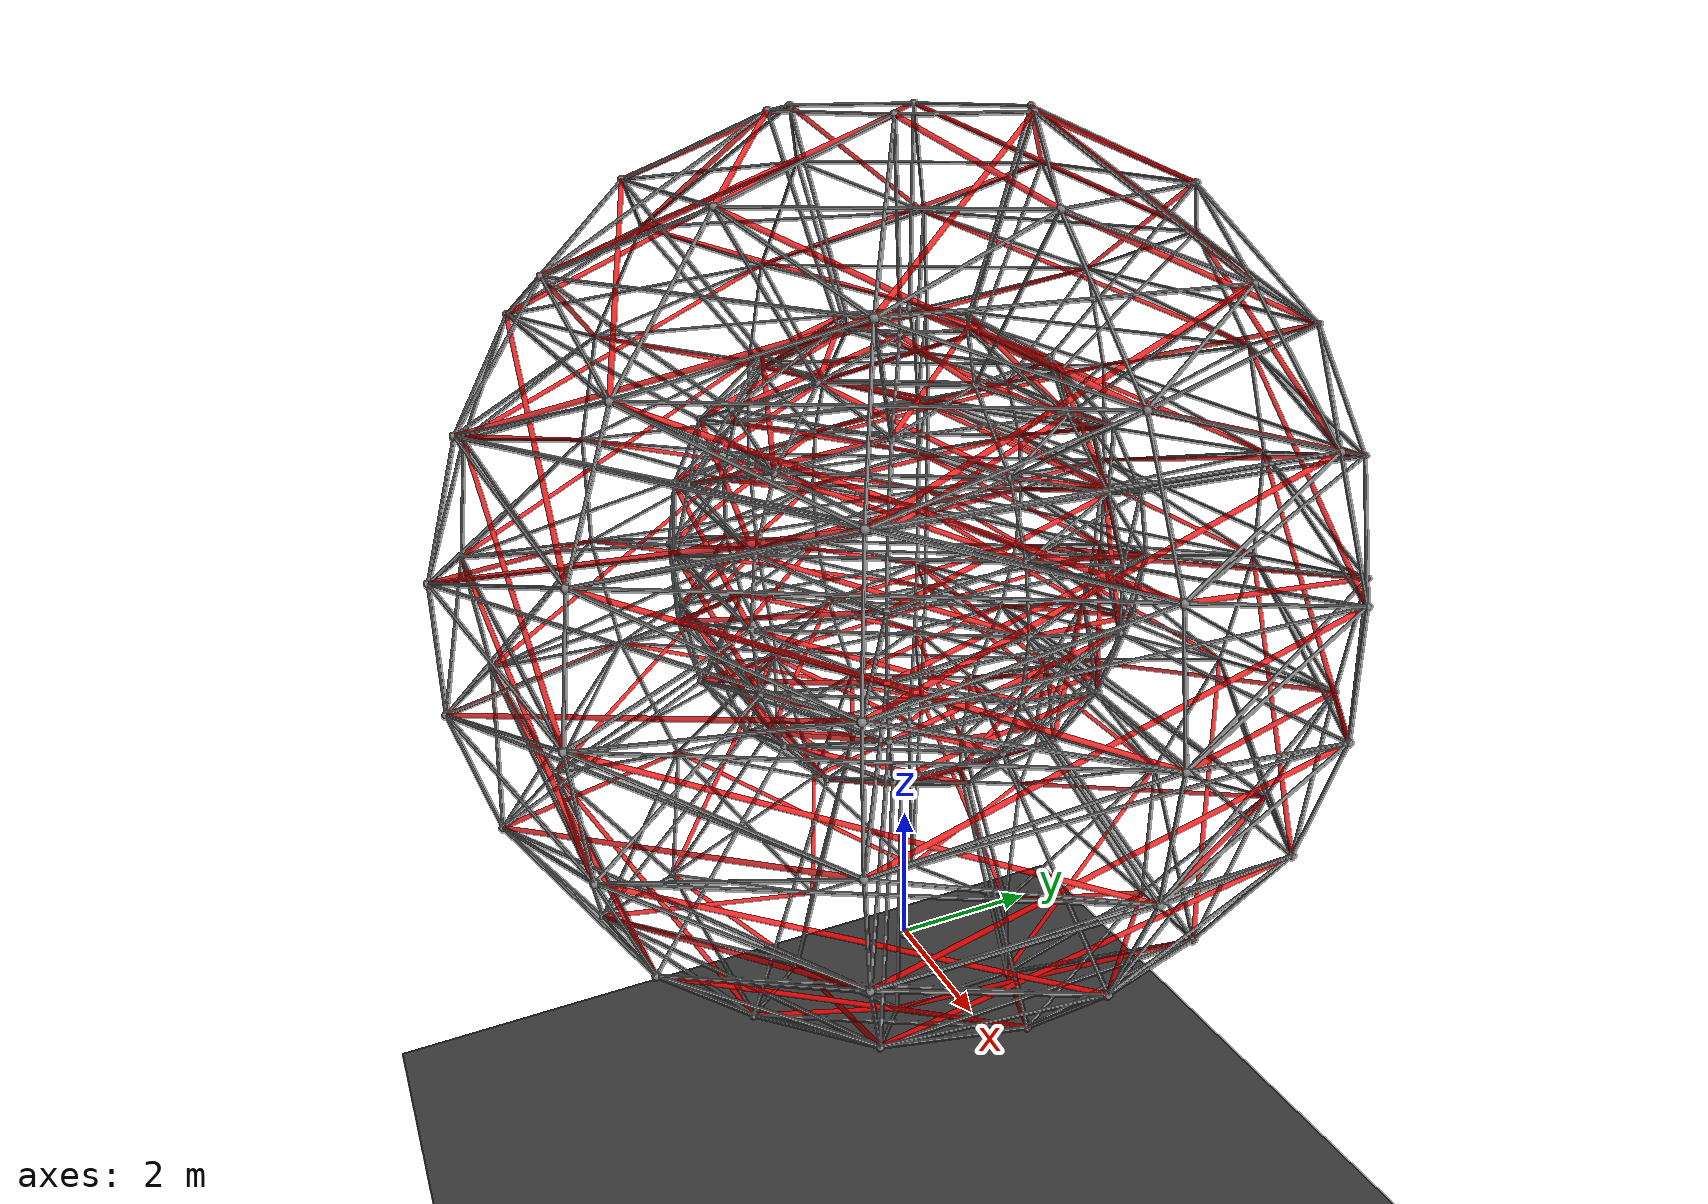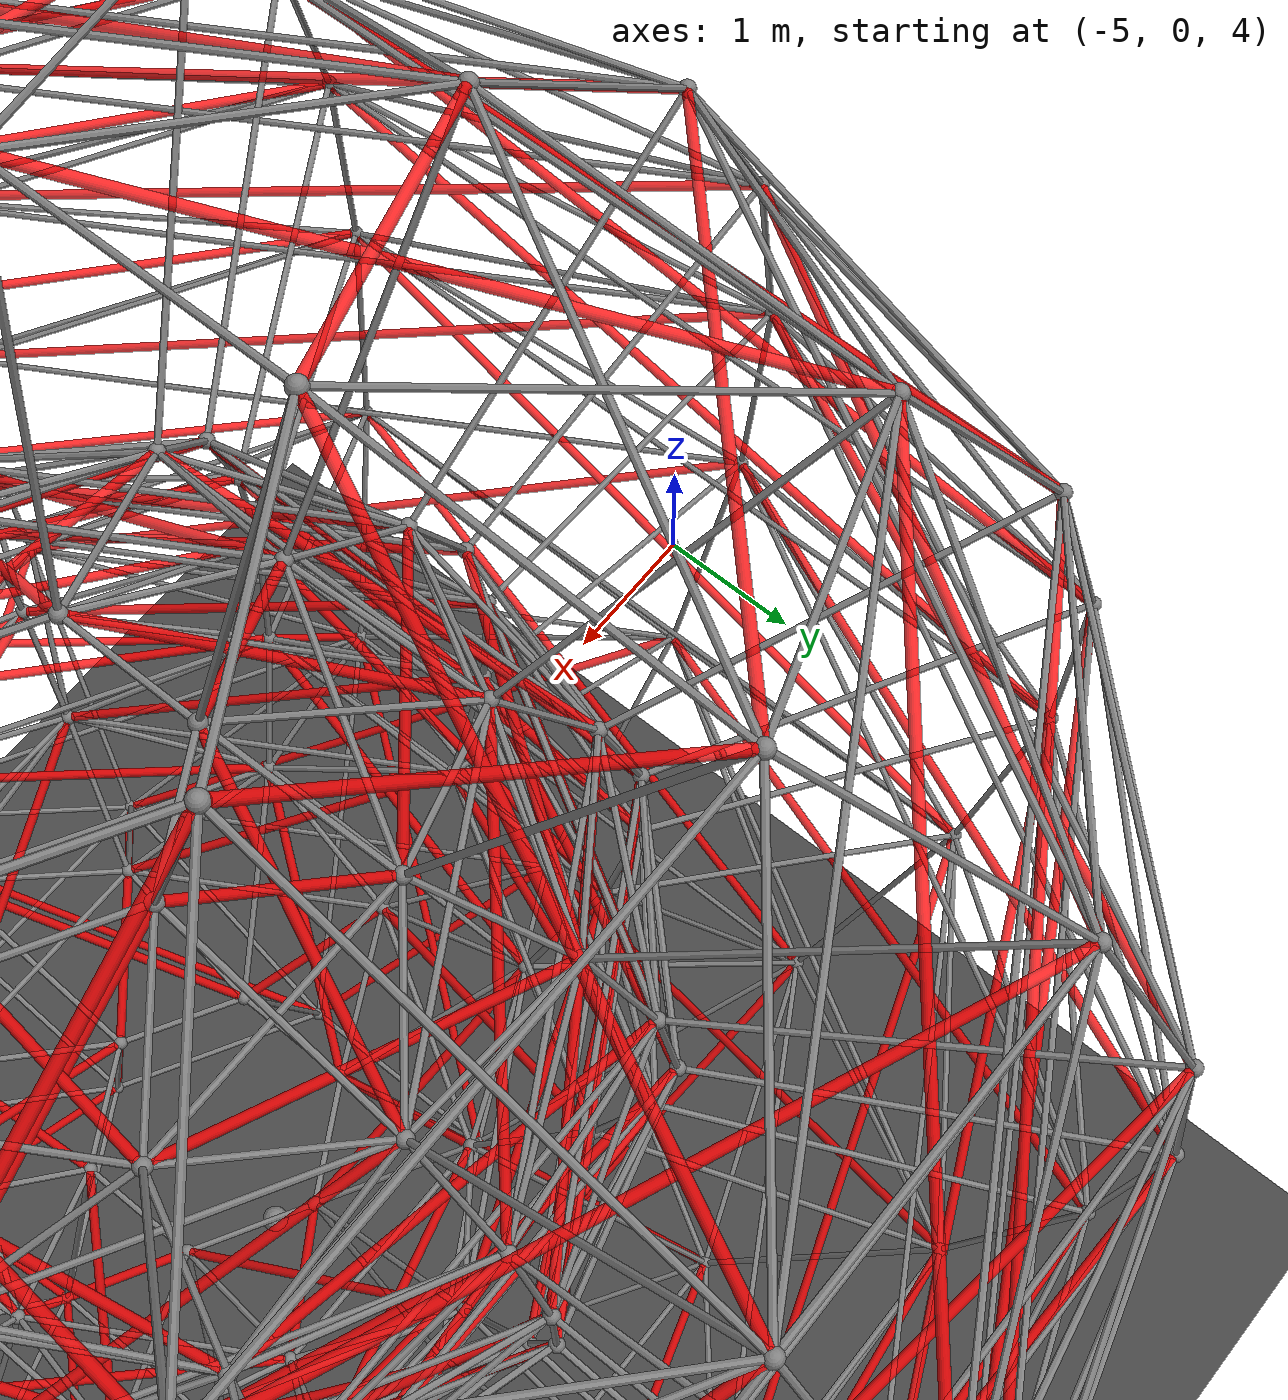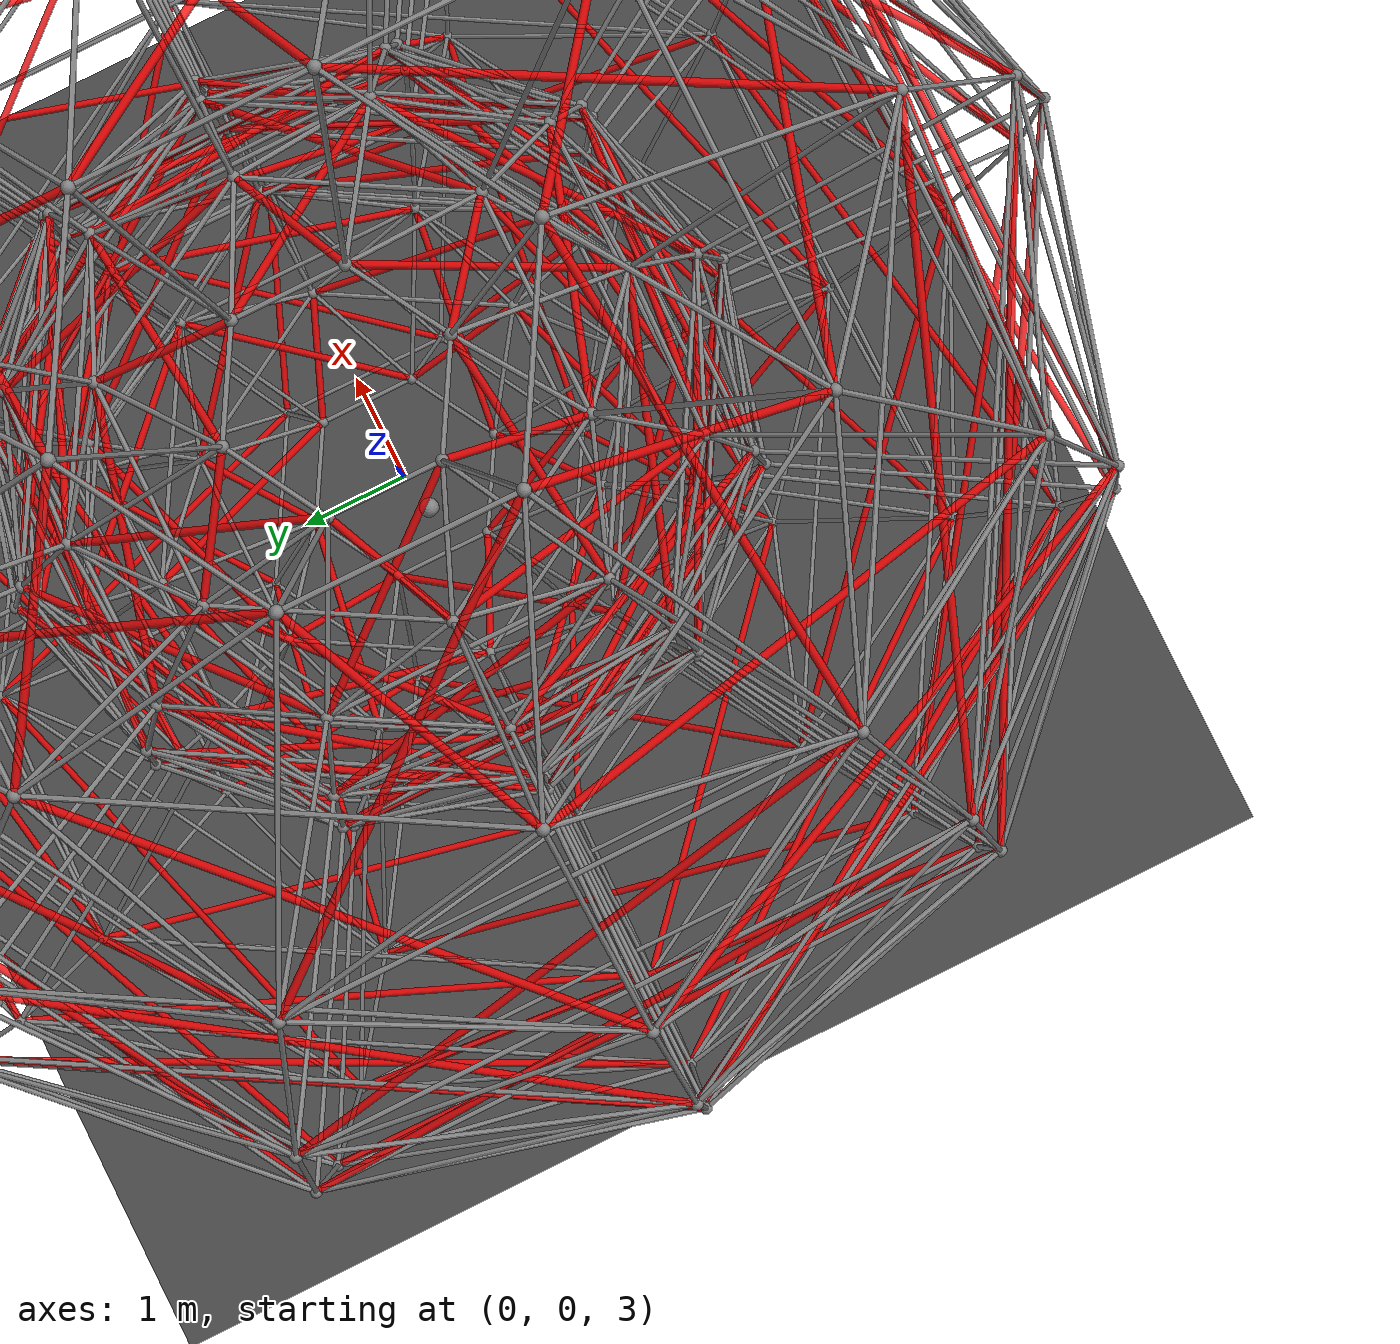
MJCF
<mujoco model="dbar">
    <option timestep="0.01" integrator="RK4" gravity = "0 0 -9" collision="dynamic" density="1"/>

    <default>
        <geom size="0.03"/>
        <site size="0.05"/>
    </default>
    <size njmax="1000"/>

    <asset>
        <texture type="skybox" builtin="gradient" rgb1="0.6 0.6 0.6" rgb2="0 0 0" width="512" height="512"/>

        <texture name="texplane" type="2d" builtin="checker" rgb1=".25 .25 .25" rgb2=".3 .3 .3" width="512" height="512" mark="cross" markrgb=".8 .8 .8"/>

        <material name="matplane" reflectance="0.3" texture="texplane" texrepeat="1 1" texuniform="true"/>
    </asset>
<worldbody>
<light directional="true" diffuse=".8 .8 .8" specular=".2 .2 .2" pos="0 0 5" dir="0 0 -1">
</light>
<body name="floor" pos="0 0 0">
<geom name="floor" pos="0 0 -5" size="0 0 1" type="plane" material="matplane">
</geom>
<site name="s0" pos="0 0 0" size="0.1">
</site>
</body>
<body name="body0" pos="1.4842928 0.8569568 0.       ">
<joint type="free" pos="0 0 0">
</joint>
<geom name="body0" type="capsule" fromto="0 0 0 -1.4842927  3.5169862  1.6428571" rgba="1 0 0 .8">
</geom>
<site name="site0" pos="0 0 0">
</site>
<site name="site1" pos="-1.4842927  3.5169862  1.6428571">
</site>
</body>
<body name="body1" pos="1.7109343 2.963425  0.8214286">
<joint type="free" pos="0 0 0">
</joint>
<geom name="body1" type="capsule" fromto="0 0 0  3.3094324 -2.9634255  1.6428571" rgba="1 0 0 .8">
</geom>
<site name="site2" pos="0 0 0">
</site>
<site name="site3" pos=" 3.3094324 -2.9634255  1.6428571">
</site>
</body>
<body name="body2" pos="1.4842928 0.8569568 0.       ">
<joint type="free" pos="0 0 0">
</joint>
<geom name="body2" type="capsule" fromto="0 0 0  1.9375756 -0.8569572  0.8214286" rgba="1 0 0 .8">
</geom>
<site name="site4" pos=" 1.9375756 -0.8569572  0.8214286">
</site>
</body>
<body name="body3" pos="0.        1.7139137 0.       ">
<joint type="free" pos="0 0 0">
</joint>
<geom name="body3" type="capsule" fromto="0 0 0 -3.7879457  0.473058   1.6428571" rgba="1 0 0 .8">
</geom>
<site name="site5" pos="0 0 0">
</site>
<site name="site6" pos="-3.7879457  0.473058   1.6428571">
</site>
</body>
<body name="body4" pos="-1.7109341  2.9634251  0.8214286">
<joint type="free" pos="0 0 0">
</joint>
<geom name="body4" type="capsule" fromto="0 0 0 4.2211175 1.3843399 1.6428571" rgba="1 0 0 .8">
</geom>
<site name="site7" pos="0 0 0">
</site>
<site name="site8" pos="4.2211175 1.3843399 1.6428571">
</site>
</body>
<body name="body5" pos="0.        1.7139137 0.       ">
<joint type="free" pos="0 0 0">
</joint>
<geom name="body5" type="capsule" fromto="0 0 0 1.7109343 1.2495113 0.8214286" rgba="1 0 0 .8">
</geom>
</body>
<body name="body6" pos="-1.4842927  0.8569569  0.       ">
<joint type="free" pos="0 0 0">
</joint>
<geom name="body6" type="capsule" fromto="0 0 0 -2.3036532 -3.0439282  1.6428571" rgba="1 0 0 .8">
</geom>
<site name="site9" pos="0 0 0">
</site>
<site name="site10" pos="-2.3036532 -3.0439282  1.6428571">
</site>
</body>
<body name="body7" pos="-3.4218684e+00  2.0000000e-07  8.2142860e-01">
<joint type="free" pos="0 0 0">
</joint>
<geom name="body7" type="capsule" fromto="0 0 0 0.9116852 4.347765  1.6428571" rgba="1 0 0 .8">
</geom>
<site name="site11" pos="0 0 0">
</site>
<site name="site12" pos="0.9116852 4.347765  1.6428571">
</site>
</body>
<body name="body8" pos="-1.4842927  0.8569569  0.       ">
<joint type="free" pos="0 0 0">
</joint>
<geom name="body8" type="capsule" fromto="0 0 0 -0.2266414  2.1064682  0.8214286" rgba="1 0 0 .8">
</geom>
</body>
<body name="body9" pos="-1.4842928 -0.8569567  0.       ">
<joint type="free" pos="0 0 0">
</joint>
<geom name="body9" type="capsule" fromto="0 0 0  1.4842924 -3.5169863  1.6428571" rgba="1 0 0 .8">
</geom>
<site name="site13" pos="0 0 0">
</site>
<site name="site14" pos=" 1.4842924 -3.5169863  1.6428571">
</site>
</body>
<body name="body10" pos="-1.7109344 -2.9634249  0.8214286">
<joint type="free" pos="0 0 0">
</joint>
<geom name="body10" type="capsule" fromto="0 0 0 -3.3094323  2.9634252  1.6428571" rgba="1 0 0 .8">
</geom>
<site name="site15" pos="0 0 0">
</site>
<site name="site16" pos="-3.3094323  2.9634252  1.6428571">
</site>
</body>
<body name="body11" pos="-1.4842928 -0.8569567  0.       ">
<joint type="free" pos="0 0 0">
</joint>
<geom name="body11" type="capsule" fromto="0 0 0 -1.9375756  0.8569569  0.8214286" rgba="1 0 0 .8">
</geom>
</body>
<body name="body12" pos="-1.0000000e-07 -1.7139137e+00  0.0000000e+00">
<joint type="free" pos="0 0 0">
</joint>
<geom name="body12" type="capsule" fromto="0 0 0  3.7879457 -0.4730582  1.6428571" rgba="1 0 0 .8">
</geom>
<site name="site17" pos="0 0 0">
</site>
<site name="site18" pos=" 3.7879457 -0.4730582  1.6428571">
</site>
</body>
<body name="body13" pos=" 1.710934  -2.9634252  0.8214286">
<joint type="free" pos="0 0 0">
</joint>
<geom name="body13" type="capsule" fromto="0 0 0 -4.2211177 -1.3843397  1.6428571" rgba="1 0 0 .8">
</geom>
<site name="site19" pos="0 0 0">
</site>
<site name="site20" pos="-4.2211177 -1.3843397  1.6428571">
</site>
</body>
<body name="body14" pos="-1.0000000e-07 -1.7139137e+00  0.0000000e+00">
<joint type="free" pos="0 0 0">
</joint>
<geom name="body14" type="capsule" fromto="0 0 0 -1.7109343 -1.2495112  0.8214286" rgba="1 0 0 .8">
</geom>
</body>
<body name="body15" pos=" 1.4842927 -0.856957   0.       ">
<joint type="free" pos="0 0 0">
</joint>
<geom name="body15" type="capsule" fromto="0 0 0 2.3036531 3.0439285 1.6428571" rgba="1 0 0 .8">
</geom>
<site name="site21" pos="0 0 0">
</site>
<site name="site22" pos="2.3036531 3.0439285 1.6428571">
</site>
</body>
<body name="body16" pos=" 3.4218684e+00 -4.0000000e-07  8.2142860e-01">
<joint type="free" pos="0 0 0">
</joint>
<geom name="body16" type="capsule" fromto="0 0 0 -0.9116854 -4.3477649  1.6428571" rgba="1 0 0 .8">
</geom>
<site name="site23" pos="-0.9116854 -4.3477649  1.6428571">
</site>
</body>
<body name="body17" pos=" 1.4842927 -0.856957   0.       ">
<joint type="free" pos="0 0 0">
</joint>
<geom name="body17" type="capsule" fromto="0 0 0  0.2266413 -2.1064682  0.8214286" rgba="1 0 0 .8">
</geom>
</body>
<body name="body18" pos="3.7879458 2.1869715 1.6428571">
<joint type="free" pos="0 0 0">
</joint>
<geom name="body18" type="capsule" fromto="0 0 0 -3.7879457  3.2836131  1.6428572" rgba="1 0 0 .8">
</geom>
<site name="site24" pos="-3.7879457  3.2836131  1.6428572">
</site>
</body>
<body name="body19" pos="2.5101834 4.347765  2.4642857">
<joint type="free" pos="0 0 0">
</joint>
<geom name="body19" type="capsule" fromto="0 0 0  3.2605202 -4.3477656  1.6428572" rgba="1 0 0 .8">
</geom>
<site name="site25" pos=" 3.2605202 -4.3477656  1.6428572">
</site>
</body>
<body name="body20" pos="1.0000000e-07 4.3739430e+00 1.6428571e+00">
<joint type="free" pos="0 0 0">
</joint>
<geom name="body20" type="capsule" fromto="0 0 0 -4.7376652 -1.6386505  1.6428572" rgba="1 0 0 .8">
</geom>
<site name="site26" pos="-4.7376652 -1.6386505  1.6428572">
</site>
</body>
<body name="body21" pos="-2.5101832  4.3477652  2.4642857">
<joint type="free" pos="0 0 0">
</joint>
<geom name="body21" type="capsule" fromto="0 0 0 5.3955351 0.6498107 1.6428572" rgba="1 0 0 .8">
</geom>
<site name="site27" pos="5.3955351 0.6498107 1.6428572">
</site>
</body>
<body name="body22" pos="-3.7879457  2.1869717  1.6428571">
<joint type="free" pos="0 0 0">
</joint>
<geom name="body22" type="capsule" fromto="0 0 0 -0.9497197 -4.9222637  1.6428572" rgba="1 0 0 .8">
</geom>
<site name="site28" pos="-0.9497197 -4.9222637  1.6428572">
</site>
</body>
<body name="body23" pos="-5.0203667e+00  3.0000000e-07  2.4642857e+00">
<joint type="free" pos="0 0 0">
</joint>
<geom name="body23" type="capsule" fromto="0 0 0 2.1350151 4.9975757 1.6428572" rgba="1 0 0 .8">
</geom>
<site name="site29" pos="2.1350151 4.9975757 1.6428572">
</site>
</body>
<body name="body24" pos="-3.7879459 -2.1869713  1.6428571">
<joint type="free" pos="0 0 0">
</joint>
<geom name="body24" type="capsule" fromto="0 0 0  3.7879455 -3.2836133  1.6428572" rgba="1 0 0 .8">
</geom>
<site name="site30" pos=" 3.7879455 -3.2836133  1.6428572">
</site>
</body>
<body name="body25" pos="-2.5101837 -4.3477649  2.4642857">
<joint type="free" pos="0 0 0">
</joint>
<geom name="body25" type="capsule" fromto="0 0 0 -3.2605199  4.3477652  1.6428572" rgba="1 0 0 .8">
</geom>
<site name="site31" pos="-3.2605199  4.3477652  1.6428572">
</site>
</body>
<body name="body26" pos="-4.0000000e-07 -4.3739430e+00  1.6428571e+00">
<joint type="free" pos="0 0 0">
</joint>
<geom name="body26" type="capsule" fromto="0 0 0 4.7376654 1.6386502 1.6428572" rgba="1 0 0 .8">
</geom>
<site name="site32" pos="4.7376654 1.6386502 1.6428572">
</site>
</body>
<body name="body27" pos=" 2.510183  -4.3477653  2.4642857">
<joint type="free" pos="0 0 0">
</joint>
<geom name="body27" type="capsule" fromto="0 0 0 -5.3955352 -0.6498104  1.6428572" rgba="1 0 0 .8">
</geom>
<site name="site33" pos="-5.3955352 -0.6498104  1.6428572">
</site>
</body>
<body name="body28" pos=" 3.7879456 -2.1869719  1.6428571">
<joint type="free" pos="0 0 0">
</joint>
<geom name="body28" type="capsule" fromto="0 0 0 0.9497197 4.9222642 1.6428572" rgba="1 0 0 .8">
</geom>
<site name="site34" pos="0.9497197 4.9222642 1.6428572">
</site>
</body>
<body name="body29" pos=" 5.0203667e+00 -5.0000000e-07  2.4642857e+00">
<joint type="free" pos="0 0 0">
</joint>
<geom name="body29" type="capsule" fromto="0 0 0 -2.1350153 -4.9975757  1.6428572" rgba="1 0 0 .8">
</geom>
<site name="site35" pos="-2.1350153 -4.9975757  1.6428572">
</site>
</body>
<body name="body30" pos="4.7376653 2.7352923 3.2857143">
<joint type="free" pos="0 0 0">
</joint>
<geom name="body30" type="capsule" fromto="0 0 0 -4.7376651  3.208213   1.6428571" rgba="1 0 0 .8">
</geom>
<site name="site36" pos="-4.7376651  3.208213   1.6428571">
</site>
</body>
<body name="body31" pos="2.8853519 4.9975759 4.1071429">
<joint type="free" pos="0 0 0">
</joint>
<geom name="body31" type="capsule" fromto="0 0 0  3.1146481 -4.9975765  1.6428571" rgba="1 0 0 .8">
</geom>
<site name="site37" pos=" 3.1146481 -4.9975765  1.6428571">
</site>
</body>
<body name="body32" pos="1.0000000e-07 5.4705846e+00 3.2857143e+00">
<joint type="free" pos="0 0 0">
</joint>
<geom name="body32" type="capsule" fromto="0 0 0 -5.1472265 -2.4988317  1.6428571" rgba="1 0 0 .8">
</geom>
<site name="site38" pos="-5.1472265 -2.4988317  1.6428571">
</site>
</body>
<body name="body33" pos="-2.8853516  4.997576   4.1071429">
<joint type="free" pos="0 0 0">
</joint>
<geom name="body33" type="capsule" fromto="0 0 0 5.8853517 0.1985764 1.6428571" rgba="1 0 0 .8">
</geom>
<site name="site39" pos="5.8853517 0.1985764 1.6428571">
</site>
</body>
<body name="body34" pos="-4.7376651  2.7352925  3.2857143">
<joint type="free" pos="0 0 0">
</joint>
<geom name="body34" type="capsule" fromto="0 0 0 -0.4095617 -5.7070448  1.6428571" rgba="1 0 0 .8">
</geom>
<site name="site40" pos="-0.4095617 -5.7070448  1.6428571">
</site>
</body>
<body name="body35" pos="-5.7707036e+00  3.0000000e-07  4.1071429e+00">
<joint type="free" pos="0 0 0">
</joint>
<geom name="body35" type="capsule" fromto="0 0 0 2.7707038 5.1961522 1.6428571" rgba="1 0 0 .8">
</geom>
<site name="site41" pos="2.7707038 5.1961522 1.6428571">
</site>
</body>
<body name="body36" pos="-4.7376654 -2.735292   3.2857143">
<joint type="free" pos="0 0 0">
</joint>
<geom name="body36" type="capsule" fromto="0 0 0  4.7376649 -3.2082133  1.6428571" rgba="1 0 0 .8">
</geom>
<site name="site42" pos=" 4.7376649 -3.2082133  1.6428571">
</site>
</body>
<body name="body37" pos="-2.8853522 -4.9975757  4.1071429">
<joint type="free" pos="0 0 0">
</joint>
<geom name="body37" type="capsule" fromto="0 0 0 -3.1146478  4.997576   1.6428571" rgba="1 0 0 .8">
</geom>
<site name="site43" pos="-3.1146478  4.997576   1.6428571">
</site>
</body>
<body name="body38" pos="-4.0000000e-07 -5.4705846e+00  3.2857143e+00">
<joint type="free" pos="0 0 0">
</joint>
<geom name="body38" type="capsule" fromto="0 0 0 5.1472267 2.4988315 1.6428571" rgba="1 0 0 .8">
</geom>
<site name="site44" pos="5.1472267 2.4988315 1.6428571">
</site>
</body>
<body name="body39" pos=" 2.8853514 -4.9975762  4.1071429">
<joint type="free" pos="0 0 0">
</joint>
<geom name="body39" type="capsule" fromto="0 0 0 -5.8853518 -0.198576   1.6428571" rgba="1 0 0 .8">
</geom>
<site name="site45" pos="-5.8853518 -0.198576   1.6428571">
</site>
</body>
<body name="body40" pos=" 4.737665  -2.7352928  3.2857143">
<joint type="free" pos="0 0 0">
</joint>
<geom name="body40" type="capsule" fromto="0 0 0 0.4095616 5.7070454 1.6428571" rgba="1 0 0 .8">
</geom>
<site name="site46" pos="0.4095616 5.7070454 1.6428571">
</site>
</body>
<body name="body41" pos=" 5.7707036e+00 -6.0000000e-07  4.1071429e+00">
<joint type="free" pos="0 0 0">
</joint>
<geom name="body41" type="capsule" fromto="0 0 0 -2.7707041 -5.1961521  1.6428571" rgba="1 0 0 .8">
</geom>
<site name="site47" pos="-2.7707041 -5.1961521  1.6428571">
</site>
</body>
<body name="body42" pos="5.1472266 2.9717526 4.9285714">
<joint type="free" pos="0 0 0">
</joint>
<geom name="body42" type="capsule" fromto="0 0 0 -5.1472264  2.9717527  1.6428572" rgba="1 0 0 .8">
</geom>
<site name="site48" pos="-5.1472264  2.9717527  1.6428572">
</site>
</body>
<body name="body43" pos="3.0000001 5.1961524 5.75     ">
<joint type="free" pos="0 0 0">
</joint>
<geom name="body43" type="capsule" fromto="0 0 0  2.7707035 -5.196153   1.6428571" rgba="1 0 0 .8">
</geom>
<site name="site49" pos=" 2.7707035 -5.196153   1.6428571">
</site>
</body>
<body name="body44" pos="2.0000000e-07 5.9435053e+00 4.9285714e+00">
<joint type="free" pos="0 0 0">
</joint>
<geom name="body44" type="capsule" fromto="0 0 0 -5.1472266 -2.9717524  1.6428572" rgba="1 0 0 .8">
</geom>
<site name="site50" pos="-5.1472266 -2.9717524  1.6428572">
</site>
</body>
<body name="body45" pos="-2.9999998  5.1961525  5.75     ">
<joint type="free" pos="0 0 0">
</joint>
<geom name="body45" type="capsule" fromto="0 0 0  5.8853517 -0.1985766  1.6428571" rgba="1 0 0 .8">
</geom>
<site name="site51" pos=" 5.8853517 -0.1985766  1.6428571">
</site>
</body>
<body name="body46" pos="-5.1472264  2.9717529  4.9285714">
<joint type="free" pos="0 0 0">
</joint>
<geom name="body46" type="capsule" fromto="0 0 0 -4.0000000e-07 -5.9435052e+00  1.6428572e+00" rgba="1 0 0 .8">
</geom>
<site name="site52" pos="-4.0000000e-07 -5.9435052e+00  1.6428572e+00">
</site>
</body>
<body name="body47" pos="-6.00e+00  3.00e-07  5.75e+00">
<joint type="free" pos="0 0 0">
</joint>
<geom name="body47" type="capsule" fromto="0 0 0 3.1146484 4.9975757 1.6428571" rgba="1 0 0 .8">
</geom>
<site name="site53" pos="3.1146484 4.9975757 1.6428571">
</site>
</body>
<body name="body48" pos="-5.1472268 -2.9717523  4.9285714">
<joint type="free" pos="0 0 0">
</joint>
<geom name="body48" type="capsule" fromto="0 0 0  5.1472263 -2.971753   1.6428572" rgba="1 0 0 .8">
</geom>
<site name="site54" pos=" 5.1472263 -2.971753   1.6428572">
</site>
</body>
<body name="body49" pos="-3.0000004 -5.1961522  5.75     ">
<joint type="free" pos="0 0 0">
</joint>
<geom name="body49" type="capsule" fromto="0 0 0 -2.7707032  5.1961525  1.6428571" rgba="1 0 0 .8">
</geom>
<site name="site55" pos="-2.7707032  5.1961525  1.6428571">
</site>
</body>
<body name="body50" pos="-5.0000000e-07 -5.9435053e+00  4.9285714e+00">
<joint type="free" pos="0 0 0">
</joint>
<geom name="body50" type="capsule" fromto="0 0 0 5.1472268 2.9717522 1.6428572" rgba="1 0 0 .8">
</geom>
<site name="site56" pos="5.1472268 2.9717522 1.6428572">
</site>
</body>
<body name="body51" pos=" 2.9999995 -5.1961527  5.75     ">
<joint type="free" pos="0 0 0">
</joint>
<geom name="body51" type="capsule" fromto="0 0 0 -5.8853517  0.198577   1.6428571" rgba="1 0 0 .8">
</geom>
<site name="site57" pos="-5.8853517  0.198577   1.6428571">
</site>
</body>
<body name="body52" pos=" 5.1472263 -2.9717531  4.9285714">
<joint type="free" pos="0 0 0">
</joint>
<geom name="body52" type="capsule" fromto="0 0 0 3.0000000e-07 5.9435057e+00 1.6428572e+00" rgba="1 0 0 .8">
</geom>
<site name="site58" pos="3.0000000e-07 5.9435057e+00 1.6428572e+00">
</site>
</body>
<body name="body53" pos=" 6.00e+00 -6.00e-07  5.75e+00">
<joint type="free" pos="0 0 0">
</joint>
<geom name="body53" type="capsule" fromto="0 0 0 -3.1146486 -4.9975756  1.6428571" rgba="1 0 0 .8">
</geom>
<site name="site59" pos="-3.1146486 -4.9975756  1.6428571">
</site>
</body>
<body name="body54" pos="5.1472266 2.9717526 6.5714286">
<joint type="free" pos="0 0 0">
</joint>
<geom name="body54" type="capsule" fromto="0 0 0 -5.1472265  2.498832   1.6428571" rgba="1 0 0 .8">
</geom>
<site name="site60" pos="-5.1472265  2.498832   1.6428571">
</site>
</body>
<body name="body55" pos="2.8853519 4.9975759 7.3928571">
<joint type="free" pos="0 0 0">
</joint>
<geom name="body55" type="capsule" fromto="0 0 0  2.1350148 -4.9975764  1.6428572" rgba="1 0 0 .8">
</geom>
<site name="site61" pos=" 2.1350148 -4.9975764  1.6428572">
</site>
</body>
<body name="body56" pos="2.0000000e-07 5.9435053e+00 6.5714286e+00">
<joint type="free" pos="0 0 0">
</joint>
<geom name="body56" type="capsule" fromto="0 0 0 -4.7376653 -3.2082128  1.6428571" rgba="1 0 0 .8">
</geom>
<site name="site62" pos="-4.7376653 -3.2082128  1.6428571">
</site>
</body>
<body name="body57" pos="-2.8853516  4.997576   7.3928571">
<joint type="free" pos="0 0 0">
</joint>
<geom name="body57" type="capsule" fromto="0 0 0  5.395535  -0.649811   1.6428572" rgba="1 0 0 .8">
</geom>
<site name="site63" pos=" 5.395535  -0.649811   1.6428572">
</site>
</body>
<body name="body58" pos="-5.1472264  2.9717529  6.5714286">
<joint type="free" pos="0 0 0">
</joint>
<geom name="body58" type="capsule" fromto="0 0 0  0.409561  -5.7070449  1.6428571" rgba="1 0 0 .8">
</geom>
<site name="site64" pos=" 0.409561  -5.7070449  1.6428571">
</site>
</body>
<body name="body59" pos="-5.7707036e+00  3.0000000e-07  7.3928571e+00">
<joint type="free" pos="0 0 0">
</joint>
<geom name="body59" type="capsule" fromto="0 0 0 3.2605204 4.3477649 1.6428572" rgba="1 0 0 .8">
</geom>
<site name="site65" pos="3.2605204 4.3477649 1.6428572">
</site>
</body>
<body name="body60" pos="-5.1472268 -2.9717523  6.5714286">
<joint type="free" pos="0 0 0">
</joint>
<geom name="body60" type="capsule" fromto="0 0 0  5.1472264 -2.4988323  1.6428571" rgba="1 0 0 .8">
</geom>
<site name="site66" pos=" 5.1472264 -2.4988323  1.6428571">
</site>
</body>
<body name="body61" pos="-2.8853522 -4.9975757  7.3928571">
<joint type="free" pos="0 0 0">
</joint>
<geom name="body61" type="capsule" fromto="0 0 0 -2.1350145  4.997576   1.6428572" rgba="1 0 0 .8">
</geom>
<site name="site67" pos="-2.1350145  4.997576   1.6428572">
</site>
</body>
<body name="body62" pos="-5.0000000e-07 -5.9435053e+00  6.5714286e+00">
<joint type="free" pos="0 0 0">
</joint>
<geom name="body62" type="capsule" fromto="0 0 0 4.7376655 3.2082125 1.6428571" rgba="1 0 0 .8">
</geom>
<site name="site68" pos="4.7376655 3.2082125 1.6428571">
</site>
</body>
<body name="body63" pos=" 2.8853514 -4.9975762  7.3928571">
<joint type="free" pos="0 0 0">
</joint>
<geom name="body63" type="capsule" fromto="0 0 0 -5.3955351  0.6498113  1.6428572" rgba="1 0 0 .8">
</geom>
<site name="site69" pos="-5.3955351  0.6498113  1.6428572">
</site>
</body>
<body name="body64" pos=" 5.1472263 -2.9717531  6.5714286">
<joint type="free" pos="0 0 0">
</joint>
<geom name="body64" type="capsule" fromto="0 0 0 -0.409561   5.7070454  1.6428571" rgba="1 0 0 .8">
</geom>
<site name="site70" pos="-0.409561   5.7070454  1.6428571">
</site>
</body>
<body name="body65" pos=" 5.7707036e+00 -6.0000000e-07  7.3928571e+00">
<joint type="free" pos="0 0 0">
</joint>
<geom name="body65" type="capsule" fromto="0 0 0 -3.2605206 -4.3477647  1.6428572" rgba="1 0 0 .8">
</geom>
<site name="site71" pos="-3.2605206 -4.3477647  1.6428572">
</site>
</body>
<body name="body66" pos="4.7376653 2.7352923 8.2142857">
<joint type="free" pos="0 0 0">
</joint>
<geom name="body66" type="capsule" fromto="0 0 0 -4.7376652  1.6386507  1.6428572" rgba="1 0 0 .8">
</geom>
<site name="site72" pos="-4.7376652  1.6386507  1.6428572">
</site>
</body>
<body name="body67" pos="2.5101834 4.347765  9.0357143">
<joint type="free" pos="0 0 0">
</joint>
<geom name="body67" type="capsule" fromto="0 0 0  0.911685  -4.3477654  1.6428571" rgba="1 0 0 .8">
</geom>
<site name="site73" pos=" 0.911685  -4.3477654  1.6428571">
</site>
</body>
<body name="body68" pos="1.0000000e-07 5.4705846e+00 8.2142857e+00">
<joint type="free" pos="0 0 0">
</joint>
<geom name="body68" type="capsule" fromto="0 0 0 -3.7879458 -3.2836129  1.6428572" rgba="1 0 0 .8">
</geom>
<site name="site74" pos="-3.7879458 -3.2836129  1.6428572">
</site>
</body>
<body name="body69" pos="-2.5101832  4.3477652  9.0357143">
<joint type="free" pos="0 0 0">
</joint>
<geom name="body69" type="capsule" fromto="0 0 0  4.2211175 -1.3843402  1.6428571" rgba="1 0 0 .8">
</geom>
<site name="site75" pos=" 4.2211175 -1.3843402  1.6428571">
</site>
</body>
<body name="body70" pos="-4.7376651  2.7352925  8.2142857">
<joint type="free" pos="0 0 0">
</joint>
<geom name="body70" type="capsule" fromto="0 0 0  0.9497192 -4.9222638  1.6428572" rgba="1 0 0 .8">
</geom>
<site name="site76" pos=" 0.9497192 -4.9222638  1.6428572">
</site>
</body>
<body name="body71" pos="-5.0203667e+00  3.0000000e-07  9.0357143e+00">
<joint type="free" pos="0 0 0">
</joint>
<geom name="body71" type="capsule" fromto="0 0 0 3.3094326 2.9634248 1.6428571" rgba="1 0 0 .8">
</geom>
<site name="site77" pos="3.3094326 2.9634248 1.6428571">
</site>
</body>
<body name="body72" pos="-4.7376654 -2.735292   8.2142857">
<joint type="free" pos="0 0 0">
</joint>
<geom name="body72" type="capsule" fromto="0 0 0  4.737665  -1.638651   1.6428572" rgba="1 0 0 .8">
</geom>
<site name="site78" pos=" 4.737665  -1.638651   1.6428572">
</site>
</body>
<body name="body73" pos="-2.5101837 -4.3477649  9.0357143">
<joint type="free" pos="0 0 0">
</joint>
<geom name="body73" type="capsule" fromto="0 0 0 -0.9116847  4.3477651  1.6428571" rgba="1 0 0 .8">
</geom>
<site name="site79" pos="-0.9116847  4.3477651  1.6428571">
</site>
</body>
<body name="body74" pos="-4.0000000e-07 -5.4705846e+00  8.2142857e+00">
<joint type="free" pos="0 0 0">
</joint>
<geom name="body74" type="capsule" fromto="0 0 0 3.787946  3.2836127 1.6428572" rgba="1 0 0 .8">
</geom>
<site name="site80" pos="3.787946  3.2836127 1.6428572">
</site>
</body>
<body name="body75" pos=" 2.510183  -4.3477653  9.0357143">
<joint type="free" pos="0 0 0">
</joint>
<geom name="body75" type="capsule" fromto="0 0 0 -4.2211174  1.3843404  1.6428571" rgba="1 0 0 .8">
</geom>
<site name="site81" pos="-4.2211174  1.3843404  1.6428571">
</site>
</body>
<body name="body76" pos=" 4.737665  -2.7352928  8.2142857">
<joint type="free" pos="0 0 0">
</joint>
<geom name="body76" type="capsule" fromto="0 0 0 -0.9497192  4.9222643  1.6428572" rgba="1 0 0 .8">
</geom>
<site name="site82" pos="-0.9497192  4.9222643  1.6428572">
</site>
</body>
<body name="body77" pos=" 5.0203667e+00 -5.0000000e-07  9.0357143e+00">
<joint type="free" pos="0 0 0">
</joint>
<geom name="body77" type="capsule" fromto="0 0 0 -3.3094327 -2.9634247  1.6428571" rgba="1 0 0 .8">
</geom>
<site name="site83" pos="-3.3094327 -2.9634247  1.6428571">
</site>
</body>
<body name="body78" pos="3.7879458 2.1869715 9.8571429">
<joint type="free" pos="0 0 0">
</joint>
<geom name="body78" type="capsule" fromto="0 0 0 -3.7879458 -0.4730578  1.6428571" rgba="1 0 0 .8">
</geom>
<site name="site84" pos="-3.7879458 -0.4730578  1.6428571">
</site>
</body>
<body name="body79" pos=" 1.7109343  2.963425  10.6785714">
<joint type="free" pos="0 0 0">
</joint>
<geom name="body79" type="capsule" fromto="0 0 0 -0.2266415 -2.1064682  0.8214286" rgba="1 0 0 .8">
</geom>
<site name="site85" pos="-0.2266415 -2.1064682  0.8214286">
</site>
</body>
<body name="body80" pos="1.0000000e-07 4.3739430e+00 9.8571429e+00">
<joint type="free" pos="0 0 0">
</joint>
<geom name="body80" type="capsule" fromto="0 0 0 -1.4842928 -3.5169861  1.6428571" rgba="1 0 0 .8">
</geom>
<site name="site86" pos="-1.4842928 -3.5169861  1.6428571">
</site>
</body>
<body name="body81" pos="-1.7109341  2.9634251 10.6785714">
<joint type="free" pos="0 0 0">
</joint>
<geom name="body81" type="capsule" fromto="0 0 0  1.7109341 -1.2495114  0.8214286" rgba="1 0 0 .8">
</geom>
</body>
<body name="body82" pos="-3.7879457  2.1869717  9.8571429">
<joint type="free" pos="0 0 0">
</joint>
<geom name="body82" type="capsule" fromto="0 0 0  2.3036529 -3.0439284  1.6428571" rgba="1 0 0 .8">
</geom>
<site name="site87" pos=" 2.3036529 -3.0439284  1.6428571">
</site>
</body>
<body name="body83" pos="-3.42186840e+00  2.00000000e-07  1.06785714e+01">
<joint type="free" pos="0 0 0">
</joint>
<geom name="body83" type="capsule" fromto="0 0 0 1.9375757 0.8569567 0.8214286" rgba="1 0 0 .8">
</geom>
</body>
<body name="body84" pos="-3.7879459 -2.1869713  9.8571429">
<joint type="free" pos="0 0 0">
</joint>
<geom name="body84" type="capsule" fromto="0 0 0 3.7879458 0.4730576 1.6428571" rgba="1 0 0 .8">
</geom>
<site name="site88" pos="3.7879458 0.4730576 1.6428571">
</site>
</body>
<body name="body85" pos="-1.7109344 -2.9634249 10.6785714">
<joint type="free" pos="0 0 0">
</joint>
<geom name="body85" type="capsule" fromto="0 0 0 0.2266416 2.1064682 0.8214286" rgba="1 0 0 .8">
</geom>
</body>
<body name="body86" pos="-4.0000000e-07 -4.3739430e+00  9.8571429e+00">
<joint type="free" pos="0 0 0">
</joint>
<geom name="body86" type="capsule" fromto="0 0 0 1.4842931 3.516986  1.6428571" rgba="1 0 0 .8">
</geom>
<site name="site89" pos="1.4842931 3.516986  1.6428571">
</site>
</body>
<body name="body87" pos=" 1.710934  -2.9634252 10.6785714">
<joint type="free" pos="0 0 0">
</joint>
<geom name="body87" type="capsule" fromto="0 0 0 -1.7109341  1.2495115  0.8214286" rgba="1 0 0 .8">
</geom>
</body>
<body name="body88" pos=" 3.7879456 -2.1869719  9.8571429">
<joint type="free" pos="0 0 0">
</joint>
<geom name="body88" type="capsule" fromto="0 0 0 -2.3036528  3.0439287  1.6428571" rgba="1 0 0 .8">
</geom>
</body>
<body name="body89" pos=" 3.42186840e+00 -4.00000000e-07  1.06785714e+01">
<joint type="free" pos="0 0 0">
</joint>
<geom name="body89" type="capsule" fromto="0 0 0 -1.9375757 -0.8569566  0.8214286" rgba="1 0 0 .8">
</geom>
</body>
<body name="body90" pos="0.7774867 0.4488821 2.9880952">
<joint type="free" pos="0 0 0">
</joint>
<geom name="body90" type="capsule" fromto="0 0 0 -0.7774866  1.8422309  0.8605443" rgba="1 0 0 .8">
</geom>
<site name="site90" pos="0 0 0">
</site>
<site name="site91" pos="-0.7774866  1.8422309  0.8605443">
</site>
</body>
<body name="body91" pos="0.8962037 1.5522702 3.4183673">
<joint type="free" pos="0 0 0">
</joint>
<geom name="body91" type="capsule" fromto="0 0 0  1.7335122 -1.5522705  0.8605443" rgba="1 0 0 .8">
</geom>
<site name="site92" pos="0 0 0">
</site>
<site name="site93" pos=" 1.7335122 -1.5522705  0.8605443">
</site>
</body>
<body name="body92" pos="0.7774867 0.4488821 2.9880952">
<joint type="free" pos="0 0 0">
</joint>
<geom name="body92" type="capsule" fromto="0 0 0  1.0149206 -0.4488823  0.4302721" rgba="1 0 0 .8">
</geom>
<site name="site94" pos=" 1.0149206 -0.4488823  0.4302721">
</site>
</body>
<body name="body93" pos="0.        0.8977643 2.9880952">
<joint type="free" pos="0 0 0">
</joint>
<geom name="body93" type="capsule" fromto="0 0 0 -1.984162   0.2477923  0.8605443" rgba="1 0 0 .8">
</geom>
<site name="site95" pos="0 0 0">
</site>
<site name="site96" pos="-1.984162   0.2477923  0.8605443">
</site>
</body>
<body name="body94" pos="-0.8962036  1.5522703  3.4183673">
<joint type="free" pos="0 0 0">
</joint>
<geom name="body94" type="capsule" fromto="0 0 0 2.2110616 0.7251304 0.8605443" rgba="1 0 0 .8">
</geom>
<site name="site97" pos="0 0 0">
</site>
<site name="site98" pos="2.2110616 0.7251304 0.8605443">
</site>
</body>
<body name="body95" pos="0.        0.8977643 2.9880952">
<joint type="free" pos="0 0 0">
</joint>
<geom name="body95" type="capsule" fromto="0 0 0 0.8962037 0.6545059 0.4302721" rgba="1 0 0 .8">
</geom>
</body>
<body name="body96" pos="-0.7774867  0.4488822  2.9880952">
<joint type="free" pos="0 0 0">
</joint>
<geom name="body96" type="capsule" fromto="0 0 0 -1.2066754 -1.5944386  0.8605443" rgba="1 0 0 .8">
</geom>
<site name="site99" pos="0 0 0">
</site>
<site name="site100" pos="-1.2066754 -1.5944386  0.8605443">
</site>
</body>
<body name="body97" pos="-1.7924073e+00  1.0000000e-07  3.4183673e+00">
<joint type="free" pos="0 0 0">
</joint>
<geom name="body97" type="capsule" fromto="0 0 0 0.4775494 2.2774007 0.8605443" rgba="1 0 0 .8">
</geom>
<site name="site101" pos="0 0 0">
</site>
<site name="site102" pos="0.4775494 2.2774007 0.8605443">
</site>
</body>
<body name="body98" pos="-0.7774867  0.4488822  2.9880952">
<joint type="free" pos="0 0 0">
</joint>
<geom name="body98" type="capsule" fromto="0 0 0 -0.1187169  1.1033881  0.4302721" rgba="1 0 0 .8">
</geom>
</body>
<body name="body99" pos="-0.7774867 -0.4488821  2.9880952">
<joint type="free" pos="0 0 0">
</joint>
<geom name="body99" type="capsule" fromto="0 0 0  0.7774865 -1.8422309  0.8605443" rgba="1 0 0 .8">
</geom>
<site name="site103" pos="0 0 0">
</site>
<site name="site104" pos=" 0.7774865 -1.8422309  0.8605443">
</site>
</body>
<body name="body100" pos="-0.8962038 -1.5522702  3.4183673">
<joint type="free" pos="0 0 0">
</joint>
<geom name="body100" type="capsule" fromto="0 0 0 -1.7335121  1.5522703  0.8605443" rgba="1 0 0 .8">
</geom>
<site name="site105" pos="0 0 0">
</site>
<site name="site106" pos="-1.7335121  1.5522703  0.8605443">
</site>
</body>
<body name="body101" pos="-0.7774867 -0.4488821  2.9880952">
<joint type="free" pos="0 0 0">
</joint>
<geom name="body101" type="capsule" fromto="0 0 0 -1.0149206  0.4488822  0.4302721" rgba="1 0 0 .8">
</geom>
</body>
<body name="body102" pos="-1.0000000e-07 -8.9776430e-01  2.9880952e+00">
<joint type="free" pos="0 0 0">
</joint>
<geom name="body102" type="capsule" fromto="0 0 0  1.9841621 -0.2477924  0.8605443" rgba="1 0 0 .8">
</geom>
<site name="site107" pos="0 0 0">
</site>
<site name="site108" pos=" 1.9841621 -0.2477924  0.8605443">
</site>
</body>
<body name="body103" pos=" 0.8962035 -1.5522703  3.4183673">
<joint type="free" pos="0 0 0">
</joint>
<geom name="body103" type="capsule" fromto="0 0 0 -2.2110616 -0.7251304  0.8605443" rgba="1 0 0 .8">
</geom>
<site name="site109" pos="0 0 0">
</site>
<site name="site110" pos="-2.2110616 -0.7251304  0.8605443">
</site>
</body>
<body name="body104" pos="-1.0000000e-07 -8.9776430e-01  2.9880952e+00">
<joint type="free" pos="0 0 0">
</joint>
<geom name="body104" type="capsule" fromto="0 0 0 -0.8962037 -0.6545059  0.4302721" rgba="1 0 0 .8">
</geom>
</body>
<body name="body105" pos=" 0.7774866 -0.4488822  2.9880952">
<joint type="free" pos="0 0 0">
</joint>
<geom name="body105" type="capsule" fromto="0 0 0 1.2066755 1.5944387 0.8605443" rgba="1 0 0 .8">
</geom>
<site name="site111" pos="0 0 0">
</site>
<site name="site112" pos="1.2066755 1.5944387 0.8605443">
</site>
</body>
<body name="body106" pos=" 1.7924073e+00 -2.0000000e-07  3.4183673e+00">
<joint type="free" pos="0 0 0">
</joint>
<geom name="body106" type="capsule" fromto="0 0 0 -0.4775496 -2.2774007  0.8605443" rgba="1 0 0 .8">
</geom>
<site name="site113" pos="-0.4775496 -2.2774007  0.8605443">
</site>
</body>
<body name="body107" pos=" 0.7774866 -0.4488822  2.9880952">
<joint type="free" pos="0 0 0">
</joint>
<geom name="body107" type="capsule" fromto="0 0 0  0.1187169 -1.1033881  0.4302721" rgba="1 0 0 .8">
</geom>
</body>
<body name="body108" pos="1.9841621 1.1455565 3.8486395">
<joint type="free" pos="0 0 0">
</joint>
<geom name="body108" type="capsule" fromto="0 0 0 -1.984162   1.7199878  0.8605442" rgba="1 0 0 .8">
</geom>
<site name="site114" pos="-1.984162   1.7199878  0.8605442">
</site>
</body>
<body name="body109" pos="1.314858  2.2774007 4.2789116">
<joint type="free" pos="0 0 0">
</joint>
<geom name="body109" type="capsule" fromto="0 0 0  1.7078915 -2.277401   0.8605442" rgba="1 0 0 .8">
</geom>
<site name="site115" pos=" 1.7078915 -2.277401   0.8605442">
</site>
</body>
<body name="body110" pos="1.0000000e-07 2.2911130e+00 3.8486395e+00">
<joint type="free" pos="0 0 0">
</joint>
<geom name="body110" type="capsule" fromto="0 0 0 -2.4816342 -0.8583407  0.8605442" rgba="1 0 0 .8">
</geom>
<site name="site116" pos="-2.4816342 -0.8583407  0.8605442">
</site>
</body>
<body name="body111" pos="-1.3148579  2.2774008  4.2789116">
<joint type="free" pos="0 0 0">
</joint>
<geom name="body111" type="capsule" fromto="0 0 0 2.8262327 0.340377  0.8605442" rgba="1 0 0 .8">
</geom>
<site name="site117" pos="2.8262327 0.340377  0.8605442">
</site>
</body>
<body name="body112" pos="-1.984162   1.1455566  3.8486395">
<joint type="free" pos="0 0 0">
</joint>
<geom name="body112" type="capsule" fromto="0 0 0 -0.4974723 -2.5783286  0.8605442" rgba="1 0 0 .8">
</geom>
<site name="site118" pos="-0.4974723 -2.5783286  0.8605442">
</site>
</body>
<body name="body113" pos="-2.6297159e+00  1.0000000e-07  4.2789116e+00">
<joint type="free" pos="0 0 0">
</joint>
<geom name="body113" type="capsule" fromto="0 0 0 1.1183412 2.6177778 0.8605442" rgba="1 0 0 .8">
</geom>
<site name="site119" pos="1.1183412 2.6177778 0.8605442">
</site>
</body>
<body name="body114" pos="-1.9841621 -1.1455564  3.8486395">
<joint type="free" pos="0 0 0">
</joint>
<geom name="body114" type="capsule" fromto="0 0 0  1.9841619 -1.7199879  0.8605442" rgba="1 0 0 .8">
</geom>
<site name="site120" pos=" 1.9841619 -1.7199879  0.8605442">
</site>
</body>
<body name="body115" pos="-1.3148581 -2.2774007  4.2789116">
<joint type="free" pos="0 0 0">
</joint>
<geom name="body115" type="capsule" fromto="0 0 0 -1.7078914  2.2774009  0.8605442" rgba="1 0 0 .8">
</geom>
<site name="site121" pos="-1.7078914  2.2774009  0.8605442">
</site>
</body>
<body name="body116" pos="-2.0000000e-07 -2.2911130e+00  3.8486395e+00">
<joint type="free" pos="0 0 0">
</joint>
<geom name="body116" type="capsule" fromto="0 0 0 2.4816342 0.8583406 0.8605442" rgba="1 0 0 .8">
</geom>
<site name="site122" pos="2.4816342 0.8583406 0.8605442">
</site>
</body>
<body name="body117" pos=" 1.3148577 -2.2774009  4.2789116">
<joint type="free" pos="0 0 0">
</joint>
<geom name="body117" type="capsule" fromto="0 0 0 -2.8262326 -0.3403769  0.8605442" rgba="1 0 0 .8">
</geom>
<site name="site123" pos="-2.8262326 -0.3403769  0.8605442">
</site>
</body>
<body name="body118" pos=" 1.984162  -1.1455567  3.8486395">
<joint type="free" pos="0 0 0">
</joint>
<geom name="body118" type="capsule" fromto="0 0 0 0.4974722 2.5783288 0.8605442" rgba="1 0 0 .8">
</geom>
<site name="site124" pos="0.4974722 2.5783288 0.8605442">
</site>
</body>
<body name="body119" pos=" 2.6297159e+00 -3.0000000e-07  4.2789116e+00">
<joint type="free" pos="0 0 0">
</joint>
<geom name="body119" type="capsule" fromto="0 0 0 -1.1183414 -2.6177777  0.8605442" rgba="1 0 0 .8">
</geom>
<site name="site125" pos="-1.1183414 -2.6177777  0.8605442">
</site>
</body>
<body name="body120" pos="2.4816342 1.4327721 4.7091837">
<joint type="free" pos="0 0 0">
</joint>
<geom name="body120" type="capsule" fromto="0 0 0 -2.4816341  1.6804926  0.8605442" rgba="1 0 0 .8">
</geom>
<site name="site126" pos="-2.4816341  1.6804926  0.8605442">
</site>
</body>
<body name="body121" pos="1.5113748 2.6177778 5.1394558">
<joint type="free" pos="0 0 0">
</joint>
<geom name="body121" type="capsule" fromto="0 0 0  1.6314823 -2.6177781  0.8605442" rgba="1 0 0 .8">
</geom>
<site name="site127" pos=" 1.6314823 -2.6177781  0.8605442">
</site>
</body>
<body name="body122" pos="1.0000000e-07 2.8655443e+00 4.7091837e+00">
<joint type="free" pos="0 0 0">
</joint>
<geom name="body122" type="capsule" fromto="0 0 0 -2.6961663 -1.3089118  0.8605442" rgba="1 0 0 .8">
</geom>
<site name="site128" pos="-2.6961663 -1.3089118  0.8605442">
</site>
</body>
<body name="body123" pos="-1.5113747  2.6177779  5.1394558">
<joint type="free" pos="0 0 0">
</joint>
<geom name="body123" type="capsule" fromto="0 0 0 3.0828033 0.1040162 0.8605442" rgba="1 0 0 .8">
</geom>
<site name="site129" pos="3.0828033 0.1040162 0.8605442">
</site>
</body>
<body name="body124" pos="-2.4816341  1.4327723  4.7091837">
<joint type="free" pos="0 0 0">
</joint>
<geom name="body124" type="capsule" fromto="0 0 0 -0.2145323 -2.9894045  0.8605442" rgba="1 0 0 .8">
</geom>
<site name="site130" pos="-0.2145323 -2.9894045  0.8605442">
</site>
</body>
<body name="body125" pos="-3.0227495e+00  2.0000000e-07  5.1394558e+00">
<joint type="free" pos="0 0 0">
</joint>
<geom name="body125" type="capsule" fromto="0 0 0 1.451321  2.721794  0.8605442" rgba="1 0 0 .8">
</geom>
<site name="site131" pos="1.451321  2.721794  0.8605442">
</site>
</body>
<body name="body126" pos="-2.4816343 -1.432772   4.7091837">
<joint type="free" pos="0 0 0">
</joint>
<geom name="body126" type="capsule" fromto="0 0 0  2.481634  -1.6804927  0.8605442" rgba="1 0 0 .8">
</geom>
<site name="site132" pos=" 2.481634  -1.6804927  0.8605442">
</site>
</body>
<body name="body127" pos="-1.5113749 -2.6177778  5.1394558">
<joint type="free" pos="0 0 0">
</joint>
<geom name="body127" type="capsule" fromto="0 0 0 -1.6314822  2.617778   0.8605442" rgba="1 0 0 .8">
</geom>
<site name="site133" pos="-1.6314822  2.617778   0.8605442">
</site>
</body>
<body name="body128" pos="-2.0000000e-07 -2.8655443e+00  4.7091837e+00">
<joint type="free" pos="0 0 0">
</joint>
<geom name="body128" type="capsule" fromto="0 0 0 2.6961663 1.3089117 0.8605442" rgba="1 0 0 .8">
</geom>
<site name="site134" pos="2.6961663 1.3089117 0.8605442">
</site>
</body>
<body name="body129" pos=" 1.5113745 -2.617778   5.1394558">
<joint type="free" pos="0 0 0">
</joint>
<geom name="body129" type="capsule" fromto="0 0 0 -3.0828033 -0.104016   0.8605442" rgba="1 0 0 .8">
</geom>
<site name="site135" pos="-3.0828033 -0.104016   0.8605442">
</site>
</body>
<body name="body130" pos=" 2.481634  -1.4327724  4.7091837">
<joint type="free" pos="0 0 0">
</joint>
<geom name="body130" type="capsule" fromto="0 0 0 0.2145323 2.9894047 0.8605442" rgba="1 0 0 .8">
</geom>
<site name="site136" pos="0.2145323 2.9894047 0.8605442">
</site>
</body>
<body name="body131" pos=" 3.0227495e+00 -3.0000000e-07  5.1394558e+00">
<joint type="free" pos="0 0 0">
</joint>
<geom name="body131" type="capsule" fromto="0 0 0 -1.4513212 -2.721794   0.8605442" rgba="1 0 0 .8">
</geom>
<site name="site137" pos="-1.4513212 -2.721794   0.8605442">
</site>
</body>
<body name="body132" pos="2.6961663 1.5566323 5.5697279">
<joint type="free" pos="0 0 0">
</joint>
<geom name="body132" type="capsule" fromto="0 0 0 -2.6961662  1.5566324  0.8605442" rgba="1 0 0 .8">
</geom>
<site name="site138" pos="-2.6961662  1.5566324  0.8605442">
</site>
</body>
<body name="body133" pos="1.5714286 2.7217941 6.       ">
<joint type="free" pos="0 0 0">
</joint>
<geom name="body133" type="capsule" fromto="0 0 0  1.4513209 -2.7217944  0.8605442" rgba="1 0 0 .8">
</geom>
<site name="site139" pos=" 1.4513209 -2.7217944  0.8605442">
</site>
</body>
<body name="body134" pos="1.0000000e-07 3.1132647e+00 5.5697279e+00">
<joint type="free" pos="0 0 0">
</joint>
<geom name="body134" type="capsule" fromto="0 0 0 -2.6961663 -1.5566322  0.8605442" rgba="1 0 0 .8">
</geom>
<site name="site140" pos="-2.6961663 -1.5566322  0.8605442">
</site>
</body>
<body name="body135" pos="-1.5714285  2.7217942  6.       ">
<joint type="free" pos="0 0 0">
</joint>
<geom name="body135" type="capsule" fromto="0 0 0  3.0828033 -0.1040164  0.8605442" rgba="1 0 0 .8">
</geom>
<site name="site141" pos=" 3.0828033 -0.1040164  0.8605442">
</site>
</body>
<body name="body136" pos="-2.6961662  1.5566325  5.5697279">
<joint type="free" pos="0 0 0">
</joint>
<geom name="body136" type="capsule" fromto="0 0 0 -2.0000000e-07 -3.1132647e+00  8.6054420e-01" rgba="1 0 0 .8">
</geom>
<site name="site142" pos="-2.0000000e-07 -3.1132647e+00  8.6054420e-01">
</site>
</body>
<body name="body137" pos="-3.1428571e+00  2.0000000e-07  6.0000000e+00">
<joint type="free" pos="0 0 0">
</joint>
<geom name="body137" type="capsule" fromto="0 0 0 1.6314824 2.6177777 0.8605442" rgba="1 0 0 .8">
</geom>
<site name="site143" pos="1.6314824 2.6177777 0.8605442">
</site>
</body>
<body name="body138" pos="-2.6961664 -1.5566322  5.5697279">
<joint type="free" pos="0 0 0">
</joint>
<geom name="body138" type="capsule" fromto="0 0 0  2.6961661 -1.5566325  0.8605442" rgba="1 0 0 .8">
</geom>
<site name="site144" pos=" 2.6961661 -1.5566325  0.8605442">
</site>
</body>
<body name="body139" pos="-1.5714288 -2.721794   6.       ">
<joint type="free" pos="0 0 0">
</joint>
<geom name="body139" type="capsule" fromto="0 0 0 -1.4513207  2.7217942  0.8605442" rgba="1 0 0 .8">
</geom>
<site name="site145" pos="-1.4513207  2.7217942  0.8605442">
</site>
</body>
<body name="body140" pos="-3.0000000e-07 -3.1132647e+00  5.5697279e+00">
<joint type="free" pos="0 0 0">
</joint>
<geom name="body140" type="capsule" fromto="0 0 0 2.6961664 1.5566321 0.8605442" rgba="1 0 0 .8">
</geom>
<site name="site146" pos="2.6961664 1.5566321 0.8605442">
</site>
</body>
<body name="body141" pos=" 1.5714283 -2.7217943  6.       ">
<joint type="free" pos="0 0 0">
</joint>
<geom name="body141" type="capsule" fromto="0 0 0 -3.0828032  0.1040165  0.8605442" rgba="1 0 0 .8">
</geom>
<site name="site147" pos="-3.0828032  0.1040165  0.8605442">
</site>
</body>
<body name="body142" pos=" 2.6961661 -1.5566326  5.5697279">
<joint type="free" pos="0 0 0">
</joint>
<geom name="body142" type="capsule" fromto="0 0 0 2.0000000e-07 3.1132649e+00 8.6054420e-01" rgba="1 0 0 .8">
</geom>
<site name="site148" pos="2.0000000e-07 3.1132649e+00 8.6054420e-01">
</site>
</body>
<body name="body143" pos=" 3.1428571e+00 -3.0000000e-07  6.0000000e+00">
<joint type="free" pos="0 0 0">
</joint>
<geom name="body143" type="capsule" fromto="0 0 0 -1.6314826 -2.6177777  0.8605442" rgba="1 0 0 .8">
</geom>
<site name="site149" pos="-1.6314826 -2.6177777  0.8605442">
</site>
</body>
<body name="body144" pos="2.6961663 1.5566323 6.4302721">
<joint type="free" pos="0 0 0">
</joint>
<geom name="body144" type="capsule" fromto="0 0 0 -2.6961662  1.308912   0.8605442" rgba="1 0 0 .8">
</geom>
<site name="site150" pos="-2.6961662  1.308912   0.8605442">
</site>
</body>
<body name="body145" pos="1.5113748 2.6177778 6.8605442">
<joint type="free" pos="0 0 0">
</joint>
<geom name="body145" type="capsule" fromto="0 0 0  1.1183411 -2.6177781  0.8605442" rgba="1 0 0 .8">
</geom>
<site name="site151" pos=" 1.1183411 -2.6177781  0.8605442">
</site>
</body>
<body name="body146" pos="1.0000000e-07 3.1132647e+00 6.4302721e+00">
<joint type="free" pos="0 0 0">
</joint>
<geom name="body146" type="capsule" fromto="0 0 0 -2.4816342 -1.6804924  0.8605442" rgba="1 0 0 .8">
</geom>
<site name="site152" pos="-2.4816342 -1.6804924  0.8605442">
</site>
</body>
<body name="body147" pos="-1.5113747  2.6177779  6.8605442">
<joint type="free" pos="0 0 0">
</joint>
<geom name="body147" type="capsule" fromto="0 0 0  2.8262327 -0.3403772  0.8605442" rgba="1 0 0 .8">
</geom>
<site name="site153" pos=" 2.8262327 -0.3403772  0.8605442">
</site>
</body>
<body name="body148" pos="-2.6961662  1.5566325  6.4302721">
<joint type="free" pos="0 0 0">
</joint>
<geom name="body148" type="capsule" fromto="0 0 0  0.2145319 -2.9894045  0.8605442" rgba="1 0 0 .8">
</geom>
<site name="site154" pos=" 0.2145319 -2.9894045  0.8605442">
</site>
</body>
<body name="body149" pos="-3.0227495e+00  2.0000000e-07  6.8605442e+00">
<joint type="free" pos="0 0 0">
</joint>
<geom name="body149" type="capsule" fromto="0 0 0 1.7078916 2.2774006 0.8605442" rgba="1 0 0 .8">
</geom>
<site name="site155" pos="1.7078916 2.2774006 0.8605442">
</site>
</body>
<body name="body150" pos="-2.6961664 -1.5566322  6.4302721">
<joint type="free" pos="0 0 0">
</joint>
<geom name="body150" type="capsule" fromto="0 0 0  2.6961662 -1.3089121  0.8605442" rgba="1 0 0 .8">
</geom>
<site name="site156" pos=" 2.6961662 -1.3089121  0.8605442">
</site>
</body>
<body name="body151" pos="-1.5113749 -2.6177778  6.8605442">
<joint type="free" pos="0 0 0">
</joint>
<geom name="body151" type="capsule" fromto="0 0 0 -1.118341   2.6177779  0.8605442" rgba="1 0 0 .8">
</geom>
<site name="site157" pos="-1.118341   2.6177779  0.8605442">
</site>
</body>
<body name="body152" pos="-3.0000000e-07 -3.1132647e+00  6.4302721e+00">
<joint type="free" pos="0 0 0">
</joint>
<geom name="body152" type="capsule" fromto="0 0 0 2.4816343 1.6804923 0.8605442" rgba="1 0 0 .8">
</geom>
<site name="site158" pos="2.4816343 1.6804923 0.8605442">
</site>
</body>
<body name="body153" pos=" 1.5113745 -2.617778   6.8605442">
<joint type="free" pos="0 0 0">
</joint>
<geom name="body153" type="capsule" fromto="0 0 0 -2.8262326  0.3403773  0.8605442" rgba="1 0 0 .8">
</geom>
<site name="site159" pos="-2.8262326  0.3403773  0.8605442">
</site>
</body>
<body name="body154" pos=" 2.6961661 -1.5566326  6.4302721">
<joint type="free" pos="0 0 0">
</joint>
<geom name="body154" type="capsule" fromto="0 0 0 -0.2145319  2.9894047  0.8605442" rgba="1 0 0 .8">
</geom>
<site name="site160" pos="-0.2145319  2.9894047  0.8605442">
</site>
</body>
<body name="body155" pos=" 3.0227495e+00 -3.0000000e-07  6.8605442e+00">
<joint type="free" pos="0 0 0">
</joint>
<geom name="body155" type="capsule" fromto="0 0 0 -1.7078918 -2.2774006  0.8605442" rgba="1 0 0 .8">
</geom>
<site name="site161" pos="-1.7078918 -2.2774006  0.8605442">
</site>
</body>
<body name="body156" pos="2.4816342 1.4327721 7.2908163">
<joint type="free" pos="0 0 0">
</joint>
<geom name="body156" type="capsule" fromto="0 0 0 -2.4816341  0.8583409  0.8605442" rgba="1 0 0 .8">
</geom>
<site name="site162" pos="-2.4816341  0.8583409  0.8605442">
</site>
</body>
<body name="body157" pos="1.314858  2.2774007 7.7210884">
<joint type="free" pos="0 0 0">
</joint>
<geom name="body157" type="capsule" fromto="0 0 0  0.4775493 -2.2774009  0.8605443" rgba="1 0 0 .8">
</geom>
<site name="site163" pos=" 0.4775493 -2.2774009  0.8605443">
</site>
</body>
<body name="body158" pos="1.0000000e-07 2.8655443e+00 7.2908163e+00">
<joint type="free" pos="0 0 0">
</joint>
<geom name="body158" type="capsule" fromto="0 0 0 -1.9841621 -1.7199877  0.8605442" rgba="1 0 0 .8">
</geom>
<site name="site164" pos="-1.9841621 -1.7199877  0.8605442">
</site>
</body>
<body name="body159" pos="-1.3148579  2.2774008  7.7210884">
<joint type="free" pos="0 0 0">
</joint>
<geom name="body159" type="capsule" fromto="0 0 0  2.2110616 -0.7251306  0.8605443" rgba="1 0 0 .8">
</geom>
<site name="site165" pos=" 2.2110616 -0.7251306  0.8605443">
</site>
</body>
<body name="body160" pos="-2.4816341  1.4327723  7.2908163">
<joint type="free" pos="0 0 0">
</joint>
<geom name="body160" type="capsule" fromto="0 0 0  0.497472  -2.5783287  0.8605442" rgba="1 0 0 .8">
</geom>
<site name="site166" pos=" 0.497472  -2.5783287  0.8605442">
</site>
</body>
<body name="body161" pos="-2.6297159e+00  1.0000000e-07  7.7210884e+00">
<joint type="free" pos="0 0 0">
</joint>
<geom name="body161" type="capsule" fromto="0 0 0 1.7335123 1.5522702 0.8605443" rgba="1 0 0 .8">
</geom>
<site name="site167" pos="1.7335123 1.5522702 0.8605443">
</site>
</body>
<body name="body162" pos="-2.4816343 -1.432772   7.2908163">
<joint type="free" pos="0 0 0">
</joint>
<geom name="body162" type="capsule" fromto="0 0 0  2.4816341 -0.858341   0.8605442" rgba="1 0 0 .8">
</geom>
<site name="site168" pos=" 2.4816341 -0.858341   0.8605442">
</site>
</body>
<body name="body163" pos="-1.3148581 -2.2774007  7.7210884">
<joint type="free" pos="0 0 0">
</joint>
<geom name="body163" type="capsule" fromto="0 0 0 -0.4775492  2.2774008  0.8605443" rgba="1 0 0 .8">
</geom>
<site name="site169" pos="-0.4775492  2.2774008  0.8605443">
</site>
</body>
<body name="body164" pos="-2.0000000e-07 -2.8655443e+00  7.2908163e+00">
<joint type="free" pos="0 0 0">
</joint>
<geom name="body164" type="capsule" fromto="0 0 0 1.9841622 1.7199876 0.8605442" rgba="1 0 0 .8">
</geom>
<site name="site170" pos="1.9841622 1.7199876 0.8605442">
</site>
</body>
<body name="body165" pos=" 1.3148577 -2.2774009  7.7210884">
<joint type="free" pos="0 0 0">
</joint>
<geom name="body165" type="capsule" fromto="0 0 0 -2.2110615  0.7251307  0.8605443" rgba="1 0 0 .8">
</geom>
<site name="site171" pos="-2.2110615  0.7251307  0.8605443">
</site>
</body>
<body name="body166" pos=" 2.481634  -1.4327724  7.2908163">
<joint type="free" pos="0 0 0">
</joint>
<geom name="body166" type="capsule" fromto="0 0 0 -0.4974719  2.5783289  0.8605442" rgba="1 0 0 .8">
</geom>
<site name="site172" pos="-0.4974719  2.5783289  0.8605442">
</site>
</body>
<body name="body167" pos=" 2.6297159e+00 -3.0000000e-07  7.7210884e+00">
<joint type="free" pos="0 0 0">
</joint>
<geom name="body167" type="capsule" fromto="0 0 0 -1.7335124 -1.55227    0.8605443" rgba="1 0 0 .8">
</geom>
<site name="site173" pos="-1.7335124 -1.55227    0.8605443">
</site>
</body>
<body name="body168" pos="1.9841621 1.1455565 8.1513605">
<joint type="free" pos="0 0 0">
</joint>
<geom name="body168" type="capsule" fromto="0 0 0 -1.9841621 -0.2477922  0.8605443" rgba="1 0 0 .8">
</geom>
<site name="site174" pos="-1.9841621 -0.2477922  0.8605443">
</site>
</body>
<body name="body169" pos="0.8962037 1.5522702 8.5816327">
<joint type="free" pos="0 0 0">
</joint>
<geom name="body169" type="capsule" fromto="0 0 0 -0.118717  -1.1033881  0.4302721" rgba="1 0 0 .8">
</geom>
<site name="site175" pos="-0.118717  -1.1033881  0.4302721">
</site>
</body>
<body name="body170" pos="1.0000000e-07 2.2911130e+00 8.1513605e+00">
<joint type="free" pos="0 0 0">
</joint>
<geom name="body170" type="capsule" fromto="0 0 0 -0.7774868 -1.8422308  0.8605443" rgba="1 0 0 .8">
</geom>
<site name="site176" pos="-0.7774868 -1.8422308  0.8605443">
</site>
</body>
<body name="body171" pos="-0.8962036  1.5522703  8.5816327">
<joint type="free" pos="0 0 0">
</joint>
<geom name="body171" type="capsule" fromto="0 0 0  0.8962036 -0.654506   0.4302721" rgba="1 0 0 .8">
</geom>
</body>
<body name="body172" pos="-1.984162   1.1455566  8.1513605">
<joint type="free" pos="0 0 0">
</joint>
<geom name="body172" type="capsule" fromto="0 0 0  1.2066753 -1.5944387  0.8605443" rgba="1 0 0 .8">
</geom>
<site name="site177" pos=" 1.2066753 -1.5944387  0.8605443">
</site>
</body>
<body name="body173" pos="-1.7924073e+00  1.0000000e-07  8.5816327e+00">
<joint type="free" pos="0 0 0">
</joint>
<geom name="body173" type="capsule" fromto="0 0 0 1.0149206 0.4488821 0.4302721" rgba="1 0 0 .8">
</geom>
</body>
<body name="body174" pos="-1.9841621 -1.1455564  8.1513605">
<joint type="free" pos="0 0 0">
</joint>
<geom name="body174" type="capsule" fromto="0 0 0 1.984162  0.2477921 0.8605443" rgba="1 0 0 .8">
</geom>
<site name="site178" pos="1.984162  0.2477921 0.8605443">
</site>
</body>
<body name="body175" pos="-0.8962038 -1.5522702  8.5816327">
<joint type="free" pos="0 0 0">
</joint>
<geom name="body175" type="capsule" fromto="0 0 0 0.1187171 1.1033881 0.4302721" rgba="1 0 0 .8">
</geom>
</body>
<body name="body176" pos="-2.0000000e-07 -2.2911130e+00  8.1513605e+00">
<joint type="free" pos="0 0 0">
</joint>
<geom name="body176" type="capsule" fromto="0 0 0 0.7774868 1.8422308 0.8605443" rgba="1 0 0 .8">
</geom>
<site name="site179" pos="0.7774868 1.8422308 0.8605443">
</site>
</body>
<body name="body177" pos=" 0.8962035 -1.5522703  8.5816327">
<joint type="free" pos="0 0 0">
</joint>
<geom name="body177" type="capsule" fromto="0 0 0 -0.8962036  0.654506   0.4302721" rgba="1 0 0 .8">
</geom>
</body>
<body name="body178" pos=" 1.984162  -1.1455567  8.1513605">
<joint type="free" pos="0 0 0">
</joint>
<geom name="body178" type="capsule" fromto="0 0 0 -1.2066753  1.5944388  0.8605443" rgba="1 0 0 .8">
</geom>
</body>
<body name="body179" pos=" 1.7924073e+00 -2.0000000e-07  8.5816327e+00">
<joint type="free" pos="0 0 0">
</joint>
<geom name="body179" type="capsule" fromto="0 0 0 -1.0149207 -0.448882   0.4302721" rgba="1 0 0 .8">
</geom>
</body>
</worldbody>

<tendon>
<spatial name="S1" width="0.02" stiffness="20000">
<site site="site0">
</site>
<site site="site2">
</site>
</spatial>
<spatial name="S2" width="0.02" stiffness="20000">
<site site="site2">
</site>
<site site="site22">
</site>
</spatial>
<spatial name="S3" width="0.02" stiffness="20000">
<site site="site22">
</site>
<site site="site4">
</site>
</spatial>
<spatial name="S4" width="0.02" stiffness="20000">
<site site="site4">
</site>
<site site="site2">
</site>
</spatial>
<spatial name="S5" width="0.02" stiffness="20000">
<site site="site0">
</site>
<site site="site22">
</site>
</spatial>
<spatial name="S6" width="0.02" stiffness="20000">
<site site="site18">
</site>
<site site="site22">
</site>
</spatial>
<spatial name="S7" width="0.02" stiffness="20000">
<site site="site4">
</site>
<site site="site3">
</site>
</spatial>
<spatial name="S8" width="0.02" stiffness="20000">
<site site="site21">
</site>
<site site="site0">
</site>
</spatial>
<spatial name="S9" width="0.02" stiffness="20000">
<site site="site5">
</site>
<site site="site7">
</site>
</spatial>
<spatial name="S10" width="0.02" stiffness="20000">
<site site="site7">
</site>
<site site="site1">
</site>
</spatial>
<spatial name="S11" width="0.02" stiffness="20000">
<site site="site1">
</site>
<site site="site2">
</site>
</spatial>
<spatial name="S12" width="0.02" stiffness="20000">
<site site="site2">
</site>
<site site="site7">
</site>
</spatial>
<spatial name="S13" width="0.02" stiffness="20000">
<site site="site5">
</site>
<site site="site1">
</site>
</spatial>
<spatial name="S14" width="0.02" stiffness="20000">
<site site="site22">
</site>
<site site="site1">
</site>
</spatial>
<spatial name="S15" width="0.02" stiffness="20000">
<site site="site2">
</site>
<site site="site8">
</site>
</spatial>
<spatial name="S16" width="0.02" stiffness="20000">
<site site="site0">
</site>
<site site="site5">
</site>
</spatial>
<spatial name="S17" width="0.02" stiffness="20000">
<site site="site9">
</site>
<site site="site11">
</site>
</spatial>
<spatial name="S18" width="0.02" stiffness="20000">
<site site="site11">
</site>
<site site="site6">
</site>
</spatial>
<spatial name="S19" width="0.02" stiffness="20000">
<site site="site6">
</site>
<site site="site7">
</site>
</spatial>
<spatial name="S20" width="0.02" stiffness="20000">
<site site="site7">
</site>
<site site="site11">
</site>
</spatial>
<spatial name="S21" width="0.02" stiffness="20000">
<site site="site9">
</site>
<site site="site6">
</site>
</spatial>
<spatial name="S22" width="0.02" stiffness="20000">
<site site="site1">
</site>
<site site="site6">
</site>
</spatial>
<spatial name="S23" width="0.02" stiffness="20000">
<site site="site7">
</site>
<site site="site12">
</site>
</spatial>
<spatial name="S24" width="0.02" stiffness="20000">
<site site="site5">
</site>
<site site="site9">
</site>
</spatial>
<spatial name="S25" width="0.02" stiffness="20000">
<site site="site13">
</site>
<site site="site15">
</site>
</spatial>
<spatial name="S26" width="0.02" stiffness="20000">
<site site="site15">
</site>
<site site="site10">
</site>
</spatial>
<spatial name="S27" width="0.02" stiffness="20000">
<site site="site10">
</site>
<site site="site11">
</site>
</spatial>
<spatial name="S28" width="0.02" stiffness="20000">
<site site="site11">
</site>
<site site="site15">
</site>
</spatial>
<spatial name="S29" width="0.02" stiffness="20000">
<site site="site13">
</site>
<site site="site10">
</site>
</spatial>
<spatial name="S30" width="0.02" stiffness="20000">
<site site="site6">
</site>
<site site="site10">
</site>
</spatial>
<spatial name="S31" width="0.02" stiffness="20000">
<site site="site11">
</site>
<site site="site16">
</site>
</spatial>
<spatial name="S32" width="0.02" stiffness="20000">
<site site="site9">
</site>
<site site="site13">
</site>
</spatial>
<spatial name="S33" width="0.02" stiffness="20000">
<site site="site17">
</site>
<site site="site19">
</site>
</spatial>
<spatial name="S34" width="0.02" stiffness="20000">
<site site="site19">
</site>
<site site="site14">
</site>
</spatial>
<spatial name="S35" width="0.02" stiffness="20000">
<site site="site14">
</site>
<site site="site15">
</site>
</spatial>
<spatial name="S36" width="0.02" stiffness="20000">
<site site="site15">
</site>
<site site="site19">
</site>
</spatial>
<spatial name="S37" width="0.02" stiffness="20000">
<site site="site17">
</site>
<site site="site14">
</site>
</spatial>
<spatial name="S38" width="0.02" stiffness="20000">
<site site="site10">
</site>
<site site="site14">
</site>
</spatial>
<spatial name="S39" width="0.02" stiffness="20000">
<site site="site15">
</site>
<site site="site20">
</site>
</spatial>
<spatial name="S40" width="0.02" stiffness="20000">
<site site="site13">
</site>
<site site="site17">
</site>
</spatial>
<spatial name="S41" width="0.02" stiffness="20000">
<site site="site21">
</site>
<site site="site4">
</site>
</spatial>
<spatial name="S42" width="0.02" stiffness="20000">
<site site="site4">
</site>
<site site="site18">
</site>
</spatial>
<spatial name="S43" width="0.02" stiffness="20000">
<site site="site18">
</site>
<site site="site19">
</site>
</spatial>
<spatial name="S44" width="0.02" stiffness="20000">
<site site="site19">
</site>
<site site="site4">
</site>
</spatial>
<spatial name="S45" width="0.02" stiffness="20000">
<site site="site21">
</site>
<site site="site18">
</site>
</spatial>
<spatial name="S46" width="0.02" stiffness="20000">
<site site="site14">
</site>
<site site="site18">
</site>
</spatial>
<spatial name="S47" width="0.02" stiffness="20000">
<site site="site19">
</site>
<site site="site23">
</site>
</spatial>
<spatial name="S48" width="0.02" stiffness="20000">
<site site="site17">
</site>
<site site="site21">
</site>
</spatial>
<spatial name="S49" width="0.02" stiffness="20000">
<site site="site22">
</site>
<site site="site8">
</site>
</spatial>
<spatial name="S50" width="0.02" stiffness="20000">
<site site="site8">
</site>
<site site="site34">
</site>
</spatial>
<spatial name="S51" width="0.02" stiffness="20000">
<site site="site34">
</site>
<site site="site3">
</site>
</spatial>
<spatial name="S52" width="0.02" stiffness="20000">
<site site="site3">
</site>
<site site="site22">
</site>
</spatial>
<spatial name="S53" width="0.02" stiffness="20000">
<site site="site3">
</site>
<site site="site8">
</site>
</spatial>
<spatial name="S54" width="0.02" stiffness="20000">
<site site="site22">
</site>
<site site="site34">
</site>
</spatial>
<spatial name="S55" width="0.02" stiffness="20000">
<site site="site32">
</site>
<site site="site34">
</site>
</spatial>
<spatial name="S56" width="0.02" stiffness="20000">
<site site="site3">
</site>
<site site="site25">
</site>
</spatial>
<spatial name="S57" width="0.02" stiffness="20000">
<site site="site1">
</site>
<site site="site12">
</site>
</spatial>
<spatial name="S58" width="0.02" stiffness="20000">
<site site="site12">
</site>
<site site="site24">
</site>
</spatial>
<spatial name="S59" width="0.02" stiffness="20000">
<site site="site24">
</site>
<site site="site8">
</site>
</spatial>
<spatial name="S60" width="0.02" stiffness="20000">
<site site="site8">
</site>
<site site="site1">
</site>
</spatial>
<spatial name="S61" width="0.02" stiffness="20000">
<site site="site8">
</site>
<site site="site12">
</site>
</spatial>
<spatial name="S62" width="0.02" stiffness="20000">
<site site="site1">
</site>
<site site="site24">
</site>
</spatial>
<spatial name="S63" width="0.02" stiffness="20000">
<site site="site34">
</site>
<site site="site24">
</site>
</spatial>
<spatial name="S64" width="0.02" stiffness="20000">
<site site="site8">
</site>
<site site="site27">
</site>
</spatial>
<spatial name="S65" width="0.02" stiffness="20000">
<site site="site6">
</site>
<site site="site16">
</site>
</spatial>
<spatial name="S66" width="0.02" stiffness="20000">
<site site="site16">
</site>
<site site="site26">
</site>
</spatial>
<spatial name="S67" width="0.02" stiffness="20000">
<site site="site26">
</site>
<site site="site12">
</site>
</spatial>
<spatial name="S68" width="0.02" stiffness="20000">
<site site="site12">
</site>
<site site="site6">
</site>
</spatial>
<spatial name="S69" width="0.02" stiffness="20000">
<site site="site12">
</site>
<site site="site16">
</site>
</spatial>
<spatial name="S70" width="0.02" stiffness="20000">
<site site="site6">
</site>
<site site="site26">
</site>
</spatial>
<spatial name="S71" width="0.02" stiffness="20000">
<site site="site24">
</site>
<site site="site26">
</site>
</spatial>
<spatial name="S72" width="0.02" stiffness="20000">
<site site="site12">
</site>
<site site="site29">
</site>
</spatial>
<spatial name="S73" width="0.02" stiffness="20000">
<site site="site10">
</site>
<site site="site20">
</site>
</spatial>
<spatial name="S74" width="0.02" stiffness="20000">
<site site="site20">
</site>
<site site="site28">
</site>
</spatial>
<spatial name="S75" width="0.02" stiffness="20000">
<site site="site28">
</site>
<site site="site16">
</site>
</spatial>
<spatial name="S76" width="0.02" stiffness="20000">
<site site="site16">
</site>
<site site="site10">
</site>
</spatial>
<spatial name="S77" width="0.02" stiffness="20000">
<site site="site16">
</site>
<site site="site20">
</site>
</spatial>
<spatial name="S78" width="0.02" stiffness="20000">
<site site="site10">
</site>
<site site="site28">
</site>
</spatial>
<spatial name="S79" width="0.02" stiffness="20000">
<site site="site26">
</site>
<site site="site28">
</site>
</spatial>
<spatial name="S80" width="0.02" stiffness="20000">
<site site="site16">
</site>
<site site="site31">
</site>
</spatial>
<spatial name="S81" width="0.02" stiffness="20000">
<site site="site14">
</site>
<site site="site23">
</site>
</spatial>
<spatial name="S82" width="0.02" stiffness="20000">
<site site="site23">
</site>
<site site="site30">
</site>
</spatial>
<spatial name="S83" width="0.02" stiffness="20000">
<site site="site30">
</site>
<site site="site20">
</site>
</spatial>
<spatial name="S84" width="0.02" stiffness="20000">
<site site="site20">
</site>
<site site="site14">
</site>
</spatial>
<spatial name="S85" width="0.02" stiffness="20000">
<site site="site20">
</site>
<site site="site23">
</site>
</spatial>
<spatial name="S86" width="0.02" stiffness="20000">
<site site="site14">
</site>
<site site="site30">
</site>
</spatial>
<spatial name="S87" width="0.02" stiffness="20000">
<site site="site28">
</site>
<site site="site30">
</site>
</spatial>
<spatial name="S88" width="0.02" stiffness="20000">
<site site="site20">
</site>
<site site="site33">
</site>
</spatial>
<spatial name="S89" width="0.02" stiffness="20000">
<site site="site18">
</site>
<site site="site3">
</site>
</spatial>
<spatial name="S90" width="0.02" stiffness="20000">
<site site="site3">
</site>
<site site="site32">
</site>
</spatial>
<spatial name="S91" width="0.02" stiffness="20000">
<site site="site32">
</site>
<site site="site23">
</site>
</spatial>
<spatial name="S92" width="0.02" stiffness="20000">
<site site="site23">
</site>
<site site="site18">
</site>
</spatial>
<spatial name="S93" width="0.02" stiffness="20000">
<site site="site23">
</site>
<site site="site3">
</site>
</spatial>
<spatial name="S94" width="0.02" stiffness="20000">
<site site="site18">
</site>
<site site="site32">
</site>
</spatial>
<spatial name="S95" width="0.02" stiffness="20000">
<site site="site30">
</site>
<site site="site32">
</site>
</spatial>
<spatial name="S96" width="0.02" stiffness="20000">
<site site="site23">
</site>
<site site="site35">
</site>
</spatial>
<spatial name="S97" width="0.02" stiffness="20000">
<site site="site34">
</site>
<site site="site27">
</site>
</spatial>
<spatial name="S98" width="0.02" stiffness="20000">
<site site="site27">
</site>
<site site="site46">
</site>
</spatial>
<spatial name="S99" width="0.02" stiffness="20000">
<site site="site46">
</site>
<site site="site25">
</site>
</spatial>
<spatial name="S100" width="0.02" stiffness="20000">
<site site="site25">
</site>
<site site="site34">
</site>
</spatial>
<spatial name="S101" width="0.02" stiffness="20000">
<site site="site25">
</site>
<site site="site27">
</site>
</spatial>
<spatial name="S102" width="0.02" stiffness="20000">
<site site="site34">
</site>
<site site="site46">
</site>
</spatial>
<spatial name="S103" width="0.02" stiffness="20000">
<site site="site44">
</site>
<site site="site46">
</site>
</spatial>
<spatial name="S104" width="0.02" stiffness="20000">
<site site="site25">
</site>
<site site="site37">
</site>
</spatial>
<spatial name="S105" width="0.02" stiffness="20000">
<site site="site24">
</site>
<site site="site29">
</site>
</spatial>
<spatial name="S106" width="0.02" stiffness="20000">
<site site="site29">
</site>
<site site="site36">
</site>
</spatial>
<spatial name="S107" width="0.02" stiffness="20000">
<site site="site36">
</site>
<site site="site27">
</site>
</spatial>
<spatial name="S108" width="0.02" stiffness="20000">
<site site="site27">
</site>
<site site="site24">
</site>
</spatial>
<spatial name="S109" width="0.02" stiffness="20000">
<site site="site27">
</site>
<site site="site29">
</site>
</spatial>
<spatial name="S110" width="0.02" stiffness="20000">
<site site="site24">
</site>
<site site="site36">
</site>
</spatial>
<spatial name="S111" width="0.02" stiffness="20000">
<site site="site46">
</site>
<site site="site36">
</site>
</spatial>
<spatial name="S112" width="0.02" stiffness="20000">
<site site="site27">
</site>
<site site="site39">
</site>
</spatial>
<spatial name="S113" width="0.02" stiffness="20000">
<site site="site26">
</site>
<site site="site31">
</site>
</spatial>
<spatial name="S114" width="0.02" stiffness="20000">
<site site="site31">
</site>
<site site="site38">
</site>
</spatial>
<spatial name="S115" width="0.02" stiffness="20000">
<site site="site38">
</site>
<site site="site29">
</site>
</spatial>
<spatial name="S116" width="0.02" stiffness="20000">
<site site="site29">
</site>
<site site="site26">
</site>
</spatial>
<spatial name="S117" width="0.02" stiffness="20000">
<site site="site29">
</site>
<site site="site31">
</site>
</spatial>
<spatial name="S118" width="0.02" stiffness="20000">
<site site="site26">
</site>
<site site="site38">
</site>
</spatial>
<spatial name="S119" width="0.02" stiffness="20000">
<site site="site36">
</site>
<site site="site38">
</site>
</spatial>
<spatial name="S120" width="0.02" stiffness="20000">
<site site="site29">
</site>
<site site="site41">
</site>
</spatial>
<spatial name="S121" width="0.02" stiffness="20000">
<site site="site28">
</site>
<site site="site33">
</site>
</spatial>
<spatial name="S122" width="0.02" stiffness="20000">
<site site="site33">
</site>
<site site="site40">
</site>
</spatial>
<spatial name="S123" width="0.02" stiffness="20000">
<site site="site40">
</site>
<site site="site31">
</site>
</spatial>
<spatial name="S124" width="0.02" stiffness="20000">
<site site="site31">
</site>
<site site="site28">
</site>
</spatial>
<spatial name="S125" width="0.02" stiffness="20000">
<site site="site31">
</site>
<site site="site33">
</site>
</spatial>
<spatial name="S126" width="0.02" stiffness="20000">
<site site="site28">
</site>
<site site="site40">
</site>
</spatial>
<spatial name="S127" width="0.02" stiffness="20000">
<site site="site38">
</site>
<site site="site40">
</site>
</spatial>
<spatial name="S128" width="0.02" stiffness="20000">
<site site="site31">
</site>
<site site="site43">
</site>
</spatial>
<spatial name="S129" width="0.02" stiffness="20000">
<site site="site30">
</site>
<site site="site35">
</site>
</spatial>
<spatial name="S130" width="0.02" stiffness="20000">
<site site="site35">
</site>
<site site="site42">
</site>
</spatial>
<spatial name="S131" width="0.02" stiffness="20000">
<site site="site42">
</site>
<site site="site33">
</site>
</spatial>
<spatial name="S132" width="0.02" stiffness="20000">
<site site="site33">
</site>
<site site="site30">
</site>
</spatial>
<spatial name="S133" width="0.02" stiffness="20000">
<site site="site33">
</site>
<site site="site35">
</site>
</spatial>
<spatial name="S134" width="0.02" stiffness="20000">
<site site="site30">
</site>
<site site="site42">
</site>
</spatial>
<spatial name="S135" width="0.02" stiffness="20000">
<site site="site40">
</site>
<site site="site42">
</site>
</spatial>
<spatial name="S136" width="0.02" stiffness="20000">
<site site="site33">
</site>
<site site="site45">
</site>
</spatial>
<spatial name="S137" width="0.02" stiffness="20000">
<site site="site32">
</site>
<site site="site25">
</site>
</spatial>
<spatial name="S138" width="0.02" stiffness="20000">
<site site="site25">
</site>
<site site="site44">
</site>
</spatial>
<spatial name="S139" width="0.02" stiffness="20000">
<site site="site44">
</site>
<site site="site35">
</site>
</spatial>
<spatial name="S140" width="0.02" stiffness="20000">
<site site="site35">
</site>
<site site="site32">
</site>
</spatial>
<spatial name="S141" width="0.02" stiffness="20000">
<site site="site35">
</site>
<site site="site25">
</site>
</spatial>
<spatial name="S142" width="0.02" stiffness="20000">
<site site="site32">
</site>
<site site="site44">
</site>
</spatial>
<spatial name="S143" width="0.02" stiffness="20000">
<site site="site42">
</site>
<site site="site44">
</site>
</spatial>
<spatial name="S144" width="0.02" stiffness="20000">
<site site="site35">
</site>
<site site="site47">
</site>
</spatial>
<spatial name="S145" width="0.02" stiffness="20000">
<site site="site46">
</site>
<site site="site39">
</site>
</spatial>
<spatial name="S146" width="0.02" stiffness="20000">
<site site="site39">
</site>
<site site="site58">
</site>
</spatial>
<spatial name="S147" width="0.02" stiffness="20000">
<site site="site58">
</site>
<site site="site37">
</site>
</spatial>
<spatial name="S148" width="0.02" stiffness="20000">
<site site="site37">
</site>
<site site="site46">
</site>
</spatial>
<spatial name="S149" width="0.02" stiffness="20000">
<site site="site37">
</site>
<site site="site39">
</site>
</spatial>
<spatial name="S150" width="0.02" stiffness="20000">
<site site="site46">
</site>
<site site="site58">
</site>
</spatial>
<spatial name="S151" width="0.02" stiffness="20000">
<site site="site56">
</site>
<site site="site58">
</site>
</spatial>
<spatial name="S152" width="0.02" stiffness="20000">
<site site="site37">
</site>
<site site="site49">
</site>
</spatial>
<spatial name="S153" width="0.02" stiffness="20000">
<site site="site36">
</site>
<site site="site41">
</site>
</spatial>
<spatial name="S154" width="0.02" stiffness="20000">
<site site="site41">
</site>
<site site="site48">
</site>
</spatial>
<spatial name="S155" width="0.02" stiffness="20000">
<site site="site48">
</site>
<site site="site39">
</site>
</spatial>
<spatial name="S156" width="0.02" stiffness="20000">
<site site="site39">
</site>
<site site="site36">
</site>
</spatial>
<spatial name="S157" width="0.02" stiffness="20000">
<site site="site39">
</site>
<site site="site41">
</site>
</spatial>
<spatial name="S158" width="0.02" stiffness="20000">
<site site="site36">
</site>
<site site="site48">
</site>
</spatial>
<spatial name="S159" width="0.02" stiffness="20000">
<site site="site58">
</site>
<site site="site48">
</site>
</spatial>
<spatial name="S160" width="0.02" stiffness="20000">
<site site="site39">
</site>
<site site="site51">
</site>
</spatial>
<spatial name="S161" width="0.02" stiffness="20000">
<site site="site38">
</site>
<site site="site43">
</site>
</spatial>
<spatial name="S162" width="0.02" stiffness="20000">
<site site="site43">
</site>
<site site="site50">
</site>
</spatial>
<spatial name="S163" width="0.02" stiffness="20000">
<site site="site50">
</site>
<site site="site41">
</site>
</spatial>
<spatial name="S164" width="0.02" stiffness="20000">
<site site="site41">
</site>
<site site="site38">
</site>
</spatial>
<spatial name="S165" width="0.02" stiffness="20000">
<site site="site41">
</site>
<site site="site43">
</site>
</spatial>
<spatial name="S166" width="0.02" stiffness="20000">
<site site="site38">
</site>
<site site="site50">
</site>
</spatial>
<spatial name="S167" width="0.02" stiffness="20000">
<site site="site48">
</site>
<site site="site50">
</site>
</spatial>
<spatial name="S168" width="0.02" stiffness="20000">
<site site="site41">
</site>
<site site="site53">
</site>
</spatial>
<spatial name="S169" width="0.02" stiffness="20000">
<site site="site40">
</site>
<site site="site45">
</site>
</spatial>
<spatial name="S170" width="0.02" stiffness="20000">
<site site="site45">
</site>
<site site="site52">
</site>
</spatial>
<spatial name="S171" width="0.02" stiffness="20000">
<site site="site52">
</site>
<site site="site43">
</site>
</spatial>
<spatial name="S172" width="0.02" stiffness="20000">
<site site="site43">
</site>
<site site="site40">
</site>
</spatial>
<spatial name="S173" width="0.02" stiffness="20000">
<site site="site43">
</site>
<site site="site45">
</site>
</spatial>
<spatial name="S174" width="0.02" stiffness="20000">
<site site="site40">
</site>
<site site="site52">
</site>
</spatial>
<spatial name="S175" width="0.02" stiffness="20000">
<site site="site50">
</site>
<site site="site52">
</site>
</spatial>
<spatial name="S176" width="0.02" stiffness="20000">
<site site="site43">
</site>
<site site="site55">
</site>
</spatial>
<spatial name="S177" width="0.02" stiffness="20000">
<site site="site42">
</site>
<site site="site47">
</site>
</spatial>
<spatial name="S178" width="0.02" stiffness="20000">
<site site="site47">
</site>
<site site="site54">
</site>
</spatial>
<spatial name="S179" width="0.02" stiffness="20000">
<site site="site54">
</site>
<site site="site45">
</site>
</spatial>
<spatial name="S180" width="0.02" stiffness="20000">
<site site="site45">
</site>
<site site="site42">
</site>
</spatial>
<spatial name="S181" width="0.02" stiffness="20000">
<site site="site45">
</site>
<site site="site47">
</site>
</spatial>
<spatial name="S182" width="0.02" stiffness="20000">
<site site="site42">
</site>
<site site="site54">
</site>
</spatial>
<spatial name="S183" width="0.02" stiffness="20000">
<site site="site52">
</site>
<site site="site54">
</site>
</spatial>
<spatial name="S184" width="0.02" stiffness="20000">
<site site="site45">
</site>
<site site="site57">
</site>
</spatial>
<spatial name="S185" width="0.02" stiffness="20000">
<site site="site44">
</site>
<site site="site37">
</site>
</spatial>
<spatial name="S186" width="0.02" stiffness="20000">
<site site="site37">
</site>
<site site="site56">
</site>
</spatial>
<spatial name="S187" width="0.02" stiffness="20000">
<site site="site56">
</site>
<site site="site47">
</site>
</spatial>
<spatial name="S188" width="0.02" stiffness="20000">
<site site="site47">
</site>
<site site="site44">
</site>
</spatial>
<spatial name="S189" width="0.02" stiffness="20000">
<site site="site47">
</site>
<site site="site37">
</site>
</spatial>
<spatial name="S190" width="0.02" stiffness="20000">
<site site="site44">
</site>
<site site="site56">
</site>
</spatial>
<spatial name="S191" width="0.02" stiffness="20000">
<site site="site54">
</site>
<site site="site56">
</site>
</spatial>
<spatial name="S192" width="0.02" stiffness="20000">
<site site="site47">
</site>
<site site="site59">
</site>
</spatial>
<spatial name="S193" width="0.02" stiffness="20000">
<site site="site58">
</site>
<site site="site51">
</site>
</spatial>
<spatial name="S194" width="0.02" stiffness="20000">
<site site="site51">
</site>
<site site="site70">
</site>
</spatial>
<spatial name="S195" width="0.02" stiffness="20000">
<site site="site70">
</site>
<site site="site49">
</site>
</spatial>
<spatial name="S196" width="0.02" stiffness="20000">
<site site="site49">
</site>
<site site="site58">
</site>
</spatial>
<spatial name="S197" width="0.02" stiffness="20000">
<site site="site49">
</site>
<site site="site51">
</site>
</spatial>
<spatial name="S198" width="0.02" stiffness="20000">
<site site="site58">
</site>
<site site="site70">
</site>
</spatial>
<spatial name="S199" width="0.02" stiffness="20000">
<site site="site68">
</site>
<site site="site70">
</site>
</spatial>
<spatial name="S200" width="0.02" stiffness="20000">
<site site="site49">
</site>
<site site="site61">
</site>
</spatial>
<spatial name="S201" width="0.02" stiffness="20000">
<site site="site48">
</site>
<site site="site53">
</site>
</spatial>
<spatial name="S202" width="0.02" stiffness="20000">
<site site="site53">
</site>
<site site="site60">
</site>
</spatial>
<spatial name="S203" width="0.02" stiffness="20000">
<site site="site60">
</site>
<site site="site51">
</site>
</spatial>
<spatial name="S204" width="0.02" stiffness="20000">
<site site="site51">
</site>
<site site="site48">
</site>
</spatial>
<spatial name="S205" width="0.02" stiffness="20000">
<site site="site51">
</site>
<site site="site53">
</site>
</spatial>
<spatial name="S206" width="0.02" stiffness="20000">
<site site="site48">
</site>
<site site="site60">
</site>
</spatial>
<spatial name="S207" width="0.02" stiffness="20000">
<site site="site70">
</site>
<site site="site60">
</site>
</spatial>
<spatial name="S208" width="0.02" stiffness="20000">
<site site="site51">
</site>
<site site="site63">
</site>
</spatial>
<spatial name="S209" width="0.02" stiffness="20000">
<site site="site50">
</site>
<site site="site55">
</site>
</spatial>
<spatial name="S210" width="0.02" stiffness="20000">
<site site="site55">
</site>
<site site="site62">
</site>
</spatial>
<spatial name="S211" width="0.02" stiffness="20000">
<site site="site62">
</site>
<site site="site53">
</site>
</spatial>
<spatial name="S212" width="0.02" stiffness="20000">
<site site="site53">
</site>
<site site="site50">
</site>
</spatial>
<spatial name="S213" width="0.02" stiffness="20000">
<site site="site53">
</site>
<site site="site55">
</site>
</spatial>
<spatial name="S214" width="0.02" stiffness="20000">
<site site="site50">
</site>
<site site="site62">
</site>
</spatial>
<spatial name="S215" width="0.02" stiffness="20000">
<site site="site60">
</site>
<site site="site62">
</site>
</spatial>
<spatial name="S216" width="0.02" stiffness="20000">
<site site="site53">
</site>
<site site="site65">
</site>
</spatial>
<spatial name="S217" width="0.02" stiffness="20000">
<site site="site52">
</site>
<site site="site57">
</site>
</spatial>
<spatial name="S218" width="0.02" stiffness="20000">
<site site="site57">
</site>
<site site="site64">
</site>
</spatial>
<spatial name="S219" width="0.02" stiffness="20000">
<site site="site64">
</site>
<site site="site55">
</site>
</spatial>
<spatial name="S220" width="0.02" stiffness="20000">
<site site="site55">
</site>
<site site="site52">
</site>
</spatial>
<spatial name="S221" width="0.02" stiffness="20000">
<site site="site55">
</site>
<site site="site57">
</site>
</spatial>
<spatial name="S222" width="0.02" stiffness="20000">
<site site="site52">
</site>
<site site="site64">
</site>
</spatial>
<spatial name="S223" width="0.02" stiffness="20000">
<site site="site62">
</site>
<site site="site64">
</site>
</spatial>
<spatial name="S224" width="0.02" stiffness="20000">
<site site="site55">
</site>
<site site="site67">
</site>
</spatial>
<spatial name="S225" width="0.02" stiffness="20000">
<site site="site54">
</site>
<site site="site59">
</site>
</spatial>
<spatial name="S226" width="0.02" stiffness="20000">
<site site="site59">
</site>
<site site="site66">
</site>
</spatial>
<spatial name="S227" width="0.02" stiffness="20000">
<site site="site66">
</site>
<site site="site57">
</site>
</spatial>
<spatial name="S228" width="0.02" stiffness="20000">
<site site="site57">
</site>
<site site="site54">
</site>
</spatial>
<spatial name="S229" width="0.02" stiffness="20000">
<site site="site57">
</site>
<site site="site59">
</site>
</spatial>
<spatial name="S230" width="0.02" stiffness="20000">
<site site="site54">
</site>
<site site="site66">
</site>
</spatial>
<spatial name="S231" width="0.02" stiffness="20000">
<site site="site64">
</site>
<site site="site66">
</site>
</spatial>
<spatial name="S232" width="0.02" stiffness="20000">
<site site="site57">
</site>
<site site="site69">
</site>
</spatial>
<spatial name="S233" width="0.02" stiffness="20000">
<site site="site56">
</site>
<site site="site49">
</site>
</spatial>
<spatial name="S234" width="0.02" stiffness="20000">
<site site="site49">
</site>
<site site="site68">
</site>
</spatial>
<spatial name="S235" width="0.02" stiffness="20000">
<site site="site68">
</site>
<site site="site59">
</site>
</spatial>
<spatial name="S236" width="0.02" stiffness="20000">
<site site="site59">
</site>
<site site="site56">
</site>
</spatial>
<spatial name="S237" width="0.02" stiffness="20000">
<site site="site59">
</site>
<site site="site49">
</site>
</spatial>
<spatial name="S238" width="0.02" stiffness="20000">
<site site="site56">
</site>
<site site="site68">
</site>
</spatial>
<spatial name="S239" width="0.02" stiffness="20000">
<site site="site66">
</site>
<site site="site68">
</site>
</spatial>
<spatial name="S240" width="0.02" stiffness="20000">
<site site="site59">
</site>
<site site="site71">
</site>
</spatial>
<spatial name="S241" width="0.02" stiffness="20000">
<site site="site70">
</site>
<site site="site63">
</site>
</spatial>
<spatial name="S242" width="0.02" stiffness="20000">
<site site="site63">
</site>
<site site="site82">
</site>
</spatial>
<spatial name="S243" width="0.02" stiffness="20000">
<site site="site82">
</site>
<site site="site61">
</site>
</spatial>
<spatial name="S244" width="0.02" stiffness="20000">
<site site="site61">
</site>
<site site="site70">
</site>
</spatial>
<spatial name="S245" width="0.02" stiffness="20000">
<site site="site61">
</site>
<site site="site63">
</site>
</spatial>
<spatial name="S246" width="0.02" stiffness="20000">
<site site="site70">
</site>
<site site="site82">
</site>
</spatial>
<spatial name="S247" width="0.02" stiffness="20000">
<site site="site80">
</site>
<site site="site82">
</site>
</spatial>
<spatial name="S248" width="0.02" stiffness="20000">
<site site="site61">
</site>
<site site="site73">
</site>
</spatial>
<spatial name="S249" width="0.02" stiffness="20000">
<site site="site60">
</site>
<site site="site65">
</site>
</spatial>
<spatial name="S250" width="0.02" stiffness="20000">
<site site="site65">
</site>
<site site="site72">
</site>
</spatial>
<spatial name="S251" width="0.02" stiffness="20000">
<site site="site72">
</site>
<site site="site63">
</site>
</spatial>
<spatial name="S252" width="0.02" stiffness="20000">
<site site="site63">
</site>
<site site="site60">
</site>
</spatial>
<spatial name="S253" width="0.02" stiffness="20000">
<site site="site63">
</site>
<site site="site65">
</site>
</spatial>
<spatial name="S254" width="0.02" stiffness="20000">
<site site="site60">
</site>
<site site="site72">
</site>
</spatial>
<spatial name="S255" width="0.02" stiffness="20000">
<site site="site82">
</site>
<site site="site72">
</site>
</spatial>
<spatial name="S256" width="0.02" stiffness="20000">
<site site="site63">
</site>
<site site="site75">
</site>
</spatial>
<spatial name="S257" width="0.02" stiffness="20000">
<site site="site62">
</site>
<site site="site67">
</site>
</spatial>
<spatial name="S258" width="0.02" stiffness="20000">
<site site="site67">
</site>
<site site="site74">
</site>
</spatial>
<spatial name="S259" width="0.02" stiffness="20000">
<site site="site74">
</site>
<site site="site65">
</site>
</spatial>
<spatial name="S260" width="0.02" stiffness="20000">
<site site="site65">
</site>
<site site="site62">
</site>
</spatial>
<spatial name="S261" width="0.02" stiffness="20000">
<site site="site65">
</site>
<site site="site67">
</site>
</spatial>
<spatial name="S262" width="0.02" stiffness="20000">
<site site="site62">
</site>
<site site="site74">
</site>
</spatial>
<spatial name="S263" width="0.02" stiffness="20000">
<site site="site72">
</site>
<site site="site74">
</site>
</spatial>
<spatial name="S264" width="0.02" stiffness="20000">
<site site="site65">
</site>
<site site="site77">
</site>
</spatial>
<spatial name="S265" width="0.02" stiffness="20000">
<site site="site64">
</site>
<site site="site69">
</site>
</spatial>
<spatial name="S266" width="0.02" stiffness="20000">
<site site="site69">
</site>
<site site="site76">
</site>
</spatial>
<spatial name="S267" width="0.02" stiffness="20000">
<site site="site76">
</site>
<site site="site67">
</site>
</spatial>
<spatial name="S268" width="0.02" stiffness="20000">
<site site="site67">
</site>
<site site="site64">
</site>
</spatial>
<spatial name="S269" width="0.02" stiffness="20000">
<site site="site67">
</site>
<site site="site69">
</site>
</spatial>
<spatial name="S270" width="0.02" stiffness="20000">
<site site="site64">
</site>
<site site="site76">
</site>
</spatial>
<spatial name="S271" width="0.02" stiffness="20000">
<site site="site74">
</site>
<site site="site76">
</site>
</spatial>
<spatial name="S272" width="0.02" stiffness="20000">
<site site="site67">
</site>
<site site="site79">
</site>
</spatial>
<spatial name="S273" width="0.02" stiffness="20000">
<site site="site66">
</site>
<site site="site71">
</site>
</spatial>
<spatial name="S274" width="0.02" stiffness="20000">
<site site="site71">
</site>
<site site="site78">
</site>
</spatial>
<spatial name="S275" width="0.02" stiffness="20000">
<site site="site78">
</site>
<site site="site69">
</site>
</spatial>
<spatial name="S276" width="0.02" stiffness="20000">
<site site="site69">
</site>
<site site="site66">
</site>
</spatial>
<spatial name="S277" width="0.02" stiffness="20000">
<site site="site69">
</site>
<site site="site71">
</site>
</spatial>
<spatial name="S278" width="0.02" stiffness="20000">
<site site="site66">
</site>
<site site="site78">
</site>
</spatial>
<spatial name="S279" width="0.02" stiffness="20000">
<site site="site76">
</site>
<site site="site78">
</site>
</spatial>
<spatial name="S280" width="0.02" stiffness="20000">
<site site="site69">
</site>
<site site="site81">
</site>
</spatial>
<spatial name="S281" width="0.02" stiffness="20000">
<site site="site68">
</site>
<site site="site61">
</site>
</spatial>
<spatial name="S282" width="0.02" stiffness="20000">
<site site="site61">
</site>
<site site="site80">
</site>
</spatial>
<spatial name="S283" width="0.02" stiffness="20000">
<site site="site80">
</site>
<site site="site71">
</site>
</spatial>
<spatial name="S284" width="0.02" stiffness="20000">
<site site="site71">
</site>
<site site="site68">
</site>
</spatial>
<spatial name="S285" width="0.02" stiffness="20000">
<site site="site71">
</site>
<site site="site61">
</site>
</spatial>
<spatial name="S286" width="0.02" stiffness="20000">
<site site="site68">
</site>
<site site="site80">
</site>
</spatial>
<spatial name="S287" width="0.02" stiffness="20000">
<site site="site78">
</site>
<site site="site80">
</site>
</spatial>
<spatial name="S288" width="0.02" stiffness="20000">
<site site="site71">
</site>
<site site="site83">
</site>
</spatial>
<spatial name="S289" width="0.02" stiffness="20000">
<site site="site82">
</site>
<site site="site75">
</site>
</spatial>
<spatial name="S290" width="0.02" stiffness="20000">
<site site="site85">
</site>
<site site="site73">
</site>
</spatial>
<spatial name="S291" width="0.02" stiffness="20000">
<site site="site73">
</site>
<site site="site82">
</site>
</spatial>
<spatial name="S292" width="0.02" stiffness="20000">
<site site="site73">
</site>
<site site="site75">
</site>
</spatial>
<spatial name="S293" width="0.02" stiffness="20000">
<site site="site82">
</site>
<site site="site85">
</site>
</spatial>
<spatial name="S294" width="0.02" stiffness="20000">
<site site="site89">
</site>
<site site="site85">
</site>
</spatial>
<spatial name="S295" width="0.02" stiffness="20000">
<site site="site72">
</site>
<site site="site77">
</site>
</spatial>
<spatial name="S296" width="0.02" stiffness="20000">
<site site="site84">
</site>
<site site="site75">
</site>
</spatial>
<spatial name="S297" width="0.02" stiffness="20000">
<site site="site75">
</site>
<site site="site72">
</site>
</spatial>
<spatial name="S298" width="0.02" stiffness="20000">
<site site="site75">
</site>
<site site="site77">
</site>
</spatial>
<spatial name="S299" width="0.02" stiffness="20000">
<site site="site72">
</site>
<site site="site84">
</site>
</spatial>
<spatial name="S300" width="0.02" stiffness="20000">
<site site="site85">
</site>
<site site="site84">
</site>
</spatial>
<spatial name="S301" width="0.02" stiffness="20000">
<site site="site74">
</site>
<site site="site79">
</site>
</spatial>
<spatial name="S302" width="0.02" stiffness="20000">
<site site="site86">
</site>
<site site="site77">
</site>
</spatial>
<spatial name="S303" width="0.02" stiffness="20000">
<site site="site77">
</site>
<site site="site74">
</site>
</spatial>
<spatial name="S304" width="0.02" stiffness="20000">
<site site="site77">
</site>
<site site="site79">
</site>
</spatial>
<spatial name="S305" width="0.02" stiffness="20000">
<site site="site74">
</site>
<site site="site86">
</site>
</spatial>
<spatial name="S306" width="0.02" stiffness="20000">
<site site="site84">
</site>
<site site="site86">
</site>
</spatial>
<spatial name="S307" width="0.02" stiffness="20000">
<site site="site76">
</site>
<site site="site81">
</site>
</spatial>
<spatial name="S308" width="0.02" stiffness="20000">
<site site="site87">
</site>
<site site="site79">
</site>
</spatial>
<spatial name="S309" width="0.02" stiffness="20000">
<site site="site79">
</site>
<site site="site76">
</site>
</spatial>
<spatial name="S310" width="0.02" stiffness="20000">
<site site="site79">
</site>
<site site="site81">
</site>
</spatial>
<spatial name="S311" width="0.02" stiffness="20000">
<site site="site76">
</site>
<site site="site87">
</site>
</spatial>
<spatial name="S312" width="0.02" stiffness="20000">
<site site="site86">
</site>
<site site="site87">
</site>
</spatial>
<spatial name="S313" width="0.02" stiffness="20000">
<site site="site78">
</site>
<site site="site83">
</site>
</spatial>
<spatial name="S314" width="0.02" stiffness="20000">
<site site="site88">
</site>
<site site="site81">
</site>
</spatial>
<spatial name="S315" width="0.02" stiffness="20000">
<site site="site81">
</site>
<site site="site78">
</site>
</spatial>
<spatial name="S316" width="0.02" stiffness="20000">
<site site="site81">
</site>
<site site="site83">
</site>
</spatial>
<spatial name="S317" width="0.02" stiffness="20000">
<site site="site78">
</site>
<site site="site88">
</site>
</spatial>
<spatial name="S318" width="0.02" stiffness="20000">
<site site="site87">
</site>
<site site="site88">
</site>
</spatial>
<spatial name="S319" width="0.02" stiffness="20000">
<site site="site80">
</site>
<site site="site73">
</site>
</spatial>
<spatial name="S320" width="0.02" stiffness="20000">
<site site="site89">
</site>
<site site="site83">
</site>
</spatial>
<spatial name="S321" width="0.02" stiffness="20000">
<site site="site83">
</site>
<site site="site80">
</site>
</spatial>
<spatial name="S322" width="0.02" stiffness="20000">
<site site="site83">
</site>
<site site="site73">
</site>
</spatial>
<spatial name="S323" width="0.02" stiffness="20000">
<site site="site80">
</site>
<site site="site89">
</site>
</spatial>
<spatial name="S324" width="0.02" stiffness="20000">
<site site="site88">
</site>
<site site="site89">
</site>
</spatial>
<spatial name="S325" width="0.02" stiffness="20000">
<site site="site90">
</site>
<site site="site92">
</site>
</spatial>
<spatial name="S326" width="0.02" stiffness="20000">
<site site="site92">
</site>
<site site="site112">
</site>
</spatial>
<spatial name="S327" width="0.02" stiffness="20000">
<site site="site112">
</site>
<site site="site94">
</site>
</spatial>
<spatial name="S328" width="0.02" stiffness="20000">
<site site="site94">
</site>
<site site="site92">
</site>
</spatial>
<spatial name="S329" width="0.02" stiffness="20000">
<site site="site90">
</site>
<site site="site112">
</site>
</spatial>
<spatial name="S330" width="0.02" stiffness="20000">
<site site="site108">
</site>
<site site="site112">
</site>
</spatial>
<spatial name="S331" width="0.02" stiffness="20000">
<site site="site94">
</site>
<site site="site93">
</site>
</spatial>
<spatial name="S332" width="0.02" stiffness="20000">
<site site="site111">
</site>
<site site="site90">
</site>
</spatial>
<spatial name="S333" width="0.02" stiffness="20000">
<site site="site95">
</site>
<site site="site97">
</site>
</spatial>
<spatial name="S334" width="0.02" stiffness="20000">
<site site="site97">
</site>
<site site="site91">
</site>
</spatial>
<spatial name="S335" width="0.02" stiffness="20000">
<site site="site91">
</site>
<site site="site92">
</site>
</spatial>
<spatial name="S336" width="0.02" stiffness="20000">
<site site="site92">
</site>
<site site="site97">
</site>
</spatial>
<spatial name="S337" width="0.02" stiffness="20000">
<site site="site95">
</site>
<site site="site91">
</site>
</spatial>
<spatial name="S338" width="0.02" stiffness="20000">
<site site="site112">
</site>
<site site="site91">
</site>
</spatial>
<spatial name="S339" width="0.02" stiffness="20000">
<site site="site92">
</site>
<site site="site98">
</site>
</spatial>
<spatial name="S340" width="0.02" stiffness="20000">
<site site="site90">
</site>
<site site="site95">
</site>
</spatial>
<spatial name="S341" width="0.02" stiffness="20000">
<site site="site99">
</site>
<site site="site101">
</site>
</spatial>
<spatial name="S342" width="0.02" stiffness="20000">
<site site="site101">
</site>
<site site="site96">
</site>
</spatial>
<spatial name="S343" width="0.02" stiffness="20000">
<site site="site96">
</site>
<site site="site97">
</site>
</spatial>
<spatial name="S344" width="0.02" stiffness="20000">
<site site="site97">
</site>
<site site="site101">
</site>
</spatial>
<spatial name="S345" width="0.02" stiffness="20000">
<site site="site99">
</site>
<site site="site96">
</site>
</spatial>
<spatial name="S346" width="0.02" stiffness="20000">
<site site="site91">
</site>
<site site="site96">
</site>
</spatial>
<spatial name="S347" width="0.02" stiffness="20000">
<site site="site97">
</site>
<site site="site102">
</site>
</spatial>
<spatial name="S348" width="0.02" stiffness="20000">
<site site="site95">
</site>
<site site="site99">
</site>
</spatial>
<spatial name="S349" width="0.02" stiffness="20000">
<site site="site103">
</site>
<site site="site105">
</site>
</spatial>
<spatial name="S350" width="0.02" stiffness="20000">
<site site="site105">
</site>
<site site="site100">
</site>
</spatial>
<spatial name="S351" width="0.02" stiffness="20000">
<site site="site100">
</site>
<site site="site101">
</site>
</spatial>
<spatial name="S352" width="0.02" stiffness="20000">
<site site="site101">
</site>
<site site="site105">
</site>
</spatial>
<spatial name="S353" width="0.02" stiffness="20000">
<site site="site103">
</site>
<site site="site100">
</site>
</spatial>
<spatial name="S354" width="0.02" stiffness="20000">
<site site="site96">
</site>
<site site="site100">
</site>
</spatial>
<spatial name="S355" width="0.02" stiffness="20000">
<site site="site101">
</site>
<site site="site106">
</site>
</spatial>
<spatial name="S356" width="0.02" stiffness="20000">
<site site="site99">
</site>
<site site="site103">
</site>
</spatial>
<spatial name="S357" width="0.02" stiffness="20000">
<site site="site107">
</site>
<site site="site109">
</site>
</spatial>
<spatial name="S358" width="0.02" stiffness="20000">
<site site="site109">
</site>
<site site="site104">
</site>
</spatial>
<spatial name="S359" width="0.02" stiffness="20000">
<site site="site104">
</site>
<site site="site105">
</site>
</spatial>
<spatial name="S360" width="0.02" stiffness="20000">
<site site="site105">
</site>
<site site="site109">
</site>
</spatial>
<spatial name="S361" width="0.02" stiffness="20000">
<site site="site107">
</site>
<site site="site104">
</site>
</spatial>
<spatial name="S362" width="0.02" stiffness="20000">
<site site="site100">
</site>
<site site="site104">
</site>
</spatial>
<spatial name="S363" width="0.02" stiffness="20000">
<site site="site105">
</site>
<site site="site110">
</site>
</spatial>
<spatial name="S364" width="0.02" stiffness="20000">
<site site="site103">
</site>
<site site="site107">
</site>
</spatial>
<spatial name="S365" width="0.02" stiffness="20000">
<site site="site111">
</site>
<site site="site94">
</site>
</spatial>
<spatial name="S366" width="0.02" stiffness="20000">
<site site="site94">
</site>
<site site="site108">
</site>
</spatial>
<spatial name="S367" width="0.02" stiffness="20000">
<site site="site108">
</site>
<site site="site109">
</site>
</spatial>
<spatial name="S368" width="0.02" stiffness="20000">
<site site="site109">
</site>
<site site="site94">
</site>
</spatial>
<spatial name="S369" width="0.02" stiffness="20000">
<site site="site111">
</site>
<site site="site108">
</site>
</spatial>
<spatial name="S370" width="0.02" stiffness="20000">
<site site="site104">
</site>
<site site="site108">
</site>
</spatial>
<spatial name="S371" width="0.02" stiffness="20000">
<site site="site109">
</site>
<site site="site113">
</site>
</spatial>
<spatial name="S372" width="0.02" stiffness="20000">
<site site="site107">
</site>
<site site="site111">
</site>
</spatial>
<spatial name="S373" width="0.02" stiffness="20000">
<site site="site112">
</site>
<site site="site98">
</site>
</spatial>
<spatial name="S374" width="0.02" stiffness="20000">
<site site="site98">
</site>
<site site="site124">
</site>
</spatial>
<spatial name="S375" width="0.02" stiffness="20000">
<site site="site124">
</site>
<site site="site93">
</site>
</spatial>
<spatial name="S376" width="0.02" stiffness="20000">
<site site="site93">
</site>
<site site="site112">
</site>
</spatial>
<spatial name="S377" width="0.02" stiffness="20000">
<site site="site93">
</site>
<site site="site98">
</site>
</spatial>
<spatial name="S378" width="0.02" stiffness="20000">
<site site="site112">
</site>
<site site="site124">
</site>
</spatial>
<spatial name="S379" width="0.02" stiffness="20000">
<site site="site122">
</site>
<site site="site124">
</site>
</spatial>
<spatial name="S380" width="0.02" stiffness="20000">
<site site="site93">
</site>
<site site="site115">
</site>
</spatial>
<spatial name="S381" width="0.02" stiffness="20000">
<site site="site91">
</site>
<site site="site102">
</site>
</spatial>
<spatial name="S382" width="0.02" stiffness="20000">
<site site="site102">
</site>
<site site="site114">
</site>
</spatial>
<spatial name="S383" width="0.02" stiffness="20000">
<site site="site114">
</site>
<site site="site98">
</site>
</spatial>
<spatial name="S384" width="0.02" stiffness="20000">
<site site="site98">
</site>
<site site="site91">
</site>
</spatial>
<spatial name="S385" width="0.02" stiffness="20000">
<site site="site98">
</site>
<site site="site102">
</site>
</spatial>
<spatial name="S386" width="0.02" stiffness="20000">
<site site="site91">
</site>
<site site="site114">
</site>
</spatial>
<spatial name="S387" width="0.02" stiffness="20000">
<site site="site124">
</site>
<site site="site114">
</site>
</spatial>
<spatial name="S388" width="0.02" stiffness="20000">
<site site="site98">
</site>
<site site="site117">
</site>
</spatial>
<spatial name="S389" width="0.02" stiffness="20000">
<site site="site96">
</site>
<site site="site106">
</site>
</spatial>
<spatial name="S390" width="0.02" stiffness="20000">
<site site="site106">
</site>
<site site="site116">
</site>
</spatial>
<spatial name="S391" width="0.02" stiffness="20000">
<site site="site116">
</site>
<site site="site102">
</site>
</spatial>
<spatial name="S392" width="0.02" stiffness="20000">
<site site="site102">
</site>
<site site="site96">
</site>
</spatial>
<spatial name="S393" width="0.02" stiffness="20000">
<site site="site102">
</site>
<site site="site106">
</site>
</spatial>
<spatial name="S394" width="0.02" stiffness="20000">
<site site="site96">
</site>
<site site="site116">
</site>
</spatial>
<spatial name="S395" width="0.02" stiffness="20000">
<site site="site114">
</site>
<site site="site116">
</site>
</spatial>
<spatial name="S396" width="0.02" stiffness="20000">
<site site="site102">
</site>
<site site="site119">
</site>
</spatial>
<spatial name="S397" width="0.02" stiffness="20000">
<site site="site100">
</site>
<site site="site110">
</site>
</spatial>
<spatial name="S398" width="0.02" stiffness="20000">
<site site="site110">
</site>
<site site="site118">
</site>
</spatial>
<spatial name="S399" width="0.02" stiffness="20000">
<site site="site118">
</site>
<site site="site106">
</site>
</spatial>
<spatial name="S400" width="0.02" stiffness="20000">
<site site="site106">
</site>
<site site="site100">
</site>
</spatial>
<spatial name="S401" width="0.02" stiffness="20000">
<site site="site106">
</site>
<site site="site110">
</site>
</spatial>
<spatial name="S402" width="0.02" stiffness="20000">
<site site="site100">
</site>
<site site="site118">
</site>
</spatial>
<spatial name="S403" width="0.02" stiffness="20000">
<site site="site116">
</site>
<site site="site118">
</site>
</spatial>
<spatial name="S404" width="0.02" stiffness="20000">
<site site="site106">
</site>
<site site="site121">
</site>
</spatial>
<spatial name="S405" width="0.02" stiffness="20000">
<site site="site104">
</site>
<site site="site113">
</site>
</spatial>
<spatial name="S406" width="0.02" stiffness="20000">
<site site="site113">
</site>
<site site="site120">
</site>
</spatial>
<spatial name="S407" width="0.02" stiffness="20000">
<site site="site120">
</site>
<site site="site110">
</site>
</spatial>
<spatial name="S408" width="0.02" stiffness="20000">
<site site="site110">
</site>
<site site="site104">
</site>
</spatial>
<spatial name="S409" width="0.02" stiffness="20000">
<site site="site110">
</site>
<site site="site113">
</site>
</spatial>
<spatial name="S410" width="0.02" stiffness="20000">
<site site="site104">
</site>
<site site="site120">
</site>
</spatial>
<spatial name="S411" width="0.02" stiffness="20000">
<site site="site118">
</site>
<site site="site120">
</site>
</spatial>
<spatial name="S412" width="0.02" stiffness="20000">
<site site="site110">
</site>
<site site="site123">
</site>
</spatial>
<spatial name="S413" width="0.02" stiffness="20000">
<site site="site108">
</site>
<site site="site93">
</site>
</spatial>
<spatial name="S414" width="0.02" stiffness="20000">
<site site="site93">
</site>
<site site="site122">
</site>
</spatial>
<spatial name="S415" width="0.02" stiffness="20000">
<site site="site122">
</site>
<site site="site113">
</site>
</spatial>
<spatial name="S416" width="0.02" stiffness="20000">
<site site="site113">
</site>
<site site="site108">
</site>
</spatial>
<spatial name="S417" width="0.02" stiffness="20000">
<site site="site113">
</site>
<site site="site93">
</site>
</spatial>
<spatial name="S418" width="0.02" stiffness="20000">
<site site="site108">
</site>
<site site="site122">
</site>
</spatial>
<spatial name="S419" width="0.02" stiffness="20000">
<site site="site120">
</site>
<site site="site122">
</site>
</spatial>
<spatial name="S420" width="0.02" stiffness="20000">
<site site="site113">
</site>
<site site="site125">
</site>
</spatial>
<spatial name="S421" width="0.02" stiffness="20000">
<site site="site124">
</site>
<site site="site117">
</site>
</spatial>
<spatial name="S422" width="0.02" stiffness="20000">
<site site="site117">
</site>
<site site="site136">
</site>
</spatial>
<spatial name="S423" width="0.02" stiffness="20000">
<site site="site136">
</site>
<site site="site115">
</site>
</spatial>
<spatial name="S424" width="0.02" stiffness="20000">
<site site="site115">
</site>
<site site="site124">
</site>
</spatial>
<spatial name="S425" width="0.02" stiffness="20000">
<site site="site115">
</site>
<site site="site117">
</site>
</spatial>
<spatial name="S426" width="0.02" stiffness="20000">
<site site="site124">
</site>
<site site="site136">
</site>
</spatial>
<spatial name="S427" width="0.02" stiffness="20000">
<site site="site134">
</site>
<site site="site136">
</site>
</spatial>
<spatial name="S428" width="0.02" stiffness="20000">
<site site="site115">
</site>
<site site="site127">
</site>
</spatial>
<spatial name="S429" width="0.02" stiffness="20000">
<site site="site114">
</site>
<site site="site119">
</site>
</spatial>
<spatial name="S430" width="0.02" stiffness="20000">
<site site="site119">
</site>
<site site="site126">
</site>
</spatial>
<spatial name="S431" width="0.02" stiffness="20000">
<site site="site126">
</site>
<site site="site117">
</site>
</spatial>
<spatial name="S432" width="0.02" stiffness="20000">
<site site="site117">
</site>
<site site="site114">
</site>
</spatial>
<spatial name="S433" width="0.02" stiffness="20000">
<site site="site117">
</site>
<site site="site119">
</site>
</spatial>
<spatial name="S434" width="0.02" stiffness="20000">
<site site="site114">
</site>
<site site="site126">
</site>
</spatial>
<spatial name="S435" width="0.02" stiffness="20000">
<site site="site136">
</site>
<site site="site126">
</site>
</spatial>
<spatial name="S436" width="0.02" stiffness="20000">
<site site="site117">
</site>
<site site="site129">
</site>
</spatial>
<spatial name="S437" width="0.02" stiffness="20000">
<site site="site116">
</site>
<site site="site121">
</site>
</spatial>
<spatial name="S438" width="0.02" stiffness="20000">
<site site="site121">
</site>
<site site="site128">
</site>
</spatial>
<spatial name="S439" width="0.02" stiffness="20000">
<site site="site128">
</site>
<site site="site119">
</site>
</spatial>
<spatial name="S440" width="0.02" stiffness="20000">
<site site="site119">
</site>
<site site="site116">
</site>
</spatial>
<spatial name="S441" width="0.02" stiffness="20000">
<site site="site119">
</site>
<site site="site121">
</site>
</spatial>
<spatial name="S442" width="0.02" stiffness="20000">
<site site="site116">
</site>
<site site="site128">
</site>
</spatial>
<spatial name="S443" width="0.02" stiffness="20000">
<site site="site126">
</site>
<site site="site128">
</site>
</spatial>
<spatial name="S444" width="0.02" stiffness="20000">
<site site="site119">
</site>
<site site="site131">
</site>
</spatial>
<spatial name="S445" width="0.02" stiffness="20000">
<site site="site118">
</site>
<site site="site123">
</site>
</spatial>
<spatial name="S446" width="0.02" stiffness="20000">
<site site="site123">
</site>
<site site="site130">
</site>
</spatial>
<spatial name="S447" width="0.02" stiffness="20000">
<site site="site130">
</site>
<site site="site121">
</site>
</spatial>
<spatial name="S448" width="0.02" stiffness="20000">
<site site="site121">
</site>
<site site="site118">
</site>
</spatial>
<spatial name="S449" width="0.02" stiffness="20000">
<site site="site121">
</site>
<site site="site123">
</site>
</spatial>
<spatial name="S450" width="0.02" stiffness="20000">
<site site="site118">
</site>
<site site="site130">
</site>
</spatial>
<spatial name="S451" width="0.02" stiffness="20000">
<site site="site128">
</site>
<site site="site130">
</site>
</spatial>
<spatial name="S452" width="0.02" stiffness="20000">
<site site="site121">
</site>
<site site="site133">
</site>
</spatial>
<spatial name="S453" width="0.02" stiffness="20000">
<site site="site120">
</site>
<site site="site125">
</site>
</spatial>
<spatial name="S454" width="0.02" stiffness="20000">
<site site="site125">
</site>
<site site="site132">
</site>
</spatial>
<spatial name="S455" width="0.02" stiffness="20000">
<site site="site132">
</site>
<site site="site123">
</site>
</spatial>
<spatial name="S456" width="0.02" stiffness="20000">
<site site="site123">
</site>
<site site="site120">
</site>
</spatial>
<spatial name="S457" width="0.02" stiffness="20000">
<site site="site123">
</site>
<site site="site125">
</site>
</spatial>
<spatial name="S458" width="0.02" stiffness="20000">
<site site="site120">
</site>
<site site="site132">
</site>
</spatial>
<spatial name="S459" width="0.02" stiffness="20000">
<site site="site130">
</site>
<site site="site132">
</site>
</spatial>
<spatial name="S460" width="0.02" stiffness="20000">
<site site="site123">
</site>
<site site="site135">
</site>
</spatial>
<spatial name="S461" width="0.02" stiffness="20000">
<site site="site122">
</site>
<site site="site115">
</site>
</spatial>
<spatial name="S462" width="0.02" stiffness="20000">
<site site="site115">
</site>
<site site="site134">
</site>
</spatial>
<spatial name="S463" width="0.02" stiffness="20000">
<site site="site134">
</site>
<site site="site125">
</site>
</spatial>
<spatial name="S464" width="0.02" stiffness="20000">
<site site="site125">
</site>
<site site="site122">
</site>
</spatial>
<spatial name="S465" width="0.02" stiffness="20000">
<site site="site125">
</site>
<site site="site115">
</site>
</spatial>
<spatial name="S466" width="0.02" stiffness="20000">
<site site="site122">
</site>
<site site="site134">
</site>
</spatial>
<spatial name="S467" width="0.02" stiffness="20000">
<site site="site132">
</site>
<site site="site134">
</site>
</spatial>
<spatial name="S468" width="0.02" stiffness="20000">
<site site="site125">
</site>
<site site="site137">
</site>
</spatial>
<spatial name="S469" width="0.02" stiffness="20000">
<site site="site136">
</site>
<site site="site129">
</site>
</spatial>
<spatial name="S470" width="0.02" stiffness="20000">
<site site="site129">
</site>
<site site="site148">
</site>
</spatial>
<spatial name="S471" width="0.02" stiffness="20000">
<site site="site148">
</site>
<site site="site127">
</site>
</spatial>
<spatial name="S472" width="0.02" stiffness="20000">
<site site="site127">
</site>
<site site="site136">
</site>
</spatial>
<spatial name="S473" width="0.02" stiffness="20000">
<site site="site127">
</site>
<site site="site129">
</site>
</spatial>
<spatial name="S474" width="0.02" stiffness="20000">
<site site="site136">
</site>
<site site="site148">
</site>
</spatial>
<spatial name="S475" width="0.02" stiffness="20000">
<site site="site146">
</site>
<site site="site148">
</site>
</spatial>
<spatial name="S476" width="0.02" stiffness="20000">
<site site="site127">
</site>
<site site="site139">
</site>
</spatial>
<spatial name="S477" width="0.02" stiffness="20000">
<site site="site126">
</site>
<site site="site131">
</site>
</spatial>
<spatial name="S478" width="0.02" stiffness="20000">
<site site="site131">
</site>
<site site="site138">
</site>
</spatial>
<spatial name="S479" width="0.02" stiffness="20000">
<site site="site138">
</site>
<site site="site129">
</site>
</spatial>
<spatial name="S480" width="0.02" stiffness="20000">
<site site="site129">
</site>
<site site="site126">
</site>
</spatial>
<spatial name="S481" width="0.02" stiffness="20000">
<site site="site129">
</site>
<site site="site131">
</site>
</spatial>
<spatial name="S482" width="0.02" stiffness="20000">
<site site="site126">
</site>
<site site="site138">
</site>
</spatial>
<spatial name="S483" width="0.02" stiffness="20000">
<site site="site148">
</site>
<site site="site138">
</site>
</spatial>
<spatial name="S484" width="0.02" stiffness="20000">
<site site="site129">
</site>
<site site="site141">
</site>
</spatial>
<spatial name="S485" width="0.02" stiffness="20000">
<site site="site128">
</site>
<site site="site133">
</site>
</spatial>
<spatial name="S486" width="0.02" stiffness="20000">
<site site="site133">
</site>
<site site="site140">
</site>
</spatial>
<spatial name="S487" width="0.02" stiffness="20000">
<site site="site140">
</site>
<site site="site131">
</site>
</spatial>
<spatial name="S488" width="0.02" stiffness="20000">
<site site="site131">
</site>
<site site="site128">
</site>
</spatial>
<spatial name="S489" width="0.02" stiffness="20000">
<site site="site131">
</site>
<site site="site133">
</site>
</spatial>
<spatial name="S490" width="0.02" stiffness="20000">
<site site="site128">
</site>
<site site="site140">
</site>
</spatial>
<spatial name="S491" width="0.02" stiffness="20000">
<site site="site138">
</site>
<site site="site140">
</site>
</spatial>
<spatial name="S492" width="0.02" stiffness="20000">
<site site="site131">
</site>
<site site="site143">
</site>
</spatial>
<spatial name="S493" width="0.02" stiffness="20000">
<site site="site130">
</site>
<site site="site135">
</site>
</spatial>
<spatial name="S494" width="0.02" stiffness="20000">
<site site="site135">
</site>
<site site="site142">
</site>
</spatial>
<spatial name="S495" width="0.02" stiffness="20000">
<site site="site142">
</site>
<site site="site133">
</site>
</spatial>
<spatial name="S496" width="0.02" stiffness="20000">
<site site="site133">
</site>
<site site="site130">
</site>
</spatial>
<spatial name="S497" width="0.02" stiffness="20000">
<site site="site133">
</site>
<site site="site135">
</site>
</spatial>
<spatial name="S498" width="0.02" stiffness="20000">
<site site="site130">
</site>
<site site="site142">
</site>
</spatial>
<spatial name="S499" width="0.02" stiffness="20000">
<site site="site140">
</site>
<site site="site142">
</site>
</spatial>
<spatial name="S500" width="0.02" stiffness="20000">
<site site="site133">
</site>
<site site="site145">
</site>
</spatial>
<spatial name="S501" width="0.02" stiffness="20000">
<site site="site132">
</site>
<site site="site137">
</site>
</spatial>
<spatial name="S502" width="0.02" stiffness="20000">
<site site="site137">
</site>
<site site="site144">
</site>
</spatial>
<spatial name="S503" width="0.02" stiffness="20000">
<site site="site144">
</site>
<site site="site135">
</site>
</spatial>
<spatial name="S504" width="0.02" stiffness="20000">
<site site="site135">
</site>
<site site="site132">
</site>
</spatial>
<spatial name="S505" width="0.02" stiffness="20000">
<site site="site135">
</site>
<site site="site137">
</site>
</spatial>
<spatial name="S506" width="0.02" stiffness="20000">
<site site="site132">
</site>
<site site="site144">
</site>
</spatial>
<spatial name="S507" width="0.02" stiffness="20000">
<site site="site142">
</site>
<site site="site144">
</site>
</spatial>
<spatial name="S508" width="0.02" stiffness="20000">
<site site="site135">
</site>
<site site="site147">
</site>
</spatial>
<spatial name="S509" width="0.02" stiffness="20000">
<site site="site134">
</site>
<site site="site127">
</site>
</spatial>
<spatial name="S510" width="0.02" stiffness="20000">
<site site="site127">
</site>
<site site="site146">
</site>
</spatial>
<spatial name="S511" width="0.02" stiffness="20000">
<site site="site146">
</site>
<site site="site137">
</site>
</spatial>
<spatial name="S512" width="0.02" stiffness="20000">
<site site="site137">
</site>
<site site="site134">
</site>
</spatial>
<spatial name="S513" width="0.02" stiffness="20000">
<site site="site137">
</site>
<site site="site127">
</site>
</spatial>
<spatial name="S514" width="0.02" stiffness="20000">
<site site="site134">
</site>
<site site="site146">
</site>
</spatial>
<spatial name="S515" width="0.02" stiffness="20000">
<site site="site144">
</site>
<site site="site146">
</site>
</spatial>
<spatial name="S516" width="0.02" stiffness="20000">
<site site="site137">
</site>
<site site="site149">
</site>
</spatial>
<spatial name="S517" width="0.02" stiffness="20000">
<site site="site148">
</site>
<site site="site141">
</site>
</spatial>
<spatial name="S518" width="0.02" stiffness="20000">
<site site="site141">
</site>
<site site="site160">
</site>
</spatial>
<spatial name="S519" width="0.02" stiffness="20000">
<site site="site160">
</site>
<site site="site139">
</site>
</spatial>
<spatial name="S520" width="0.02" stiffness="20000">
<site site="site139">
</site>
<site site="site148">
</site>
</spatial>
<spatial name="S521" width="0.02" stiffness="20000">
<site site="site139">
</site>
<site site="site141">
</site>
</spatial>
<spatial name="S522" width="0.02" stiffness="20000">
<site site="site148">
</site>
<site site="site160">
</site>
</spatial>
<spatial name="S523" width="0.02" stiffness="20000">
<site site="site158">
</site>
<site site="site160">
</site>
</spatial>
<spatial name="S524" width="0.02" stiffness="20000">
<site site="site139">
</site>
<site site="site151">
</site>
</spatial>
<spatial name="S525" width="0.02" stiffness="20000">
<site site="site138">
</site>
<site site="site143">
</site>
</spatial>
<spatial name="S526" width="0.02" stiffness="20000">
<site site="site143">
</site>
<site site="site150">
</site>
</spatial>
<spatial name="S527" width="0.02" stiffness="20000">
<site site="site150">
</site>
<site site="site141">
</site>
</spatial>
<spatial name="S528" width="0.02" stiffness="20000">
<site site="site141">
</site>
<site site="site138">
</site>
</spatial>
<spatial name="S529" width="0.02" stiffness="20000">
<site site="site141">
</site>
<site site="site143">
</site>
</spatial>
<spatial name="S530" width="0.02" stiffness="20000">
<site site="site138">
</site>
<site site="site150">
</site>
</spatial>
<spatial name="S531" width="0.02" stiffness="20000">
<site site="site160">
</site>
<site site="site150">
</site>
</spatial>
<spatial name="S532" width="0.02" stiffness="20000">
<site site="site141">
</site>
<site site="site153">
</site>
</spatial>
<spatial name="S533" width="0.02" stiffness="20000">
<site site="site140">
</site>
<site site="site145">
</site>
</spatial>
<spatial name="S534" width="0.02" stiffness="20000">
<site site="site145">
</site>
<site site="site152">
</site>
</spatial>
<spatial name="S535" width="0.02" stiffness="20000">
<site site="site152">
</site>
<site site="site143">
</site>
</spatial>
<spatial name="S536" width="0.02" stiffness="20000">
<site site="site143">
</site>
<site site="site140">
</site>
</spatial>
<spatial name="S537" width="0.02" stiffness="20000">
<site site="site143">
</site>
<site site="site145">
</site>
</spatial>
<spatial name="S538" width="0.02" stiffness="20000">
<site site="site140">
</site>
<site site="site152">
</site>
</spatial>
<spatial name="S539" width="0.02" stiffness="20000">
<site site="site150">
</site>
<site site="site152">
</site>
</spatial>
<spatial name="S540" width="0.02" stiffness="20000">
<site site="site143">
</site>
<site site="site155">
</site>
</spatial>
<spatial name="S541" width="0.02" stiffness="20000">
<site site="site142">
</site>
<site site="site147">
</site>
</spatial>
<spatial name="S542" width="0.02" stiffness="20000">
<site site="site147">
</site>
<site site="site154">
</site>
</spatial>
<spatial name="S543" width="0.02" stiffness="20000">
<site site="site154">
</site>
<site site="site145">
</site>
</spatial>
<spatial name="S544" width="0.02" stiffness="20000">
<site site="site145">
</site>
<site site="site142">
</site>
</spatial>
<spatial name="S545" width="0.02" stiffness="20000">
<site site="site145">
</site>
<site site="site147">
</site>
</spatial>
<spatial name="S546" width="0.02" stiffness="20000">
<site site="site142">
</site>
<site site="site154">
</site>
</spatial>
<spatial name="S547" width="0.02" stiffness="20000">
<site site="site152">
</site>
<site site="site154">
</site>
</spatial>
<spatial name="S548" width="0.02" stiffness="20000">
<site site="site145">
</site>
<site site="site157">
</site>
</spatial>
<spatial name="S549" width="0.02" stiffness="20000">
<site site="site144">
</site>
<site site="site149">
</site>
</spatial>
<spatial name="S550" width="0.02" stiffness="20000">
<site site="site149">
</site>
<site site="site156">
</site>
</spatial>
<spatial name="S551" width="0.02" stiffness="20000">
<site site="site156">
</site>
<site site="site147">
</site>
</spatial>
<spatial name="S552" width="0.02" stiffness="20000">
<site site="site147">
</site>
<site site="site144">
</site>
</spatial>
<spatial name="S553" width="0.02" stiffness="20000">
<site site="site147">
</site>
<site site="site149">
</site>
</spatial>
<spatial name="S554" width="0.02" stiffness="20000">
<site site="site144">
</site>
<site site="site156">
</site>
</spatial>
<spatial name="S555" width="0.02" stiffness="20000">
<site site="site154">
</site>
<site site="site156">
</site>
</spatial>
<spatial name="S556" width="0.02" stiffness="20000">
<site site="site147">
</site>
<site site="site159">
</site>
</spatial>
<spatial name="S557" width="0.02" stiffness="20000">
<site site="site146">
</site>
<site site="site139">
</site>
</spatial>
<spatial name="S558" width="0.02" stiffness="20000">
<site site="site139">
</site>
<site site="site158">
</site>
</spatial>
<spatial name="S559" width="0.02" stiffness="20000">
<site site="site158">
</site>
<site site="site149">
</site>
</spatial>
<spatial name="S560" width="0.02" stiffness="20000">
<site site="site149">
</site>
<site site="site146">
</site>
</spatial>
<spatial name="S561" width="0.02" stiffness="20000">
<site site="site149">
</site>
<site site="site139">
</site>
</spatial>
<spatial name="S562" width="0.02" stiffness="20000">
<site site="site146">
</site>
<site site="site158">
</site>
</spatial>
<spatial name="S563" width="0.02" stiffness="20000">
<site site="site156">
</site>
<site site="site158">
</site>
</spatial>
<spatial name="S564" width="0.02" stiffness="20000">
<site site="site149">
</site>
<site site="site161">
</site>
</spatial>
<spatial name="S565" width="0.02" stiffness="20000">
<site site="site160">
</site>
<site site="site153">
</site>
</spatial>
<spatial name="S566" width="0.02" stiffness="20000">
<site site="site153">
</site>
<site site="site172">
</site>
</spatial>
<spatial name="S567" width="0.02" stiffness="20000">
<site site="site172">
</site>
<site site="site151">
</site>
</spatial>
<spatial name="S568" width="0.02" stiffness="20000">
<site site="site151">
</site>
<site site="site160">
</site>
</spatial>
<spatial name="S569" width="0.02" stiffness="20000">
<site site="site151">
</site>
<site site="site153">
</site>
</spatial>
<spatial name="S570" width="0.02" stiffness="20000">
<site site="site160">
</site>
<site site="site172">
</site>
</spatial>
<spatial name="S571" width="0.02" stiffness="20000">
<site site="site170">
</site>
<site site="site172">
</site>
</spatial>
<spatial name="S572" width="0.02" stiffness="20000">
<site site="site151">
</site>
<site site="site163">
</site>
</spatial>
<spatial name="S573" width="0.02" stiffness="20000">
<site site="site150">
</site>
<site site="site155">
</site>
</spatial>
<spatial name="S574" width="0.02" stiffness="20000">
<site site="site155">
</site>
<site site="site162">
</site>
</spatial>
<spatial name="S575" width="0.02" stiffness="20000">
<site site="site162">
</site>
<site site="site153">
</site>
</spatial>
<spatial name="S576" width="0.02" stiffness="20000">
<site site="site153">
</site>
<site site="site150">
</site>
</spatial>
<spatial name="S577" width="0.02" stiffness="20000">
<site site="site153">
</site>
<site site="site155">
</site>
</spatial>
<spatial name="S578" width="0.02" stiffness="20000">
<site site="site150">
</site>
<site site="site162">
</site>
</spatial>
<spatial name="S579" width="0.02" stiffness="20000">
<site site="site172">
</site>
<site site="site162">
</site>
</spatial>
<spatial name="S580" width="0.02" stiffness="20000">
<site site="site153">
</site>
<site site="site165">
</site>
</spatial>
<spatial name="S581" width="0.02" stiffness="20000">
<site site="site152">
</site>
<site site="site157">
</site>
</spatial>
<spatial name="S582" width="0.02" stiffness="20000">
<site site="site157">
</site>
<site site="site164">
</site>
</spatial>
<spatial name="S583" width="0.02" stiffness="20000">
<site site="site164">
</site>
<site site="site155">
</site>
</spatial>
<spatial name="S584" width="0.02" stiffness="20000">
<site site="site155">
</site>
<site site="site152">
</site>
</spatial>
<spatial name="S585" width="0.02" stiffness="20000">
<site site="site155">
</site>
<site site="site157">
</site>
</spatial>
<spatial name="S586" width="0.02" stiffness="20000">
<site site="site152">
</site>
<site site="site164">
</site>
</spatial>
<spatial name="S587" width="0.02" stiffness="20000">
<site site="site162">
</site>
<site site="site164">
</site>
</spatial>
<spatial name="S588" width="0.02" stiffness="20000">
<site site="site155">
</site>
<site site="site167">
</site>
</spatial>
<spatial name="S589" width="0.02" stiffness="20000">
<site site="site154">
</site>
<site site="site159">
</site>
</spatial>
<spatial name="S590" width="0.02" stiffness="20000">
<site site="site159">
</site>
<site site="site166">
</site>
</spatial>
<spatial name="S591" width="0.02" stiffness="20000">
<site site="site166">
</site>
<site site="site157">
</site>
</spatial>
<spatial name="S592" width="0.02" stiffness="20000">
<site site="site157">
</site>
<site site="site154">
</site>
</spatial>
<spatial name="S593" width="0.02" stiffness="20000">
<site site="site157">
</site>
<site site="site159">
</site>
</spatial>
<spatial name="S594" width="0.02" stiffness="20000">
<site site="site154">
</site>
<site site="site166">
</site>
</spatial>
<spatial name="S595" width="0.02" stiffness="20000">
<site site="site164">
</site>
<site site="site166">
</site>
</spatial>
<spatial name="S596" width="0.02" stiffness="20000">
<site site="site157">
</site>
<site site="site169">
</site>
</spatial>
<spatial name="S597" width="0.02" stiffness="20000">
<site site="site156">
</site>
<site site="site161">
</site>
</spatial>
<spatial name="S598" width="0.02" stiffness="20000">
<site site="site161">
</site>
<site site="site168">
</site>
</spatial>
<spatial name="S599" width="0.02" stiffness="20000">
<site site="site168">
</site>
<site site="site159">
</site>
</spatial>
<spatial name="S600" width="0.02" stiffness="20000">
<site site="site159">
</site>
<site site="site156">
</site>
</spatial>
<spatial name="S601" width="0.02" stiffness="20000">
<site site="site159">
</site>
<site site="site161">
</site>
</spatial>
<spatial name="S602" width="0.02" stiffness="20000">
<site site="site156">
</site>
<site site="site168">
</site>
</spatial>
<spatial name="S603" width="0.02" stiffness="20000">
<site site="site166">
</site>
<site site="site168">
</site>
</spatial>
<spatial name="S604" width="0.02" stiffness="20000">
<site site="site159">
</site>
<site site="site171">
</site>
</spatial>
<spatial name="S605" width="0.02" stiffness="20000">
<site site="site158">
</site>
<site site="site151">
</site>
</spatial>
<spatial name="S606" width="0.02" stiffness="20000">
<site site="site151">
</site>
<site site="site170">
</site>
</spatial>
<spatial name="S607" width="0.02" stiffness="20000">
<site site="site170">
</site>
<site site="site161">
</site>
</spatial>
<spatial name="S608" width="0.02" stiffness="20000">
<site site="site161">
</site>
<site site="site158">
</site>
</spatial>
<spatial name="S609" width="0.02" stiffness="20000">
<site site="site161">
</site>
<site site="site151">
</site>
</spatial>
<spatial name="S610" width="0.02" stiffness="20000">
<site site="site158">
</site>
<site site="site170">
</site>
</spatial>
<spatial name="S611" width="0.02" stiffness="20000">
<site site="site168">
</site>
<site site="site170">
</site>
</spatial>
<spatial name="S612" width="0.02" stiffness="20000">
<site site="site161">
</site>
<site site="site173">
</site>
</spatial>
<spatial name="S613" width="0.02" stiffness="20000">
<site site="site172">
</site>
<site site="site165">
</site>
</spatial>
<spatial name="S614" width="0.02" stiffness="20000">
<site site="site175">
</site>
<site site="site163">
</site>
</spatial>
<spatial name="S615" width="0.02" stiffness="20000">
<site site="site163">
</site>
<site site="site172">
</site>
</spatial>
<spatial name="S616" width="0.02" stiffness="20000">
<site site="site163">
</site>
<site site="site165">
</site>
</spatial>
<spatial name="S617" width="0.02" stiffness="20000">
<site site="site172">
</site>
<site site="site175">
</site>
</spatial>
<spatial name="S618" width="0.02" stiffness="20000">
<site site="site179">
</site>
<site site="site175">
</site>
</spatial>
<spatial name="S619" width="0.02" stiffness="20000">
<site site="site162">
</site>
<site site="site167">
</site>
</spatial>
<spatial name="S620" width="0.02" stiffness="20000">
<site site="site174">
</site>
<site site="site165">
</site>
</spatial>
<spatial name="S621" width="0.02" stiffness="20000">
<site site="site165">
</site>
<site site="site162">
</site>
</spatial>
<spatial name="S622" width="0.02" stiffness="20000">
<site site="site165">
</site>
<site site="site167">
</site>
</spatial>
<spatial name="S623" width="0.02" stiffness="20000">
<site site="site162">
</site>
<site site="site174">
</site>
</spatial>
<spatial name="S624" width="0.02" stiffness="20000">
<site site="site175">
</site>
<site site="site174">
</site>
</spatial>
<spatial name="S625" width="0.02" stiffness="20000">
<site site="site164">
</site>
<site site="site169">
</site>
</spatial>
<spatial name="S626" width="0.02" stiffness="20000">
<site site="site176">
</site>
<site site="site167">
</site>
</spatial>
<spatial name="S627" width="0.02" stiffness="20000">
<site site="site167">
</site>
<site site="site164">
</site>
</spatial>
<spatial name="S628" width="0.02" stiffness="20000">
<site site="site167">
</site>
<site site="site169">
</site>
</spatial>
<spatial name="S629" width="0.02" stiffness="20000">
<site site="site164">
</site>
<site site="site176">
</site>
</spatial>
<spatial name="S630" width="0.02" stiffness="20000">
<site site="site174">
</site>
<site site="site176">
</site>
</spatial>
<spatial name="S631" width="0.02" stiffness="20000">
<site site="site166">
</site>
<site site="site171">
</site>
</spatial>
<spatial name="S632" width="0.02" stiffness="20000">
<site site="site177">
</site>
<site site="site169">
</site>
</spatial>
<spatial name="S633" width="0.02" stiffness="20000">
<site site="site169">
</site>
<site site="site166">
</site>
</spatial>
<spatial name="S634" width="0.02" stiffness="20000">
<site site="site169">
</site>
<site site="site171">
</site>
</spatial>
<spatial name="S635" width="0.02" stiffness="20000">
<site site="site166">
</site>
<site site="site177">
</site>
</spatial>
<spatial name="S636" width="0.02" stiffness="20000">
<site site="site176">
</site>
<site site="site177">
</site>
</spatial>
<spatial name="S637" width="0.02" stiffness="20000">
<site site="site168">
</site>
<site site="site173">
</site>
</spatial>
<spatial name="S638" width="0.02" stiffness="20000">
<site site="site178">
</site>
<site site="site171">
</site>
</spatial>
<spatial name="S639" width="0.02" stiffness="20000">
<site site="site171">
</site>
<site site="site168">
</site>
</spatial>
<spatial name="S640" width="0.02" stiffness="20000">
<site site="site171">
</site>
<site site="site173">
</site>
</spatial>
<spatial name="S641" width="0.02" stiffness="20000">
<site site="site168">
</site>
<site site="site178">
</site>
</spatial>
<spatial name="S642" width="0.02" stiffness="20000">
<site site="site177">
</site>
<site site="site178">
</site>
</spatial>
<spatial name="S643" width="0.02" stiffness="20000">
<site site="site170">
</site>
<site site="site163">
</site>
</spatial>
<spatial name="S644" width="0.02" stiffness="20000">
<site site="site179">
</site>
<site site="site173">
</site>
</spatial>
<spatial name="S645" width="0.02" stiffness="20000">
<site site="site173">
</site>
<site site="site170">
</site>
</spatial>
<spatial name="S646" width="0.02" stiffness="20000">
<site site="site173">
</site>
<site site="site163">
</site>
</spatial>
<spatial name="S647" width="0.02" stiffness="20000">
<site site="site170">
</site>
<site site="site179">
</site>
</spatial>
<spatial name="S648" width="0.02" stiffness="20000">
<site site="site178">
</site>
<site site="site179">
</site>
</spatial>
<spatial name="S649" width="0.02" stiffness="20000">
<site site="site0">
</site>
<site site="site90">
</site>
</spatial>
<spatial name="S650" width="0.02" stiffness="20000">
<site site="site2">
</site>
<site site="site92">
</site>
</spatial>
<spatial name="S651" width="0.02" stiffness="20000">
<site site="site5">
</site>
<site site="site95">
</site>
</spatial>
<spatial name="S652" width="0.02" stiffness="20000">
<site site="site7">
</site>
<site site="site97">
</site>
</spatial>
<spatial name="S653" width="0.02" stiffness="20000">
<site site="site9">
</site>
<site site="site99">
</site>
</spatial>
<spatial name="S654" width="0.02" stiffness="20000">
<site site="site11">
</site>
<site site="site101">
</site>
</spatial>
<spatial name="S655" width="0.02" stiffness="20000">
<site site="site13">
</site>
<site site="site103">
</site>
</spatial>
<spatial name="S656" width="0.02" stiffness="20000">
<site site="site15">
</site>
<site site="site105">
</site>
</spatial>
<spatial name="S657" width="0.02" stiffness="20000">
<site site="site17">
</site>
<site site="site107">
</site>
</spatial>
<spatial name="S658" width="0.02" stiffness="20000">
<site site="site19">
</site>
<site site="site109">
</site>
</spatial>
<spatial name="S659" width="0.02" stiffness="20000">
<site site="site21">
</site>
<site site="site111">
</site>
</spatial>
<spatial name="S660" width="0.02" stiffness="20000">
<site site="site4">
</site>
<site site="site94">
</site>
</spatial>
<spatial name="S661" width="0.02" stiffness="20000">
<site site="site22">
</site>
<site site="site112">
</site>
</spatial>
<spatial name="S662" width="0.02" stiffness="20000">
<site site="site8">
</site>
<site site="site98">
</site>
</spatial>
<spatial name="S663" width="0.02" stiffness="20000">
<site site="site1">
</site>
<site site="site91">
</site>
</spatial>
<spatial name="S664" width="0.02" stiffness="20000">
<site site="site12">
</site>
<site site="site102">
</site>
</spatial>
<spatial name="S665" width="0.02" stiffness="20000">
<site site="site6">
</site>
<site site="site96">
</site>
</spatial>
<spatial name="S666" width="0.02" stiffness="20000">
<site site="site16">
</site>
<site site="site106">
</site>
</spatial>
<spatial name="S667" width="0.02" stiffness="20000">
<site site="site10">
</site>
<site site="site100">
</site>
</spatial>
<spatial name="S668" width="0.02" stiffness="20000">
<site site="site20">
</site>
<site site="site110">
</site>
</spatial>
<spatial name="S669" width="0.02" stiffness="20000">
<site site="site14">
</site>
<site site="site104">
</site>
</spatial>
<spatial name="S670" width="0.02" stiffness="20000">
<site site="site23">
</site>
<site site="site113">
</site>
</spatial>
<spatial name="S671" width="0.02" stiffness="20000">
<site site="site18">
</site>
<site site="site108">
</site>
</spatial>
<spatial name="S672" width="0.02" stiffness="20000">
<site site="site3">
</site>
<site site="site93">
</site>
</spatial>
<spatial name="S673" width="0.02" stiffness="20000">
<site site="site34">
</site>
<site site="site124">
</site>
</spatial>
<spatial name="S674" width="0.02" stiffness="20000">
<site site="site27">
</site>
<site site="site117">
</site>
</spatial>
<spatial name="S675" width="0.02" stiffness="20000">
<site site="site24">
</site>
<site site="site114">
</site>
</spatial>
<spatial name="S676" width="0.02" stiffness="20000">
<site site="site29">
</site>
<site site="site119">
</site>
</spatial>
<spatial name="S677" width="0.02" stiffness="20000">
<site site="site26">
</site>
<site site="site116">
</site>
</spatial>
<spatial name="S678" width="0.02" stiffness="20000">
<site site="site31">
</site>
<site site="site121">
</site>
</spatial>
<spatial name="S679" width="0.02" stiffness="20000">
<site site="site28">
</site>
<site site="site118">
</site>
</spatial>
<spatial name="S680" width="0.02" stiffness="20000">
<site site="site33">
</site>
<site site="site123">
</site>
</spatial>
<spatial name="S681" width="0.02" stiffness="20000">
<site site="site30">
</site>
<site site="site120">
</site>
</spatial>
<spatial name="S682" width="0.02" stiffness="20000">
<site site="site35">
</site>
<site site="site125">
</site>
</spatial>
<spatial name="S683" width="0.02" stiffness="20000">
<site site="site32">
</site>
<site site="site122">
</site>
</spatial>
<spatial name="S684" width="0.02" stiffness="20000">
<site site="site25">
</site>
<site site="site115">
</site>
</spatial>
<spatial name="S685" width="0.02" stiffness="20000">
<site site="site46">
</site>
<site site="site136">
</site>
</spatial>
<spatial name="S686" width="0.02" stiffness="20000">
<site site="site39">
</site>
<site site="site129">
</site>
</spatial>
<spatial name="S687" width="0.02" stiffness="20000">
<site site="site36">
</site>
<site site="site126">
</site>
</spatial>
<spatial name="S688" width="0.02" stiffness="20000">
<site site="site41">
</site>
<site site="site131">
</site>
</spatial>
<spatial name="S689" width="0.02" stiffness="20000">
<site site="site38">
</site>
<site site="site128">
</site>
</spatial>
<spatial name="S690" width="0.02" stiffness="20000">
<site site="site43">
</site>
<site site="site133">
</site>
</spatial>
<spatial name="S691" width="0.02" stiffness="20000">
<site site="site40">
</site>
<site site="site130">
</site>
</spatial>
<spatial name="S692" width="0.02" stiffness="20000">
<site site="site45">
</site>
<site site="site135">
</site>
</spatial>
<spatial name="S693" width="0.02" stiffness="20000">
<site site="site42">
</site>
<site site="site132">
</site>
</spatial>
<spatial name="S694" width="0.02" stiffness="20000">
<site site="site47">
</site>
<site site="site137">
</site>
</spatial>
<spatial name="S695" width="0.02" stiffness="20000">
<site site="site44">
</site>
<site site="site134">
</site>
</spatial>
<spatial name="S696" width="0.02" stiffness="20000">
<site site="site37">
</site>
<site site="site127">
</site>
</spatial>
<spatial name="S697" width="0.02" stiffness="20000">
<site site="site58">
</site>
<site site="site148">
</site>
</spatial>
<spatial name="S698" width="0.02" stiffness="20000">
<site site="site51">
</site>
<site site="site141">
</site>
</spatial>
<spatial name="S699" width="0.02" stiffness="20000">
<site site="site48">
</site>
<site site="site138">
</site>
</spatial>
<spatial name="S700" width="0.02" stiffness="20000">
<site site="site53">
</site>
<site site="site143">
</site>
</spatial>
<spatial name="S701" width="0.02" stiffness="20000">
<site site="site50">
</site>
<site site="site140">
</site>
</spatial>
<spatial name="S702" width="0.02" stiffness="20000">
<site site="site55">
</site>
<site site="site145">
</site>
</spatial>
<spatial name="S703" width="0.02" stiffness="20000">
<site site="site52">
</site>
<site site="site142">
</site>
</spatial>
<spatial name="S704" width="0.02" stiffness="20000">
<site site="site57">
</site>
<site site="site147">
</site>
</spatial>
<spatial name="S705" width="0.02" stiffness="20000">
<site site="site54">
</site>
<site site="site144">
</site>
</spatial>
<spatial name="S706" width="0.02" stiffness="20000">
<site site="site59">
</site>
<site site="site149">
</site>
</spatial>
<spatial name="S707" width="0.02" stiffness="20000">
<site site="site56">
</site>
<site site="site146">
</site>
</spatial>
<spatial name="S708" width="0.02" stiffness="20000">
<site site="site49">
</site>
<site site="site139">
</site>
</spatial>
<spatial name="S709" width="0.02" stiffness="20000">
<site site="site70">
</site>
<site site="site160">
</site>
</spatial>
<spatial name="S710" width="0.02" stiffness="20000">
<site site="site63">
</site>
<site site="site153">
</site>
</spatial>
<spatial name="S711" width="0.02" stiffness="20000">
<site site="site60">
</site>
<site site="site150">
</site>
</spatial>
<spatial name="S712" width="0.02" stiffness="20000">
<site site="site65">
</site>
<site site="site155">
</site>
</spatial>
<spatial name="S713" width="0.02" stiffness="20000">
<site site="site62">
</site>
<site site="site152">
</site>
</spatial>
<spatial name="S714" width="0.02" stiffness="20000">
<site site="site67">
</site>
<site site="site157">
</site>
</spatial>
<spatial name="S715" width="0.02" stiffness="20000">
<site site="site64">
</site>
<site site="site154">
</site>
</spatial>
<spatial name="S716" width="0.02" stiffness="20000">
<site site="site69">
</site>
<site site="site159">
</site>
</spatial>
<spatial name="S717" width="0.02" stiffness="20000">
<site site="site66">
</site>
<site site="site156">
</site>
</spatial>
<spatial name="S718" width="0.02" stiffness="20000">
<site site="site71">
</site>
<site site="site161">
</site>
</spatial>
<spatial name="S719" width="0.02" stiffness="20000">
<site site="site68">
</site>
<site site="site158">
</site>
</spatial>
<spatial name="S720" width="0.02" stiffness="20000">
<site site="site61">
</site>
<site site="site151">
</site>
</spatial>
<spatial name="S721" width="0.02" stiffness="20000">
<site site="site82">
</site>
<site site="site172">
</site>
</spatial>
<spatial name="S722" width="0.02" stiffness="20000">
<site site="site75">
</site>
<site site="site165">
</site>
</spatial>
<spatial name="S723" width="0.02" stiffness="20000">
<site site="site72">
</site>
<site site="site162">
</site>
</spatial>
<spatial name="S724" width="0.02" stiffness="20000">
<site site="site77">
</site>
<site site="site167">
</site>
</spatial>
<spatial name="S725" width="0.02" stiffness="20000">
<site site="site74">
</site>
<site site="site164">
</site>
</spatial>
<spatial name="S726" width="0.02" stiffness="20000">
<site site="site79">
</site>
<site site="site169">
</site>
</spatial>
<spatial name="S727" width="0.02" stiffness="20000">
<site site="site76">
</site>
<site site="site166">
</site>
</spatial>
<spatial name="S728" width="0.02" stiffness="20000">
<site site="site81">
</site>
<site site="site171">
</site>
</spatial>
<spatial name="S729" width="0.02" stiffness="20000">
<site site="site78">
</site>
<site site="site168">
</site>
</spatial>
<spatial name="S730" width="0.02" stiffness="20000">
<site site="site83">
</site>
<site site="site173">
</site>
</spatial>
<spatial name="S731" width="0.02" stiffness="20000">
<site site="site80">
</site>
<site site="site170">
</site>
</spatial>
<spatial name="S732" width="0.02" stiffness="20000">
<site site="site73">
</site>
<site site="site163">
</site>
</spatial>
<spatial name="S733" width="0.02" stiffness="20000">
<site site="site85">
</site>
<site site="site175">
</site>
</spatial>
<spatial name="S734" width="0.02" stiffness="20000">
<site site="site84">
</site>
<site site="site174">
</site>
</spatial>
<spatial name="S735" width="0.02" stiffness="20000">
<site site="site86">
</site>
<site site="site176">
</site>
</spatial>
<spatial name="S736" width="0.02" stiffness="20000">
<site site="site87">
</site>
<site site="site177">
</site>
</spatial>
<spatial name="S737" width="0.02" stiffness="20000">
<site site="site88">
</site>
<site site="site178">
</site>
</spatial>
<spatial name="S738" width="0.02" stiffness="20000">
<site site="site89">
</site>
<site site="site179">
</site>
</spatial>
</tendon>

<equality>
<connect active="true" name="body22body0" body1="body2" body2="body0" anchor="0 0 0">
</connect>
<connect active="true" name="body202body0" body1="body20" body2="body0" anchor="0 0 0">
</connect>
<connect active="true" name="body12body5" body1="body1" body2="body5" anchor="0 0 0">
</connect>
<connect active="true" name="body12body29" body1="body1" body2="body29" anchor=" 3.3094324 -2.9634255  1.6428571">
</connect>
<connect active="true" name="body162body2" body1="body16" body2="body2" anchor="0 0 0">
</connect>
<connect active="true" name="body52body3" body1="body5" body2="body3" anchor="0 0 0">
</connect>
<connect active="true" name="body222body3" body1="body22" body2="body3" anchor="0 0 0">
</connect>
<connect active="true" name="body42body8" body1="body4" body2="body8" anchor="0 0 0">
</connect>
<connect active="true" name="body192body4" body1="body19" body2="body4" anchor="0 0 0">
</connect>
<connect active="true" name="body82body6" body1="body8" body2="body6" anchor="0 0 0">
</connect>
<connect active="true" name="body62body24" body1="body6" body2="body24" anchor="-2.3036532 -3.0439282  1.6428571">
</connect>
<connect active="true" name="body72body11" body1="body7" body2="body11" anchor="0 0 0">
</connect>
<connect active="true" name="body72body21" body1="body7" body2="body21" anchor="0.9116852 4.347765  1.6428571">
</connect>
<connect active="true" name="body112body9" body1="body11" body2="body9" anchor="0 0 0">
</connect>
<connect active="true" name="body262body9" body1="body26" body2="body9" anchor="0 0 0">
</connect>
<connect active="true" name="body102body14" body1="body10" body2="body14" anchor="0 0 0">
</connect>
<connect active="true" name="body232body10" body1="body23" body2="body10" anchor="0 0 0">
</connect>
<connect active="true" name="body122body14" body1="body12" body2="body14" anchor="0 0 0">
</connect>
<connect active="true" name="body282body12" body1="body28" body2="body12" anchor="0 0 0">
</connect>
<connect active="true" name="body132body17" body1="body13" body2="body17" anchor="0 0 0">
</connect>
<connect active="true" name="body132body25" body1="body13" body2="body25" anchor="-4.2211177 -1.3843397  1.6428571">
</connect>
<connect active="true" name="body172body15" body1="body17" body2="body15" anchor="0 0 0">
</connect>
<connect active="true" name="body182body15" body1="body18" body2="body15" anchor="0 0 0">
</connect>
<connect active="true" name="body162body27" body1="body16" body2="body27" anchor="-0.9116854 -4.3477649  1.6428571">
</connect>
<connect active="true" name="body182body32" body1="body18" body2="body32" anchor="-3.7879457  3.2836131  1.6428572">
</connect>
<connect active="true" name="body192body41" body1="body19" body2="body41" anchor=" 3.2605202 -4.3477656  1.6428572">
</connect>
<connect active="true" name="body342body20" body1="body34" body2="body20" anchor="0 0 0">
</connect>
<connect active="true" name="body212body31" body1="body21" body2="body31" anchor="5.3955351 0.6498107 1.6428572">
</connect>
<connect active="true" name="body362body22" body1="body36" body2="body22" anchor="0 0 0">
</connect>
<connect active="true" name="body332body23" body1="body33" body2="body23" anchor="0 0 0">
</connect>
<connect active="true" name="body382body24" body1="body38" body2="body24" anchor="0 0 0">
</connect>
<connect active="true" name="body252body35" body1="body25" body2="body35" anchor="-3.2605199  4.3477652  1.6428572">
</connect>
<connect active="true" name="body402body26" body1="body40" body2="body26" anchor="0 0 0">
</connect>
<connect active="true" name="body372body27" body1="body37" body2="body27" anchor="0 0 0">
</connect>
<connect active="true" name="body302body28" body1="body30" body2="body28" anchor="0 0 0">
</connect>
<connect active="true" name="body292body39" body1="body29" body2="body39" anchor="-2.1350153 -4.9975757  1.6428572">
</connect>
<connect active="true" name="body302body44" body1="body30" body2="body44" anchor="-4.7376651  3.208213   1.6428571">
</connect>
<connect active="true" name="body312body53" body1="body31" body2="body53" anchor=" 3.1146481 -4.9975765  1.6428571">
</connect>
<connect active="true" name="body322body46" body1="body32" body2="body46" anchor="-5.1472265 -2.4988317  1.6428571">
</connect>
<connect active="true" name="body332body43" body1="body33" body2="body43" anchor="5.8853517 0.1985764 1.6428571">
</connect>
<connect active="true" name="body482body34" body1="body48" body2="body34" anchor="0 0 0">
</connect>
<connect active="true" name="body352body45" body1="body35" body2="body45" anchor="2.7707038 5.1961522 1.6428571">
</connect>
<connect active="true" name="body362body50" body1="body36" body2="body50" anchor=" 4.7376649 -3.2082133  1.6428571">
</connect>
<connect active="true" name="body372body47" body1="body37" body2="body47" anchor="-3.1146478  4.997576   1.6428571">
</connect>
<connect active="true" name="body522body38" body1="body52" body2="body38" anchor="0 0 0">
</connect>
<connect active="true" name="body392body49" body1="body39" body2="body49" anchor="-5.8853518 -0.198576   1.6428571">
</connect>
<connect active="true" name="body402body42" body1="body40" body2="body42" anchor="0.4095616 5.7070454 1.6428571">
</connect>
<connect active="true" name="body512body41" body1="body51" body2="body41" anchor="0 0 0">
</connect>
<connect active="true" name="body422body56" body1="body42" body2="body56" anchor="-5.1472264  2.9717527  1.6428572">
</connect>
<connect active="true" name="body432body65" body1="body43" body2="body65" anchor=" 2.7707035 -5.196153   1.6428571">
</connect>
<connect active="true" name="body442body58" body1="body44" body2="body58" anchor="-5.1472266 -2.9717524  1.6428572">
</connect>
<connect active="true" name="body452body55" body1="body45" body2="body55" anchor=" 5.8853517 -0.1985766  1.6428571">
</connect>
<connect active="true" name="body602body46" body1="body60" body2="body46" anchor="0 0 0">
</connect>
<connect active="true" name="body472body57" body1="body47" body2="body57" anchor="3.1146484 4.9975757 1.6428571">
</connect>
<connect active="true" name="body622body48" body1="body62" body2="body48" anchor="0 0 0">
</connect>
<connect active="true" name="body492body59" body1="body49" body2="body59" anchor="-2.7707032  5.1961525  1.6428571">
</connect>
<connect active="true" name="body642body50" body1="body64" body2="body50" anchor="0 0 0">
</connect>
<connect active="true" name="body512body61" body1="body51" body2="body61" anchor="-5.8853517  0.198577   1.6428571">
</connect>
<connect active="true" name="body522body54" body1="body52" body2="body54" anchor="3.0000000e-07 5.9435057e+00 1.6428572e+00">
</connect>
<connect active="true" name="body532body63" body1="body53" body2="body63" anchor="-3.1146486 -4.9975756  1.6428571">
</connect>
<connect active="true" name="body542body68" body1="body54" body2="body68" anchor="-5.1472265  2.498832   1.6428571">
</connect>
<connect active="true" name="body552body77" body1="body55" body2="body77" anchor=" 2.1350148 -4.9975764  1.6428572">
</connect>
<connect active="true" name="body562body70" body1="body56" body2="body70" anchor="-4.7376653 -3.2082128  1.6428571">
</connect>
<connect active="true" name="body572body67" body1="body57" body2="body67" anchor=" 5.395535  -0.649811   1.6428572">
</connect>
<connect active="true" name="body582body72" body1="body58" body2="body72" anchor=" 0.409561  -5.7070449  1.6428571">
</connect>
<connect active="true" name="body592body69" body1="body59" body2="body69" anchor="3.2605204 4.3477649 1.6428572">
</connect>
<connect active="true" name="body602body74" body1="body60" body2="body74" anchor=" 5.1472264 -2.4988323  1.6428571">
</connect>
<connect active="true" name="body612body71" body1="body61" body2="body71" anchor="-2.1350145  4.997576   1.6428572">
</connect>
<connect active="true" name="body762body62" body1="body76" body2="body62" anchor="0 0 0">
</connect>
<connect active="true" name="body632body73" body1="body63" body2="body73" anchor="-5.3955351  0.6498113  1.6428572">
</connect>
<connect active="true" name="body662body64" body1="body66" body2="body64" anchor="0 0 0">
</connect>
<connect active="true" name="body652body75" body1="body65" body2="body75" anchor="-3.2605206 -4.3477647  1.6428572">
</connect>
<connect active="true" name="body802body66" body1="body80" body2="body66" anchor="0 0 0">
</connect>
<connect active="true" name="body892body67" body1="body89" body2="body67" anchor="0 0 0">
</connect>
<connect active="true" name="body822body68" body1="body82" body2="body68" anchor="0 0 0">
</connect>
<connect active="true" name="body692body79" body1="body69" body2="body79" anchor=" 4.2211175 -1.3843402  1.6428571">
</connect>
<connect active="true" name="body702body84" body1="body70" body2="body84" anchor=" 0.9497192 -4.9222638  1.6428572">
</connect>
<connect active="true" name="body812body71" body1="body81" body2="body71" anchor="0 0 0">
</connect>
<connect active="true" name="body862body72" body1="body86" body2="body72" anchor="0 0 0">
</connect>
<connect active="true" name="body832body73" body1="body83" body2="body73" anchor="0 0 0">
</connect>
<connect active="true" name="body742body88" body1="body74" body2="body88" anchor="3.787946  3.2836127 1.6428572">
</connect>
<connect active="true" name="body752body85" body1="body75" body2="body85" anchor="-4.2211174  1.3843404  1.6428571">
</connect>
<connect active="true" name="body762body78" body1="body76" body2="body78" anchor="-0.9497192  4.9222643  1.6428572">
</connect>
<connect active="true" name="body872body77" body1="body87" body2="body77" anchor="0 0 0">
</connect>
<connect active="true" name="body812body78" body1="body81" body2="body78" anchor=" 1.7109341 -1.2495114  0.8214286">
</connect>
<connect active="true" name="body882body79" body1="body88" body2="body79" anchor="-2.3036528  3.0439287  1.6428571">
</connect>
<connect active="true" name="body832body80" body1="body83" body2="body80" anchor="1.9375757 0.8569567 0.8214286">
</connect>
<connect active="true" name="body822body85" body1="body82" body2="body85" anchor=" 2.3036529 -3.0439284  1.6428571">
</connect>
<connect active="true" name="body842body87" body1="body84" body2="body87" anchor="3.7879458 0.4730576 1.6428571">
</connect>
<connect active="true" name="body862body89" body1="body86" body2="body89" anchor="1.4842931 3.516986  1.6428571">
</connect>
<connect active="true" name="body922body90" body1="body92" body2="body90" anchor="0 0 0">
</connect>
<connect active="true" name="body1102body90" body1="body110" body2="body90" anchor="0 0 0">
</connect>
<connect active="true" name="body952body91" body1="body95" body2="body91" anchor="0.8962037 0.6545059 0.4302721">
</connect>
<connect active="true" name="body1192body91" body1="body119" body2="body91" anchor="0 0 0">
</connect>
<connect active="true" name="body922body106" body1="body92" body2="body106" anchor=" 1.0149206 -0.4488823  0.4302721">
</connect>
<connect active="true" name="body952body93" body1="body95" body2="body93" anchor="0 0 0">
</connect>
<connect active="true" name="body1122body93" body1="body112" body2="body93" anchor="0 0 0">
</connect>
<connect active="true" name="body982body94" body1="body98" body2="body94" anchor="-0.1187169  1.1033881  0.4302721">
</connect>
<connect active="true" name="body942body109" body1="body94" body2="body109" anchor="2.2110616 0.7251304 0.8605443">
</connect>
<connect active="true" name="body962body98" body1="body96" body2="body98" anchor="0 0 0">
</connect>
<connect active="true" name="body962body114" body1="body96" body2="body114" anchor="-1.2066754 -1.5944386  0.8605443">
</connect>
<connect active="true" name="body1012body97" body1="body101" body2="body97" anchor="-1.0149206  0.4488822  0.4302721">
</connect>
<connect active="true" name="body972body111" body1="body97" body2="body111" anchor="0.4775494 2.2774007 0.8605443">
</connect>
<connect active="true" name="body992body101" body1="body99" body2="body101" anchor="0 0 0">
</connect>
<connect active="true" name="body992body116" body1="body99" body2="body116" anchor=" 0.7774865 -1.8422309  0.8605443">
</connect>
<connect active="true" name="body1042body100" body1="body104" body2="body100" anchor="-0.8962037 -0.6545059  0.4302721">
</connect>
<connect active="true" name="body1132body100" body1="body113" body2="body100" anchor="0 0 0">
</connect>
<connect active="true" name="body1022body104" body1="body102" body2="body104" anchor="0 0 0">
</connect>
<connect active="true" name="body1022body118" body1="body102" body2="body118" anchor=" 1.9841621 -0.2477924  0.8605443">
</connect>
<connect active="true" name="body1032body107" body1="body103" body2="body107" anchor="0 0 0">
</connect>
<connect active="true" name="body1152body103" body1="body115" body2="body103" anchor="0 0 0">
</connect>
<connect active="true" name="body1052body107" body1="body105" body2="body107" anchor="0 0 0">
</connect>
<connect active="true" name="body1082body105" body1="body108" body2="body105" anchor="0 0 0">
</connect>
<connect active="true" name="body1172body106" body1="body117" body2="body106" anchor="0 0 0">
</connect>
<connect active="true" name="body1222body108" body1="body122" body2="body108" anchor="0 0 0">
</connect>
<connect active="true" name="body1092body131" body1="body109" body2="body131" anchor=" 1.7078915 -2.277401   0.8605442">
</connect>
<connect active="true" name="body1242body110" body1="body124" body2="body110" anchor="0 0 0">
</connect>
<connect active="true" name="body1212body111" body1="body121" body2="body111" anchor="0 0 0">
</connect>
<connect active="true" name="body1122body126" body1="body112" body2="body126" anchor="-0.4974723 -2.5783286  0.8605442">
</connect>
<connect active="true" name="body1132body123" body1="body113" body2="body123" anchor="1.1183412 2.6177778 0.8605442">
</connect>
<connect active="true" name="body1142body128" body1="body114" body2="body128" anchor=" 1.9841619 -1.7199879  0.8605442">
</connect>
<connect active="true" name="body1252body115" body1="body125" body2="body115" anchor="0 0 0">
</connect>
<connect active="true" name="body1302body116" body1="body130" body2="body116" anchor="0 0 0">
</connect>
<connect active="true" name="body1272body117" body1="body127" body2="body117" anchor="0 0 0">
</connect>
<connect active="true" name="body1182body120" body1="body118" body2="body120" anchor="0.4974722 2.5783288 0.8605442">
</connect>
<connect active="true" name="body1292body119" body1="body129" body2="body119" anchor="0 0 0">
</connect>
<connect active="true" name="body1342body120" body1="body134" body2="body120" anchor="0 0 0">
</connect>
<connect active="true" name="body1432body121" body1="body143" body2="body121" anchor="0 0 0">
</connect>
<connect active="true" name="body1362body122" body1="body136" body2="body122" anchor="0 0 0">
</connect>
<connect active="true" name="body1232body133" body1="body123" body2="body133" anchor="3.0828033 0.1040162 0.8605442">
</connect>
<connect active="true" name="body1242body138" body1="body124" body2="body138" anchor="-0.2145323 -2.9894045  0.8605442">
</connect>
<connect active="true" name="body1352body125" body1="body135" body2="body125" anchor="0 0 0">
</connect>
<connect active="true" name="body1262body140" body1="body126" body2="body140" anchor=" 2.481634  -1.6804927  0.8605442">
</connect>
<connect active="true" name="body1272body137" body1="body127" body2="body137" anchor="-1.6314822  2.617778   0.8605442">
</connect>
<connect active="true" name="body1282body142" body1="body128" body2="body142" anchor="2.6961663 1.3089117 0.8605442">
</connect>
<connect active="true" name="body1392body129" body1="body139" body2="body129" anchor="0 0 0">
</connect>
<connect active="true" name="body1322body130" body1="body132" body2="body130" anchor="0 0 0">
</connect>
<connect active="true" name="body1412body131" body1="body141" body2="body131" anchor="0 0 0">
</connect>
<connect active="true" name="body1322body146" body1="body132" body2="body146" anchor="-2.6961662  1.5566324  0.8605442">
</connect>
<connect active="true" name="body1332body155" body1="body133" body2="body155" anchor=" 1.4513209 -2.7217944  0.8605442">
</connect>
<connect active="true" name="body1482body134" body1="body148" body2="body134" anchor="0 0 0">
</connect>
<connect active="true" name="body1452body135" body1="body145" body2="body135" anchor="0 0 0">
</connect>
<connect active="true" name="body1362body150" body1="body136" body2="body150" anchor="-2.0000000e-07 -3.1132647e+00  8.6054420e-01">
</connect>
<connect active="true" name="body1372body147" body1="body137" body2="body147" anchor="1.6314824 2.6177777 0.8605442">
</connect>
<connect active="true" name="body1382body152" body1="body138" body2="body152" anchor=" 2.6961661 -1.5566325  0.8605442">
</connect>
<connect active="true" name="body1392body149" body1="body139" body2="body149" anchor="-1.4513207  2.7217942  0.8605442">
</connect>
<connect active="true" name="body1402body154" body1="body140" body2="body154" anchor="2.6961664 1.5566321 0.8605442">
</connect>
<connect active="true" name="body1412body151" body1="body141" body2="body151" anchor="-3.0828032  0.1040165  0.8605442">
</connect>
<connect active="true" name="body1422body144" body1="body142" body2="body144" anchor="2.0000000e-07 3.1132649e+00 8.6054420e-01">
</connect>
<connect active="true" name="body1432body153" body1="body143" body2="body153" anchor="-1.6314826 -2.6177777  0.8605442">
</connect>
<connect active="true" name="body1582body144" body1="body158" body2="body144" anchor="0 0 0">
</connect>
<connect active="true" name="body1672body145" body1="body167" body2="body145" anchor="0 0 0">
</connect>
<connect active="true" name="body1462body160" body1="body146" body2="body160" anchor="-2.4816342 -1.6804924  0.8605442">
</connect>
<connect active="true" name="body1572body147" body1="body157" body2="body147" anchor="0 0 0">
</connect>
<connect active="true" name="body1622body148" body1="body162" body2="body148" anchor="0 0 0">
</connect>
<connect active="true" name="body1492body159" body1="body149" body2="body159" anchor="1.7078916 2.2774006 0.8605442">
</connect>
<connect active="true" name="body1642body150" body1="body164" body2="body150" anchor="0 0 0">
</connect>
<connect active="true" name="body1612body151" body1="body161" body2="body151" anchor="0 0 0">
</connect>
<connect active="true" name="body1522body166" body1="body152" body2="body166" anchor="2.4816343 1.6804923 0.8605442">
</connect>
<connect active="true" name="body1532body163" body1="body153" body2="body163" anchor="-2.8262326  0.3403773  0.8605442">
</connect>
<connect active="true" name="body1542body156" body1="body154" body2="body156" anchor="-0.2145319  2.9894047  0.8605442">
</connect>
<connect active="true" name="body1552body165" body1="body155" body2="body165" anchor="-1.7078918 -2.2774006  0.8605442">
</connect>
<connect active="true" name="body1562body170" body1="body156" body2="body170" anchor="-2.4816341  0.8583409  0.8605442">
</connect>
<connect active="true" name="body1792body157" body1="body179" body2="body157" anchor="0 0 0">
</connect>
<connect active="true" name="body1722body158" body1="body172" body2="body158" anchor="0 0 0">
</connect>
<connect active="true" name="body1592body169" body1="body159" body2="body169" anchor=" 2.2110616 -0.7251306  0.8605443">
</connect>
<connect active="true" name="body1742body160" body1="body174" body2="body160" anchor="0 0 0">
</connect>
<connect active="true" name="body1712body161" body1="body171" body2="body161" anchor="0 0 0">
</connect>
<connect active="true" name="body1762body162" body1="body176" body2="body162" anchor="0 0 0">
</connect>
<connect active="true" name="body1732body163" body1="body173" body2="body163" anchor="0 0 0">
</connect>
<connect active="true" name="body1782body164" body1="body178" body2="body164" anchor="0 0 0">
</connect>
<connect active="true" name="body1752body165" body1="body175" body2="body165" anchor="0 0 0">
</connect>
<connect active="true" name="body1682body166" body1="body168" body2="body166" anchor="0 0 0">
</connect>
<connect active="true" name="body1672body177" body1="body167" body2="body177" anchor="-1.7335124 -1.55227    0.8605443">
</connect>
<connect active="true" name="body1682body171" body1="body168" body2="body171" anchor="-1.9841621 -0.2477922  0.8605443">
</connect>
<connect active="true" name="body1692body178" body1="body169" body2="body178" anchor="-0.118717  -1.1033881  0.4302721">
</connect>
<connect active="true" name="body1732body170" body1="body173" body2="body170" anchor="1.0149206 0.4488821 0.4302721">
</connect>
<connect active="true" name="body1752body172" body1="body175" body2="body172" anchor="0.1187171 1.1033881 0.4302721">
</connect>
<connect active="true" name="body1742body177" body1="body174" body2="body177" anchor="1.984162  0.2477921 0.8605443">
</connect>
<connect active="true" name="body1762body179" body1="body176" body2="body179" anchor="0.7774868 1.8422308 0.8605443">
</connect>
</equality>

<actuator>
<position tendon="S1" kp="0">
</position>
<position tendon="S2" kp="0">
</position>
<position tendon="S3" kp="0">
</position>
<position tendon="S4" kp="0">
</position>
<position tendon="S5" kp="0">
</position>
<position tendon="S6" kp="0">
</position>
<position tendon="S7" kp="0">
</position>
<position tendon="S8" kp="0">
</position>
<position tendon="S9" kp="0">
</position>
<position tendon="S10" kp="0">
</position>
<position tendon="S11" kp="0">
</position>
<position tendon="S12" kp="0">
</position>
<position tendon="S13" kp="0">
</position>
<position tendon="S14" kp="0">
</position>
<position tendon="S15" kp="0">
</position>
<position tendon="S16" kp="0">
</position>
<position tendon="S17" kp="0">
</position>
<position tendon="S18" kp="0">
</position>
<position tendon="S19" kp="0">
</position>
<position tendon="S20" kp="0">
</position>
<position tendon="S21" kp="0">
</position>
<position tendon="S22" kp="0">
</position>
<position tendon="S23" kp="0">
</position>
<position tendon="S24" kp="0">
</position>
<position tendon="S25" kp="0">
</position>
<position tendon="S26" kp="0">
</position>
<position tendon="S27" kp="0">
</position>
<position tendon="S28" kp="0">
</position>
<position tendon="S29" kp="0">
</position>
<position tendon="S30" kp="0">
</position>
<position tendon="S31" kp="0">
</position>
<position tendon="S32" kp="0">
</position>
<position tendon="S33" kp="0">
</position>
<position tendon="S34" kp="0">
</position>
<position tendon="S35" kp="0">
</position>
<position tendon="S36" kp="0">
</position>
<position tendon="S37" kp="0">
</position>
<position tendon="S38" kp="0">
</position>
<position tendon="S39" kp="0">
</position>
<position tendon="S40" kp="0">
</position>
<position tendon="S41" kp="0">
</position>
<position tendon="S42" kp="0">
</position>
<position tendon="S43" kp="0">
</position>
<position tendon="S44" kp="0">
</position>
<position tendon="S45" kp="0">
</position>
<position tendon="S46" kp="0">
</position>
<position tendon="S47" kp="0">
</position>
<position tendon="S48" kp="0">
</position>
<position tendon="S49" kp="0">
</position>
<position tendon="S50" kp="0">
</position>
<position tendon="S51" kp="0">
</position>
<position tendon="S52" kp="0">
</position>
<position tendon="S53" kp="0">
</position>
<position tendon="S54" kp="0">
</position>
<position tendon="S55" kp="0">
</position>
<position tendon="S56" kp="0">
</position>
<position tendon="S57" kp="0">
</position>
<position tendon="S58" kp="0">
</position>
<position tendon="S59" kp="0">
</position>
<position tendon="S60" kp="0">
</position>
<position tendon="S61" kp="0">
</position>
<position tendon="S62" kp="0">
</position>
<position tendon="S63" kp="0">
</position>
<position tendon="S64" kp="0">
</position>
<position tendon="S65" kp="0">
</position>
<position tendon="S66" kp="0">
</position>
<position tendon="S67" kp="0">
</position>
<position tendon="S68" kp="0">
</position>
<position tendon="S69" kp="0">
</position>
<position tendon="S70" kp="0">
</position>
<position tendon="S71" kp="0">
</position>
<position tendon="S72" kp="0">
</position>
<position tendon="S73" kp="0">
</position>
<position tendon="S74" kp="0">
</position>
<position tendon="S75" kp="0">
</position>
<position tendon="S76" kp="0">
</position>
<position tendon="S77" kp="0">
</position>
<position tendon="S78" kp="0">
</position>
<position tendon="S79" kp="0">
</position>
<position tendon="S80" kp="0">
</position>
<position tendon="S81" kp="0">
</position>
<position tendon="S82" kp="0">
</position>
<position tendon="S83" kp="0">
</position>
<position tendon="S84" kp="0">
</position>
<position tendon="S85" kp="0">
</position>
<position tendon="S86" kp="0">
</position>
<position tendon="S87" kp="0">
</position>
<position tendon="S88" kp="0">
</position>
<position tendon="S89" kp="0">
</position>
<position tendon="S90" kp="0">
</position>
<position tendon="S91" kp="0">
</position>
<position tendon="S92" kp="0">
</position>
<position tendon="S93" kp="0">
</position>
<position tendon="S94" kp="0">
</position>
<position tendon="S95" kp="0">
</position>
<position tendon="S96" kp="0">
</position>
<position tendon="S97" kp="0">
</position>
<position tendon="S98" kp="0">
</position>
<position tendon="S99" kp="0">
</position>
<position tendon="S100" kp="0">
</position>
<position tendon="S101" kp="0">
</position>
<position tendon="S102" kp="0">
</position>
<position tendon="S103" kp="0">
</position>
<position tendon="S104" kp="0">
</position>
<position tendon="S105" kp="0">
</position>
<position tendon="S106" kp="0">
</position>
<position tendon="S107" kp="0">
</position>
<position tendon="S108" kp="0">
</position>
<position tendon="S109" kp="0">
</position>
<position tendon="S110" kp="0">
</position>
<position tendon="S111" kp="0">
</position>
<position tendon="S112" kp="0">
</position>
<position tendon="S113" kp="0">
</position>
<position tendon="S114" kp="0">
</position>
<position tendon="S115" kp="0">
</position>
<position tendon="S116" kp="0">
</position>
<position tendon="S117" kp="0">
</position>
<position tendon="S118" kp="0">
</position>
<position tendon="S119" kp="0">
</position>
<position tendon="S120" kp="0">
</position>
<position tendon="S121" kp="0">
</position>
<position tendon="S122" kp="0">
</position>
<position tendon="S123" kp="0">
</position>
<position tendon="S124" kp="0">
</position>
<position tendon="S125" kp="0">
</position>
<position tendon="S126" kp="0">
</position>
<position tendon="S127" kp="0">
</position>
<position tendon="S128" kp="0">
</position>
<position tendon="S129" kp="0">
</position>
<position tendon="S130" kp="0">
</position>
<position tendon="S131" kp="0">
</position>
<position tendon="S132" kp="0">
</position>
<position tendon="S133" kp="0">
</position>
<position tendon="S134" kp="0">
</position>
<position tendon="S135" kp="0">
</position>
<position tendon="S136" kp="0">
</position>
<position tendon="S137" kp="0">
</position>
<position tendon="S138" kp="0">
</position>
<position tendon="S139" kp="0">
</position>
<position tendon="S140" kp="0">
</position>
<position tendon="S141" kp="0">
</position>
<position tendon="S142" kp="0">
</position>
<position tendon="S143" kp="0">
</position>
<position tendon="S144" kp="0">
</position>
<position tendon="S145" kp="0">
</position>
<position tendon="S146" kp="0">
</position>
<position tendon="S147" kp="0">
</position>
<position tendon="S148" kp="0">
</position>
<position tendon="S149" kp="0">
</position>
<position tendon="S150" kp="0">
</position>
<position tendon="S151" kp="0">
</position>
<position tendon="S152" kp="0">
</position>
<position tendon="S153" kp="0">
</position>
<position tendon="S154" kp="0">
</position>
<position tendon="S155" kp="0">
</position>
<position tendon="S156" kp="0">
</position>
<position tendon="S157" kp="0">
</position>
<position tendon="S158" kp="0">
</position>
<position tendon="S159" kp="0">
</position>
<position tendon="S160" kp="0">
</position>
<position tendon="S161" kp="0">
</position>
<position tendon="S162" kp="0">
</position>
<position tendon="S163" kp="0">
</position>
<position tendon="S164" kp="0">
</position>
<position tendon="S165" kp="0">
</position>
<position tendon="S166" kp="0">
</position>
<position tendon="S167" kp="0">
</position>
<position tendon="S168" kp="0">
</position>
<position tendon="S169" kp="0">
</position>
<position tendon="S170" kp="0">
</position>
<position tendon="S171" kp="0">
</position>
<position tendon="S172" kp="0">
</position>
<position tendon="S173" kp="0">
</position>
<position tendon="S174" kp="0">
</position>
<position tendon="S175" kp="0">
</position>
<position tendon="S176" kp="0">
</position>
<position tendon="S177" kp="0">
</position>
<position tendon="S178" kp="0">
</position>
<position tendon="S179" kp="0">
</position>
<position tendon="S180" kp="0">
</position>
<position tendon="S181" kp="0">
</position>
<position tendon="S182" kp="0">
</position>
<position tendon="S183" kp="0">
</position>
<position tendon="S184" kp="0">
</position>
<position tendon="S185" kp="0">
</position>
<position tendon="S186" kp="0">
</position>
<position tendon="S187" kp="0">
</position>
<position tendon="S188" kp="0">
</position>
<position tendon="S189" kp="0">
</position>
<position tendon="S190" kp="0">
</position>
<position tendon="S191" kp="0">
</position>
<position tendon="S192" kp="0">
</position>
<position tendon="S193" kp="0">
</position>
<position tendon="S194" kp="0">
</position>
<position tendon="S195" kp="0">
</position>
<position tendon="S196" kp="0">
</position>
<position tendon="S197" kp="0">
</position>
<position tendon="S198" kp="0">
</position>
<position tendon="S199" kp="0">
</position>
<position tendon="S200" kp="0">
</position>
<position tendon="S201" kp="0">
</position>
<position tendon="S202" kp="0">
</position>
<position tendon="S203" kp="0">
</position>
<position tendon="S204" kp="0">
</position>
<position tendon="S205" kp="0">
</position>
<position tendon="S206" kp="0">
</position>
<position tendon="S207" kp="0">
</position>
<position tendon="S208" kp="0">
</position>
<position tendon="S209" kp="0">
</position>
<position tendon="S210" kp="0">
</position>
<position tendon="S211" kp="0">
</position>
<position tendon="S212" kp="0">
</position>
<position tendon="S213" kp="0">
</position>
<position tendon="S214" kp="0">
</position>
<position tendon="S215" kp="0">
</position>
<position tendon="S216" kp="0">
</position>
<position tendon="S217" kp="0">
</position>
<position tendon="S218" kp="0">
</position>
<position tendon="S219" kp="0">
</position>
<position tendon="S220" kp="0">
</position>
<position tendon="S221" kp="0">
</position>
<position tendon="S222" kp="0">
</position>
<position tendon="S223" kp="0">
</position>
<position tendon="S224" kp="0">
</position>
<position tendon="S225" kp="0">
</position>
<position tendon="S226" kp="0">
</position>
<position tendon="S227" kp="0">
</position>
<position tendon="S228" kp="0">
</position>
<position tendon="S229" kp="0">
</position>
<position tendon="S230" kp="0">
</position>
<position tendon="S231" kp="0">
</position>
<position tendon="S232" kp="0">
</position>
<position tendon="S233" kp="0">
</position>
<position tendon="S234" kp="0">
</position>
<position tendon="S235" kp="0">
</position>
<position tendon="S236" kp="0">
</position>
<position tendon="S237" kp="0">
</position>
<position tendon="S238" kp="0">
</position>
<position tendon="S239" kp="0">
</position>
<position tendon="S240" kp="0">
</position>
<position tendon="S241" kp="0">
</position>
<position tendon="S242" kp="0">
</position>
<position tendon="S243" kp="0">
</position>
<position tendon="S244" kp="0">
</position>
<position tendon="S245" kp="0">
</position>
<position tendon="S246" kp="0">
</position>
<position tendon="S247" kp="0">
</position>
<position tendon="S248" kp="0">
</position>
<position tendon="S249" kp="0">
</position>
<position tendon="S250" kp="0">
</position>
<position tendon="S251" kp="0">
</position>
<position tendon="S252" kp="0">
</position>
<position tendon="S253" kp="0">
</position>
<position tendon="S254" kp="0">
</position>
<position tendon="S255" kp="0">
</position>
<position tendon="S256" kp="0">
</position>
<position tendon="S257" kp="0">
</position>
<position tendon="S258" kp="0">
</position>
<position tendon="S259" kp="0">
</position>
<position tendon="S260" kp="0">
</position>
<position tendon="S261" kp="0">
</position>
<position tendon="S262" kp="0">
</position>
<position tendon="S263" kp="0">
</position>
<position tendon="S264" kp="0">
</position>
<position tendon="S265" kp="0">
</position>
<position tendon="S266" kp="0">
</position>
<position tendon="S267" kp="0">
</position>
<position tendon="S268" kp="0">
</position>
<position tendon="S269" kp="0">
</position>
<position tendon="S270" kp="0">
</position>
<position tendon="S271" kp="0">
</position>
<position tendon="S272" kp="0">
</position>
<position tendon="S273" kp="0">
</position>
<position tendon="S274" kp="0">
</position>
<position tendon="S275" kp="0">
</position>
<position tendon="S276" kp="0">
</position>
<position tendon="S277" kp="0">
</position>
<position tendon="S278" kp="0">
</position>
<position tendon="S279" kp="0">
</position>
<position tendon="S280" kp="0">
</position>
<position tendon="S281" kp="0">
</position>
<position tendon="S282" kp="0">
</position>
<position tendon="S283" kp="0">
</position>
<position tendon="S284" kp="0">
</position>
<position tendon="S285" kp="0">
</position>
<position tendon="S286" kp="0">
</position>
<position tendon="S287" kp="0">
</position>
<position tendon="S288" kp="0">
</position>
<position tendon="S289" kp="0">
</position>
<position tendon="S290" kp="0">
</position>
<position tendon="S291" kp="0">
</position>
<position tendon="S292" kp="0">
</position>
<position tendon="S293" kp="0">
</position>
<position tendon="S294" kp="0">
</position>
<position tendon="S295" kp="0">
</position>
<position tendon="S296" kp="0">
</position>
<position tendon="S297" kp="0">
</position>
<position tendon="S298" kp="0">
</position>
<position tendon="S299" kp="0">
</position>
<position tendon="S300" kp="0">
</position>
<position tendon="S301" kp="0">
</position>
<position tendon="S302" kp="0">
</position>
<position tendon="S303" kp="0">
</position>
<position tendon="S304" kp="0">
</position>
<position tendon="S305" kp="0">
</position>
<position tendon="S306" kp="0">
</position>
<position tendon="S307" kp="0">
</position>
<position tendon="S308" kp="0">
</position>
<position tendon="S309" kp="0">
</position>
<position tendon="S310" kp="0">
</position>
<position tendon="S311" kp="0">
</position>
<position tendon="S312" kp="0">
</position>
<position tendon="S313" kp="0">
</position>
<position tendon="S314" kp="0">
</position>
<position tendon="S315" kp="0">
</position>
<position tendon="S316" kp="0">
</position>
<position tendon="S317" kp="0">
</position>
<position tendon="S318" kp="0">
</position>
<position tendon="S319" kp="0">
</position>
<position tendon="S320" kp="0">
</position>
<position tendon="S321" kp="0">
</position>
<position tendon="S322" kp="0">
</position>
<position tendon="S323" kp="0">
</position>
<position tendon="S324" kp="0">
</position>
<position tendon="S325" kp="0">
</position>
<position tendon="S326" kp="0">
</position>
<position tendon="S327" kp="0">
</position>
<position tendon="S328" kp="0">
</position>
<position tendon="S329" kp="0">
</position>
<position tendon="S330" kp="0">
</position>
<position tendon="S331" kp="0">
</position>
<position tendon="S332" kp="0">
</position>
<position tendon="S333" kp="0">
</position>
<position tendon="S334" kp="0">
</position>
<position tendon="S335" kp="0">
</position>
<position tendon="S336" kp="0">
</position>
<position tendon="S337" kp="0">
</position>
<position tendon="S338" kp="0">
</position>
<position tendon="S339" kp="0">
</position>
<position tendon="S340" kp="0">
</position>
<position tendon="S341" kp="0">
</position>
<position tendon="S342" kp="0">
</position>
<position tendon="S343" kp="0">
</position>
<position tendon="S344" kp="0">
</position>
<position tendon="S345" kp="0">
</position>
<position tendon="S346" kp="0">
</position>
<position tendon="S347" kp="0">
</position>
<position tendon="S348" kp="0">
</position>
<position tendon="S349" kp="0">
</position>
<position tendon="S350" kp="0">
</position>
<position tendon="S351" kp="0">
</position>
<position tendon="S352" kp="0">
</position>
<position tendon="S353" kp="0">
</position>
<position tendon="S354" kp="0">
</position>
<position tendon="S355" kp="0">
</position>
<position tendon="S356" kp="0">
</position>
<position tendon="S357" kp="0">
</position>
<position tendon="S358" kp="0">
</position>
<position tendon="S359" kp="0">
</position>
<position tendon="S360" kp="0">
</position>
<position tendon="S361" kp="0">
</position>
<position tendon="S362" kp="0">
</position>
<position tendon="S363" kp="0">
</position>
<position tendon="S364" kp="0">
</position>
<position tendon="S365" kp="0">
</position>
<position tendon="S366" kp="0">
</position>
<position tendon="S367" kp="0">
</position>
<position tendon="S368" kp="0">
</position>
<position tendon="S369" kp="0">
</position>
<position tendon="S370" kp="0">
</position>
<position tendon="S371" kp="0">
</position>
<position tendon="S372" kp="0">
</position>
<position tendon="S373" kp="0">
</position>
<position tendon="S374" kp="0">
</position>
<position tendon="S375" kp="0">
</position>
<position tendon="S376" kp="0">
</position>
<position tendon="S377" kp="0">
</position>
<position tendon="S378" kp="0">
</position>
<position tendon="S379" kp="0">
</position>
<position tendon="S380" kp="0">
</position>
<position tendon="S381" kp="0">
</position>
<position tendon="S382" kp="0">
</position>
<position tendon="S383" kp="0">
</position>
<position tendon="S384" kp="0">
</position>
<position tendon="S385" kp="0">
</position>
<position tendon="S386" kp="0">
</position>
<position tendon="S387" kp="0">
</position>
<position tendon="S388" kp="0">
</position>
<position tendon="S389" kp="0">
</position>
<position tendon="S390" kp="0">
</position>
<position tendon="S391" kp="0">
</position>
<position tendon="S392" kp="0">
</position>
<position tendon="S393" kp="0">
</position>
<position tendon="S394" kp="0">
</position>
<position tendon="S395" kp="0">
</position>
<position tendon="S396" kp="0">
</position>
<position tendon="S397" kp="0">
</position>
<position tendon="S398" kp="0">
</position>
<position tendon="S399" kp="0">
</position>
<position tendon="S400" kp="0">
</position>
<position tendon="S401" kp="0">
</position>
<position tendon="S402" kp="0">
</position>
<position tendon="S403" kp="0">
</position>
<position tendon="S404" kp="0">
</position>
<position tendon="S405" kp="0">
</position>
<position tendon="S406" kp="0">
</position>
<position tendon="S407" kp="0">
</position>
<position tendon="S408" kp="0">
</position>
<position tendon="S409" kp="0">
</position>
<position tendon="S410" kp="0">
</position>
<position tendon="S411" kp="0">
</position>
<position tendon="S412" kp="0">
</position>
<position tendon="S413" kp="0">
</position>
<position tendon="S414" kp="0">
</position>
<position tendon="S415" kp="0">
</position>
<position tendon="S416" kp="0">
</position>
<position tendon="S417" kp="0">
</position>
<position tendon="S418" kp="0">
</position>
<position tendon="S419" kp="0">
</position>
<position tendon="S420" kp="0">
</position>
<position tendon="S421" kp="0">
</position>
<position tendon="S422" kp="0">
</position>
<position tendon="S423" kp="0">
</position>
<position tendon="S424" kp="0">
</position>
<position tendon="S425" kp="0">
</position>
<position tendon="S426" kp="0">
</position>
<position tendon="S427" kp="0">
</position>
<position tendon="S428" kp="0">
</position>
<position tendon="S429" kp="0">
</position>
<position tendon="S430" kp="0">
</position>
<position tendon="S431" kp="0">
</position>
<position tendon="S432" kp="0">
</position>
<position tendon="S433" kp="0">
</position>
<position tendon="S434" kp="0">
</position>
<position tendon="S435" kp="0">
</position>
<position tendon="S436" kp="0">
</position>
<position tendon="S437" kp="0">
</position>
<position tendon="S438" kp="0">
</position>
<position tendon="S439" kp="0">
</position>
<position tendon="S440" kp="0">
</position>
<position tendon="S441" kp="0">
</position>
<position tendon="S442" kp="0">
</position>
<position tendon="S443" kp="0">
</position>
<position tendon="S444" kp="0">
</position>
<position tendon="S445" kp="0">
</position>
<position tendon="S446" kp="0">
</position>
<position tendon="S447" kp="0">
</position>
<position tendon="S448" kp="0">
</position>
<position tendon="S449" kp="0">
</position>
<position tendon="S450" kp="0">
</position>
<position tendon="S451" kp="0">
</position>
<position tendon="S452" kp="0">
</position>
<position tendon="S453" kp="0">
</position>
<position tendon="S454" kp="0">
</position>
<position tendon="S455" kp="0">
</position>
<position tendon="S456" kp="0">
</position>
<position tendon="S457" kp="0">
</position>
<position tendon="S458" kp="0">
</position>
<position tendon="S459" kp="0">
</position>
<position tendon="S460" kp="0">
</position>
<position tendon="S461" kp="0">
</position>
<position tendon="S462" kp="0">
</position>
<position tendon="S463" kp="0">
</position>
<position tendon="S464" kp="0">
</position>
<position tendon="S465" kp="0">
</position>
<position tendon="S466" kp="0">
</position>
<position tendon="S467" kp="0">
</position>
<position tendon="S468" kp="0">
</position>
<position tendon="S469" kp="0">
</position>
<position tendon="S470" kp="0">
</position>
<position tendon="S471" kp="0">
</position>
<position tendon="S472" kp="0">
</position>
<position tendon="S473" kp="0">
</position>
<position tendon="S474" kp="0">
</position>
<position tendon="S475" kp="0">
</position>
<position tendon="S476" kp="0">
</position>
<position tendon="S477" kp="0">
</position>
<position tendon="S478" kp="0">
</position>
<position tendon="S479" kp="0">
</position>
<position tendon="S480" kp="0">
</position>
<position tendon="S481" kp="0">
</position>
<position tendon="S482" kp="0">
</position>
<position tendon="S483" kp="0">
</position>
<position tendon="S484" kp="0">
</position>
<position tendon="S485" kp="0">
</position>
<position tendon="S486" kp="0">
</position>
<position tendon="S487" kp="0">
</position>
<position tendon="S488" kp="0">
</position>
<position tendon="S489" kp="0">
</position>
<position tendon="S490" kp="0">
</position>
<position tendon="S491" kp="0">
</position>
<position tendon="S492" kp="0">
</position>
<position tendon="S493" kp="0">
</position>
<position tendon="S494" kp="0">
</position>
<position tendon="S495" kp="0">
</position>
<position tendon="S496" kp="0">
</position>
<position tendon="S497" kp="0">
</position>
<position tendon="S498" kp="0">
</position>
<position tendon="S499" kp="0">
</position>
<position tendon="S500" kp="0">
</position>
<position tendon="S501" kp="0">
</position>
<position tendon="S502" kp="0">
</position>
<position tendon="S503" kp="0">
</position>
<position tendon="S504" kp="0">
</position>
<position tendon="S505" kp="0">
</position>
<position tendon="S506" kp="0">
</position>
<position tendon="S507" kp="0">
</position>
<position tendon="S508" kp="0">
</position>
<position tendon="S509" kp="0">
</position>
<position tendon="S510" kp="0">
</position>
<position tendon="S511" kp="0">
</position>
<position tendon="S512" kp="0">
</position>
<position tendon="S513" kp="0">
</position>
<position tendon="S514" kp="0">
</position>
<position tendon="S515" kp="0">
</position>
<position tendon="S516" kp="0">
</position>
<position tendon="S517" kp="0">
</position>
<position tendon="S518" kp="0">
</position>
<position tendon="S519" kp="0">
</position>
<position tendon="S520" kp="0">
</position>
<position tendon="S521" kp="0">
</position>
<position tendon="S522" kp="0">
</position>
<position tendon="S523" kp="0">
</position>
<position tendon="S524" kp="0">
</position>
<position tendon="S525" kp="0">
</position>
<position tendon="S526" kp="0">
</position>
<position tendon="S527" kp="0">
</position>
<position tendon="S528" kp="0">
</position>
<position tendon="S529" kp="0">
</position>
<position tendon="S530" kp="0">
</position>
<position tendon="S531" kp="0">
</position>
<position tendon="S532" kp="0">
</position>
<position tendon="S533" kp="0">
</position>
<position tendon="S534" kp="0">
</position>
<position tendon="S535" kp="0">
</position>
<position tendon="S536" kp="0">
</position>
<position tendon="S537" kp="0">
</position>
<position tendon="S538" kp="0">
</position>
<position tendon="S539" kp="0">
</position>
<position tendon="S540" kp="0">
</position>
<position tendon="S541" kp="0">
</position>
<position tendon="S542" kp="0">
</position>
<position tendon="S543" kp="0">
</position>
<position tendon="S544" kp="0">
</position>
<position tendon="S545" kp="0">
</position>
<position tendon="S546" kp="0">
</position>
<position tendon="S547" kp="0">
</position>
<position tendon="S548" kp="0">
</position>
<position tendon="S549" kp="0">
</position>
<position tendon="S550" kp="0">
</position>
<position tendon="S551" kp="0">
</position>
<position tendon="S552" kp="0">
</position>
<position tendon="S553" kp="0">
</position>
<position tendon="S554" kp="0">
</position>
<position tendon="S555" kp="0">
</position>
<position tendon="S556" kp="0">
</position>
<position tendon="S557" kp="0">
</position>
<position tendon="S558" kp="0">
</position>
<position tendon="S559" kp="0">
</position>
<position tendon="S560" kp="0">
</position>
<position tendon="S561" kp="0">
</position>
<position tendon="S562" kp="0">
</position>
<position tendon="S563" kp="0">
</position>
<position tendon="S564" kp="0">
</position>
<position tendon="S565" kp="0">
</position>
<position tendon="S566" kp="0">
</position>
<position tendon="S567" kp="0">
</position>
<position tendon="S568" kp="0">
</position>
<position tendon="S569" kp="0">
</position>
<position tendon="S570" kp="0">
</position>
<position tendon="S571" kp="0">
</position>
<position tendon="S572" kp="0">
</position>
<position tendon="S573" kp="0">
</position>
<position tendon="S574" kp="0">
</position>
<position tendon="S575" kp="0">
</position>
<position tendon="S576" kp="0">
</position>
<position tendon="S577" kp="0">
</position>
<position tendon="S578" kp="0">
</position>
<position tendon="S579" kp="0">
</position>
<position tendon="S580" kp="0">
</position>
<position tendon="S581" kp="0">
</position>
<position tendon="S582" kp="0">
</position>
<position tendon="S583" kp="0">
</position>
<position tendon="S584" kp="0">
</position>
<position tendon="S585" kp="0">
</position>
<position tendon="S586" kp="0">
</position>
<position tendon="S587" kp="0">
</position>
<position tendon="S588" kp="0">
</position>
<position tendon="S589" kp="0">
</position>
<position tendon="S590" kp="0">
</position>
<position tendon="S591" kp="0">
</position>
<position tendon="S592" kp="0">
</position>
<position tendon="S593" kp="0">
</position>
<position tendon="S594" kp="0">
</position>
<position tendon="S595" kp="0">
</position>
<position tendon="S596" kp="0">
</position>
<position tendon="S597" kp="0">
</position>
<position tendon="S598" kp="0">
</position>
<position tendon="S599" kp="0">
</position>
<position tendon="S600" kp="0">
</position>
<position tendon="S601" kp="0">
</position>
<position tendon="S602" kp="0">
</position>
<position tendon="S603" kp="0">
</position>
<position tendon="S604" kp="0">
</position>
<position tendon="S605" kp="0">
</position>
<position tendon="S606" kp="0">
</position>
<position tendon="S607" kp="0">
</position>
<position tendon="S608" kp="0">
</position>
<position tendon="S609" kp="0">
</position>
<position tendon="S610" kp="0">
</position>
<position tendon="S611" kp="0">
</position>
<position tendon="S612" kp="0">
</position>
<position tendon="S613" kp="0">
</position>
<position tendon="S614" kp="0">
</position>
<position tendon="S615" kp="0">
</position>
<position tendon="S616" kp="0">
</position>
<position tendon="S617" kp="0">
</position>
<position tendon="S618" kp="0">
</position>
<position tendon="S619" kp="0">
</position>
<position tendon="S620" kp="0">
</position>
<position tendon="S621" kp="0">
</position>
<position tendon="S622" kp="0">
</position>
<position tendon="S623" kp="0">
</position>
<position tendon="S624" kp="0">
</position>
<position tendon="S625" kp="0">
</position>
<position tendon="S626" kp="0">
</position>
<position tendon="S627" kp="0">
</position>
<position tendon="S628" kp="0">
</position>
<position tendon="S629" kp="0">
</position>
<position tendon="S630" kp="0">
</position>
<position tendon="S631" kp="0">
</position>
<position tendon="S632" kp="0">
</position>
<position tendon="S633" kp="0">
</position>
<position tendon="S634" kp="0">
</position>
<position tendon="S635" kp="0">
</position>
<position tendon="S636" kp="0">
</position>
<position tendon="S637" kp="0">
</position>
<position tendon="S638" kp="0">
</position>
<position tendon="S639" kp="0">
</position>
<position tendon="S640" kp="0">
</position>
<position tendon="S641" kp="0">
</position>
<position tendon="S642" kp="0">
</position>
<position tendon="S643" kp="0">
</position>
<position tendon="S644" kp="0">
</position>
<position tendon="S645" kp="0">
</position>
<position tendon="S646" kp="0">
</position>
<position tendon="S647" kp="0">
</position>
<position tendon="S648" kp="0">
</position>
<position tendon="S649" kp="0">
</position>
<position tendon="S650" kp="0">
</position>
<position tendon="S651" kp="0">
</position>
<position tendon="S652" kp="0">
</position>
<position tendon="S653" kp="0">
</position>
<position tendon="S654" kp="0">
</position>
<position tendon="S655" kp="0">
</position>
<position tendon="S656" kp="0">
</position>
<position tendon="S657" kp="0">
</position>
<position tendon="S658" kp="0">
</position>
<position tendon="S659" kp="0">
</position>
<position tendon="S660" kp="0">
</position>
<position tendon="S661" kp="0">
</position>
<position tendon="S662" kp="0">
</position>
<position tendon="S663" kp="0">
</position>
<position tendon="S664" kp="0">
</position>
<position tendon="S665" kp="0">
</position>
<position tendon="S666" kp="0">
</position>
<position tendon="S667" kp="0">
</position>
<position tendon="S668" kp="0">
</position>
<position tendon="S669" kp="0">
</position>
<position tendon="S670" kp="0">
</position>
<position tendon="S671" kp="0">
</position>
<position tendon="S672" kp="0">
</position>
<position tendon="S673" kp="0">
</position>
<position tendon="S674" kp="0">
</position>
<position tendon="S675" kp="0">
</position>
<position tendon="S676" kp="0">
</position>
<position tendon="S677" kp="0">
</position>
<position tendon="S678" kp="0">
</position>
<position tendon="S679" kp="0">
</position>
<position tendon="S680" kp="0">
</position>
<position tendon="S681" kp="0">
</position>
<position tendon="S682" kp="0">
</position>
<position tendon="S683" kp="0">
</position>
<position tendon="S684" kp="0">
</position>
<position tendon="S685" kp="0">
</position>
<position tendon="S686" kp="0">
</position>
<position tendon="S687" kp="0">
</position>
<position tendon="S688" kp="0">
</position>
<position tendon="S689" kp="0">
</position>
<position tendon="S690" kp="0">
</position>
<position tendon="S691" kp="0">
</position>
<position tendon="S692" kp="0">
</position>
<position tendon="S693" kp="0">
</position>
<position tendon="S694" kp="0">
</position>
<position tendon="S695" kp="0">
</position>
<position tendon="S696" kp="0">
</position>
<position tendon="S697" kp="0">
</position>
<position tendon="S698" kp="0">
</position>
<position tendon="S699" kp="0">
</position>
<position tendon="S700" kp="0">
</position>
<position tendon="S701" kp="0">
</position>
<position tendon="S702" kp="0">
</position>
<position tendon="S703" kp="0">
</position>
<position tendon="S704" kp="0">
</position>
<position tendon="S705" kp="0">
</position>
<position tendon="S706" kp="0">
</position>
<position tendon="S707" kp="0">
</position>
<position tendon="S708" kp="0">
</position>
<position tendon="S709" kp="0">
</position>
<position tendon="S710" kp="0">
</position>
<position tendon="S711" kp="0">
</position>
<position tendon="S712" kp="0">
</position>
<position tendon="S713" kp="0">
</position>
<position tendon="S714" kp="0">
</position>
<position tendon="S715" kp="0">
</position>
<position tendon="S716" kp="0">
</position>
<position tendon="S717" kp="0">
</position>
<position tendon="S718" kp="0">
</position>
<position tendon="S719" kp="0">
</position>
<position tendon="S720" kp="0">
</position>
<position tendon="S721" kp="0">
</position>
<position tendon="S722" kp="0">
</position>
<position tendon="S723" kp="0">
</position>
<position tendon="S724" kp="0">
</position>
<position tendon="S725" kp="0">
</position>
<position tendon="S726" kp="0">
</position>
<position tendon="S727" kp="0">
</position>
<position tendon="S728" kp="0">
</position>
<position tendon="S729" kp="0">
</position>
<position tendon="S730" kp="0">
</position>
<position tendon="S731" kp="0">
</position>
<position tendon="S732" kp="0">
</position>
<position tendon="S733" kp="0">
</position>
<position tendon="S734" kp="0">
</position>
<position tendon="S735" kp="0">
</position>
<position tendon="S736" kp="0">
</position>
<position tendon="S737" kp="0">
</position>
<position tendon="S738" kp="0">
</position>
</actuator>

</mujoco>
